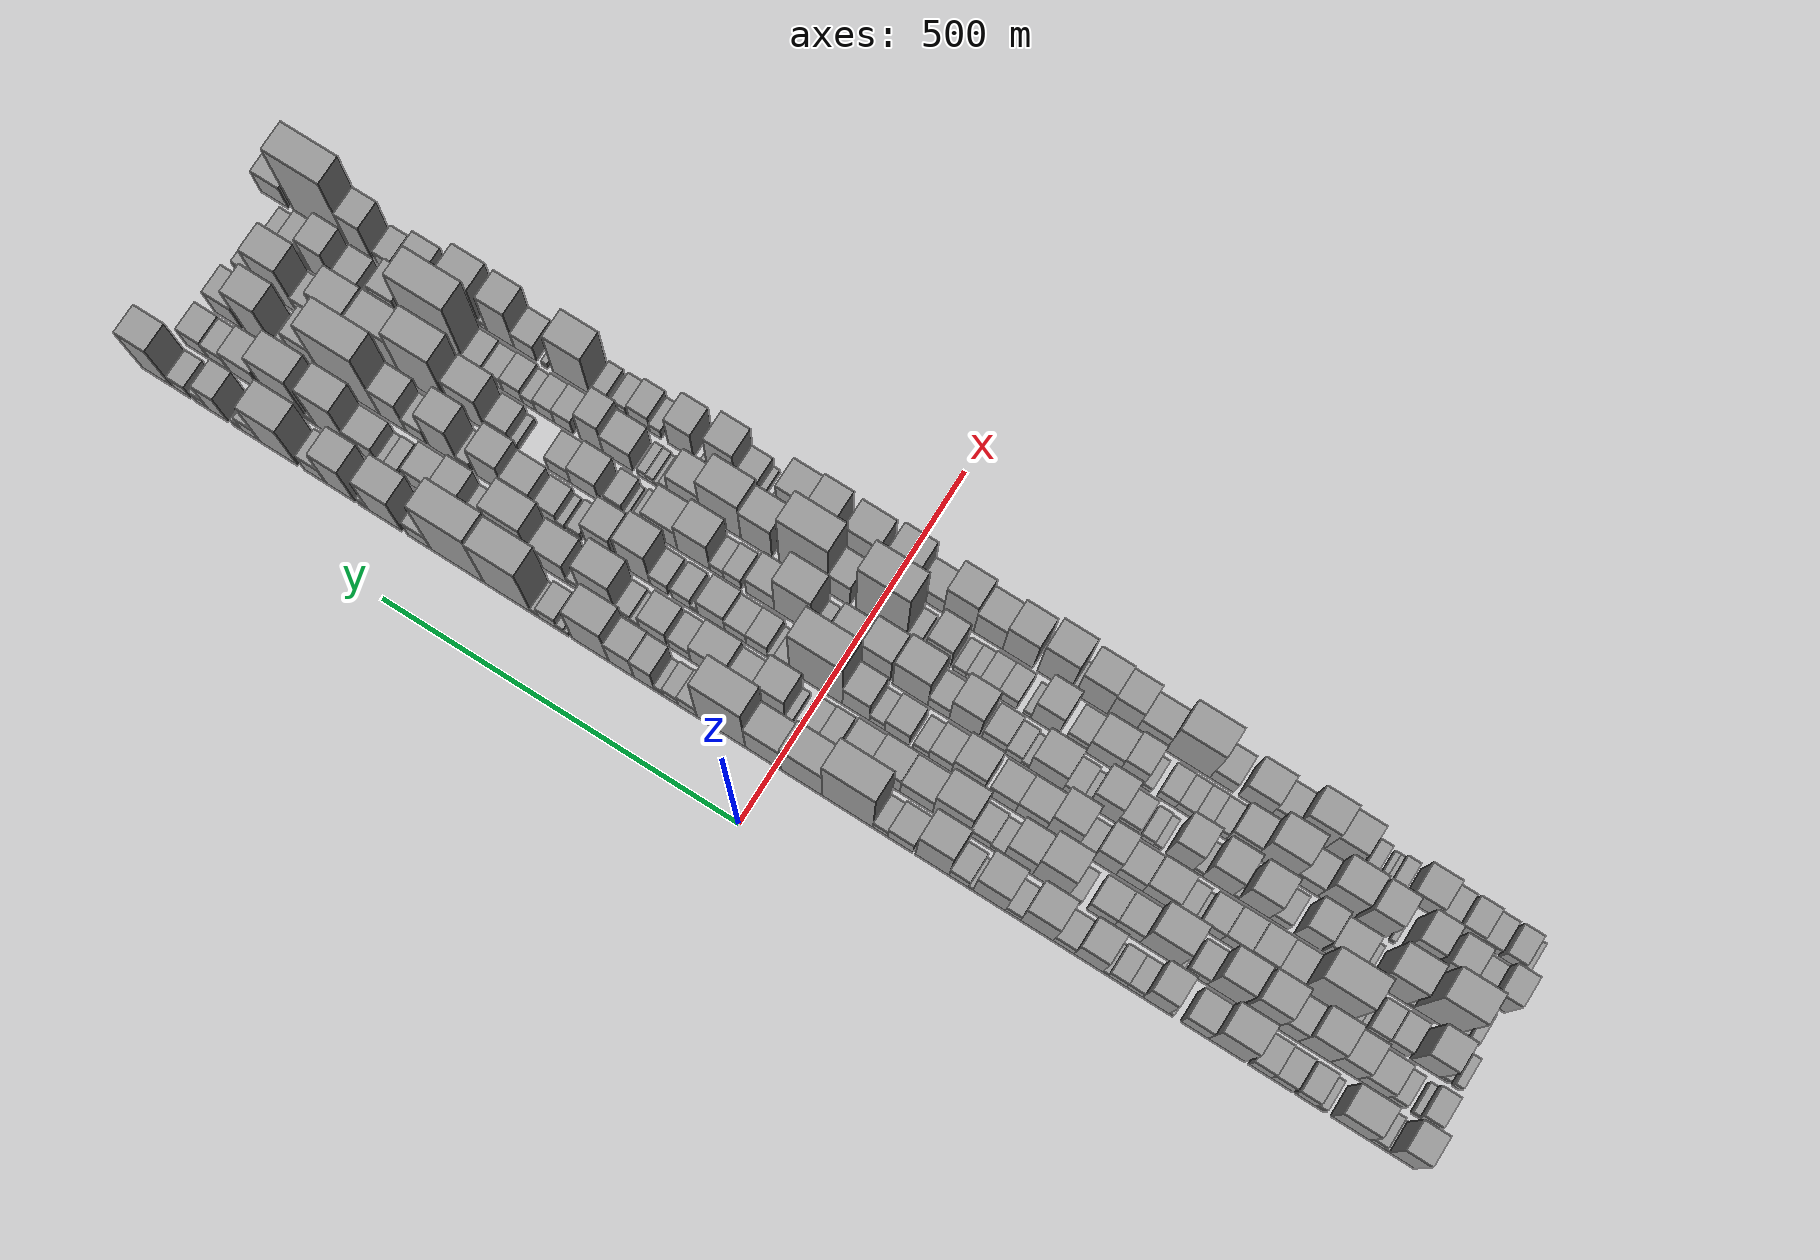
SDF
<sdf version="1.6">
 <world name="default">
  <scene>
   <sky><clouds><speed>12</speed></clouds></sky>
   <ambient>0.4 0.4 0.4 1</ambient>
   <background>0.7 0.7 0.7 1</background>
   <shadows>1</shadows>
  </scene>
  <gravity>0 0 -9.8066</gravity>
  <magnetic_field>6e-06 2.3e-05 -4.2e-05</magnetic_field>
  <physics default="0" name="default_physics" type="ode">
   <ode>
    <solver>
     <type>quick</type>
     <iters>10</iters>
     <sor>1.0</sor>
     <use_dynamic_moi_rescaling>0</use_dynamic_moi_rescaling>
    </solver>
    <constraints>
     <cfm>0</cfm>
     <erp>0.2</erp>
     <contact_max_correcting_vel>100</contact_max_correcting_vel>
     <contact_surface_layer>0.001</contact_surface_layer>
    </constraints>
   </ode>
   <max_step_size>0.004</max_step_size>
   <real_time_factor>1</real_time_factor>
   <real_time_update_rate>250</real_time_update_rate>
  </physics>
  <light name="sun" type="directional">
   <pose>0 0 10 0 0 0</pose>
   <diffuse>0.8 0.8 0.8 1</diffuse>
   <specular>0.2 0.2 0.2 1</specular>
   <attenuation>
    <range>1000</range>
    <constant>0.9</constant>
    <linear>0.01</linear>
    <quadratic>0.001</quadratic>
   </attenuation>
   <direction>-0.5 0.1 -0.9</direction>
  </light>
  <model name="building_1">
   <static>1</static>
   <pose>100.0000 -842.8567 0 0.000000 0.000000 0.000000</pose>
   <link name="link">
    <pose>0 0 54.00 0 0 0</pose>
    <collision name="collision"><geometry><box><size>40.0000 34.2865 108.0000</size></box></geometry></collision>
    <visual name="visual">
     <cast_shadows>0</cast_shadows>
     <geometry><box><size>40.0000 34.2865 108.0000</size></box></geometry>
     <material>
      <script>
       <uri>model://grey_wall/materials/scripts</uri>
       <uri>model://grey_wall/materials/textures</uri>
       <name>vrc/grey_wall</name>
      </script>
     </material>
    </visual>
   </link>
  </model>
  <model name="building_2">
   <static>1</static>
   <pose>100.0000 -822.6795 0 0.000000 0.000000 0.000000</pose>
   <link name="link">
    <pose>0 0 7.50 0 0 0</pose>
    <collision name="collision"><geometry><box><size>40.0000 6.0679 15.0000</size></box></geometry></collision>
    <visual name="visual">
     <cast_shadows>0</cast_shadows>
     <geometry><box><size>40.0000 6.0679 15.0000</size></box></geometry>
     <material>
      <script>
       <uri>model://grey_wall/materials/scripts</uri>
       <uri>model://grey_wall/materials/textures</uri>
       <name>vrc/grey_wall</name>
      </script>
     </material>
    </visual>
   </link>
  </model>
  <model name="building_3">
   <static>1</static>
   <pose>100.0000 -810.2094 0 0.000000 0.000000 0.000000</pose>
   <link name="link">
    <pose>0 0 18.00 0 0 0</pose>
    <collision name="collision"><geometry><box><size>40.0000 18.8723 36.0000</size></box></geometry></collision>
    <visual name="visual">
     <cast_shadows>0</cast_shadows>
     <geometry><box><size>40.0000 18.8723 36.0000</size></box></geometry>
     <material>
      <script>
       <uri>model://grey_wall/materials/scripts</uri>
       <uri>model://grey_wall/materials/textures</uri>
       <name>vrc/grey_wall</name>
      </script>
     </material>
    </visual>
   </link>
  </model>
  <model name="building_4">
   <static>1</static>
   <pose>100.0000 -775.6286 0 0.000000 0.000000 0.000000</pose>
   <link name="link">
    <pose>0 0 45.00 0 0 0</pose>
    <collision name="collision"><geometry><box><size>40.0000 50.2893 90.0000</size></box></geometry></collision>
    <visual name="visual">
     <cast_shadows>0</cast_shadows>
     <geometry><box><size>40.0000 50.2893 90.0000</size></box></geometry>
     <material>
      <script>
       <uri>model://grey_wall/materials/scripts</uri>
       <uri>model://grey_wall/materials/textures</uri>
       <name>vrc/grey_wall</name>
      </script>
     </material>
    </visual>
   </link>
  </model>
  <model name="building_5">
   <static>1</static>
   <pose>100.0000 -736.3963 0 0.000000 0.000000 0.000000</pose>
   <link name="link">
    <pose>0 0 13.50 0 0 0</pose>
    <collision name="collision"><geometry><box><size>40.0000 12.1753 27.0000</size></box></geometry></collision>
    <visual name="visual">
     <cast_shadows>0</cast_shadows>
     <geometry><box><size>40.0000 12.1753 27.0000</size></box></geometry>
     <material>
      <script>
       <uri>model://grey_wall/materials/scripts</uri>
       <uri>model://grey_wall/materials/textures</uri>
       <name>vrc/grey_wall</name>
      </script>
     </material>
    </visual>
   </link>
  </model>
  <model name="building_6">
   <static>1</static>
   <pose>100.0000 -716.5740 0 0.000000 0.000000 0.000000</pose>
   <link name="link">
    <pose>0 0 25.50 0 0 0</pose>
    <collision name="collision"><geometry><box><size>40.0000 27.4694 51.0000</size></box></geometry></collision>
    <visual name="visual">
     <cast_shadows>0</cast_shadows>
     <geometry><box><size>40.0000 27.4694 51.0000</size></box></geometry>
     <material>
      <script>
       <uri>model://grey_wall/materials/scripts</uri>
       <uri>model://grey_wall/materials/textures</uri>
       <name>vrc/grey_wall</name>
      </script>
     </material>
    </visual>
   </link>
  </model>
  <model name="building_7">
   <static>1</static>
   <pose>100.0000 -685.3520 0 0.000000 0.000000 0.000000</pose>
   <link name="link">
    <pose>0 0 25.50 0 0 0</pose>
    <collision name="collision"><geometry><box><size>40.0000 28.9746 51.0000</size></box></geometry></collision>
    <visual name="visual">
     <cast_shadows>0</cast_shadows>
     <geometry><box><size>40.0000 28.9746 51.0000</size></box></geometry>
     <material>
      <script>
       <uri>model://grey_wall/materials/scripts</uri>
       <uri>model://grey_wall/materials/textures</uri>
       <name>vrc/grey_wall</name>
      </script>
     </material>
    </visual>
   </link>
  </model>
  <model name="building_8">
   <static>1</static>
   <pose>100.0000 -656.1818 0 0.000000 0.000000 0.000000</pose>
   <link name="link">
    <pose>0 0 28.50 0 0 0</pose>
    <collision name="collision"><geometry><box><size>40.0000 29.3658 57.0000</size></box></geometry></collision>
    <visual name="visual">
     <cast_shadows>0</cast_shadows>
     <geometry><box><size>40.0000 29.3658 57.0000</size></box></geometry>
     <material>
      <script>
       <uri>model://grey_wall/materials/scripts</uri>
       <uri>model://grey_wall/materials/textures</uri>
       <name>vrc/grey_wall</name>
      </script>
     </material>
    </visual>
   </link>
  </model>
  <model name="building_9">
   <static>1</static>
   <pose>100.0000 -611.9752 0 0.000000 0.000000 0.000000</pose>
   <link name="link">
    <pose>0 0 66.00 0 0 0</pose>
    <collision name="collision"><geometry><box><size>40.0000 49.0474 132.0000</size></box></geometry></collision>
    <visual name="visual">
     <cast_shadows>0</cast_shadows>
     <geometry><box><size>40.0000 49.0474 132.0000</size></box></geometry>
     <material>
      <script>
       <uri>model://grey_wall/materials/scripts</uri>
       <uri>model://grey_wall/materials/textures</uri>
       <name>vrc/grey_wall</name>
      </script>
     </material>
    </visual>
   </link>
  </model>
  <model name="building_10">
   <static>1</static>
   <pose>100.0000 -569.1841 0 0.000000 0.000000 0.000000</pose>
   <link name="link">
    <pose>0 0 36.00 0 0 0</pose>
    <collision name="collision"><geometry><box><size>40.0000 36.5348 72.0000</size></box></geometry></collision>
    <visual name="visual">
     <cast_shadows>0</cast_shadows>
     <geometry><box><size>40.0000 36.5348 72.0000</size></box></geometry>
     <material>
      <script>
       <uri>model://grey_wall/materials/scripts</uri>
       <uri>model://grey_wall/materials/textures</uri>
       <name>vrc/grey_wall</name>
      </script>
     </material>
    </visual>
   </link>
  </model>
  <model name="building_11">
   <static>1</static>
   <pose>100.0000 -537.8415 0 0.000000 0.000000 0.000000</pose>
   <link name="link">
    <pose>0 0 7.50 0 0 0</pose>
    <collision name="collision"><geometry><box><size>40.0000 6.1504 15.0000</size></box></geometry></collision>
    <visual name="visual">
     <cast_shadows>0</cast_shadows>
     <geometry><box><size>40.0000 6.1504 15.0000</size></box></geometry>
     <material>
      <script>
       <uri>model://grey_wall/materials/scripts</uri>
       <uri>model://grey_wall/materials/textures</uri>
       <name>vrc/grey_wall</name>
      </script>
     </material>
    </visual>
   </link>
  </model>
  <model name="building_12">
   <static>1</static>
   <pose>100.0000 -517.1414 0 0.000000 0.000000 0.000000</pose>
   <link name="link">
    <pose>0 0 55.50 0 0 0</pose>
    <collision name="collision"><geometry><box><size>40.0000 35.2499 111.0000</size></box></geometry></collision>
    <visual name="visual">
     <cast_shadows>0</cast_shadows>
     <geometry><box><size>40.0000 35.2499 111.0000</size></box></geometry>
     <material>
      <script>
       <uri>model://grey_wall/materials/scripts</uri>
       <uri>model://grey_wall/materials/textures</uri>
       <name>vrc/grey_wall</name>
      </script>
     </material>
    </visual>
   </link>
  </model>
  <model name="building_13">
   <static>1</static>
   <pose>100.0000 -488.8202 0 0.000000 0.000000 0.000000</pose>
   <link name="link">
    <pose>0 0 21.00 0 0 0</pose>
    <collision name="collision"><geometry><box><size>40.0000 21.3925 42.0000</size></box></geometry></collision>
    <visual name="visual">
     <cast_shadows>0</cast_shadows>
     <geometry><box><size>40.0000 21.3925 42.0000</size></box></geometry>
     <material>
      <script>
       <uri>model://grey_wall/materials/scripts</uri>
       <uri>model://grey_wall/materials/textures</uri>
       <name>vrc/grey_wall</name>
      </script>
     </material>
    </visual>
   </link>
  </model>
  <model name="building_14">
   <static>1</static>
   <pose>100.0000 -465.9381 0 0.000000 0.000000 0.000000</pose>
   <link name="link">
    <pose>0 0 21.00 0 0 0</pose>
    <collision name="collision"><geometry><box><size>40.0000 24.3716 42.0000</size></box></geometry></collision>
    <visual name="visual">
     <cast_shadows>0</cast_shadows>
     <geometry><box><size>40.0000 24.3716 42.0000</size></box></geometry>
     <material>
      <script>
       <uri>model://grey_wall/materials/scripts</uri>
       <uri>model://grey_wall/materials/textures</uri>
       <name>vrc/grey_wall</name>
      </script>
     </material>
    </visual>
   </link>
  </model>
  <model name="building_15">
   <static>1</static>
   <pose>100.0000 -449.8477 0 0.000000 0.000000 0.000000</pose>
   <link name="link">
    <pose>0 0 9.00 0 0 0</pose>
    <collision name="collision"><geometry><box><size>40.0000 7.8091 18.0000</size></box></geometry></collision>
    <visual name="visual">
     <cast_shadows>0</cast_shadows>
     <geometry><box><size>40.0000 7.8091 18.0000</size></box></geometry>
     <material>
      <script>
       <uri>model://grey_wall/materials/scripts</uri>
       <uri>model://grey_wall/materials/textures</uri>
       <name>vrc/grey_wall</name>
      </script>
     </material>
    </visual>
   </link>
  </model>
  <model name="building_16">
   <static>1</static>
   <pose>100.0000 -426.8884 0 0.000000 0.000000 0.000000</pose>
   <link name="link">
    <pose>0 0 51.00 0 0 0</pose>
    <collision name="collision"><geometry><box><size>40.0000 38.1096 102.0000</size></box></geometry></collision>
    <visual name="visual">
     <cast_shadows>0</cast_shadows>
     <geometry><box><size>40.0000 38.1096 102.0000</size></box></geometry>
     <material>
      <script>
       <uri>model://grey_wall/materials/scripts</uri>
       <uri>model://grey_wall/materials/textures</uri>
       <name>vrc/grey_wall</name>
      </script>
     </material>
    </visual>
   </link>
  </model>
  <model name="building_17">
   <static>1</static>
   <pose>100.0000 -393.7586 0 0.000000 0.000000 0.000000</pose>
   <link name="link">
    <pose>0 0 24.00 0 0 0</pose>
    <collision name="collision"><geometry><box><size>40.0000 28.1500 48.0000</size></box></geometry></collision>
    <visual name="visual">
     <cast_shadows>0</cast_shadows>
     <geometry><box><size>40.0000 28.1500 48.0000</size></box></geometry>
     <material>
      <script>
       <uri>model://grey_wall/materials/scripts</uri>
       <uri>model://grey_wall/materials/textures</uri>
       <name>vrc/grey_wall</name>
      </script>
     </material>
    </visual>
   </link>
  </model>
  <model name="building_18">
   <static>1</static>
   <pose>100.0000 -357.6440 0 0.000000 0.000000 0.000000</pose>
   <link name="link">
    <pose>0 0 61.50 0 0 0</pose>
    <collision name="collision"><geometry><box><size>40.0000 44.0793 123.0000</size></box></geometry></collision>
    <visual name="visual">
     <cast_shadows>0</cast_shadows>
     <geometry><box><size>40.0000 44.0793 123.0000</size></box></geometry>
     <material>
      <script>
       <uri>model://grey_wall/materials/scripts</uri>
       <uri>model://grey_wall/materials/textures</uri>
       <name>vrc/grey_wall</name>
      </script>
     </material>
    </visual>
   </link>
  </model>
  <model name="building_19">
   <static>1</static>
   <pose>100.0000 -325.1831 0 0.000000 0.000000 0.000000</pose>
   <link name="link">
    <pose>0 0 18.00 0 0 0</pose>
    <collision name="collision"><geometry><box><size>40.0000 20.8425 36.0000</size></box></geometry></collision>
    <visual name="visual">
     <cast_shadows>0</cast_shadows>
     <geometry><box><size>40.0000 20.8425 36.0000</size></box></geometry>
     <material>
      <script>
       <uri>model://grey_wall/materials/scripts</uri>
       <uri>model://grey_wall/materials/textures</uri>
       <name>vrc/grey_wall</name>
      </script>
     </material>
    </visual>
   </link>
  </model>
  <model name="building_20">
   <static>1</static>
   <pose>100.0000 -292.7769 0 0.000000 0.000000 0.000000</pose>
   <link name="link">
    <pose>0 0 58.50 0 0 0</pose>
    <collision name="collision"><geometry><box><size>40.0000 43.9699 117.0000</size></box></geometry></collision>
    <visual name="visual">
     <cast_shadows>0</cast_shadows>
     <geometry><box><size>40.0000 43.9699 117.0000</size></box></geometry>
     <material>
      <script>
       <uri>model://grey_wall/materials/scripts</uri>
       <uri>model://grey_wall/materials/textures</uri>
       <name>vrc/grey_wall</name>
      </script>
     </material>
    </visual>
   </link>
  </model>
  <model name="building_21">
   <static>1</static>
   <pose>100.0000 -267.7532 0 0.000000 0.000000 0.000000</pose>
   <link name="link">
    <pose>0 0 7.50 0 0 0</pose>
    <collision name="collision"><geometry><box><size>40.0000 6.0774 15.0000</size></box></geometry></collision>
    <visual name="visual">
     <cast_shadows>0</cast_shadows>
     <geometry><box><size>40.0000 6.0774 15.0000</size></box></geometry>
     <material>
      <script>
       <uri>model://grey_wall/materials/scripts</uri>
       <uri>model://grey_wall/materials/textures</uri>
       <name>vrc/grey_wall</name>
      </script>
     </material>
    </visual>
   </link>
  </model>
  <model name="building_22">
   <static>1</static>
   <pose>100.0000 -251.3077 0 0.000000 0.000000 0.000000</pose>
   <link name="link">
    <pose>0 0 25.50 0 0 0</pose>
    <collision name="collision"><geometry><box><size>40.0000 26.8137 51.0000</size></box></geometry></collision>
    <visual name="visual">
     <cast_shadows>0</cast_shadows>
     <geometry><box><size>40.0000 26.8137 51.0000</size></box></geometry>
     <material>
      <script>
       <uri>model://grey_wall/materials/scripts</uri>
       <uri>model://grey_wall/materials/textures</uri>
       <name>vrc/grey_wall</name>
      </script>
     </material>
    </visual>
   </link>
  </model>
  <model name="building_23">
   <static>1</static>
   <pose>100.0000 -214.9314 0 0.000000 0.000000 0.000000</pose>
   <link name="link">
    <pose>0 0 75.00 0 0 0</pose>
    <collision name="collision"><geometry><box><size>40.0000 45.9389 150.0000</size></box></geometry></collision>
    <visual name="visual">
     <cast_shadows>0</cast_shadows>
     <geometry><box><size>40.0000 45.9389 150.0000</size></box></geometry>
     <material>
      <script>
       <uri>model://grey_wall/materials/scripts</uri>
       <uri>model://grey_wall/materials/textures</uri>
       <name>vrc/grey_wall</name>
      </script>
     </material>
    </visual>
   </link>
  </model>
  <model name="building_24">
   <static>1</static>
   <pose>100.0000 -171.4697 0 0.000000 0.000000 0.000000</pose>
   <link name="link">
    <pose>0 0 31.50 0 0 0</pose>
    <collision name="collision"><geometry><box><size>40.0000 34.9845 63.0000</size></box></geometry></collision>
    <visual name="visual">
     <cast_shadows>0</cast_shadows>
     <geometry><box><size>40.0000 34.9845 63.0000</size></box></geometry>
     <material>
      <script>
       <uri>model://grey_wall/materials/scripts</uri>
       <uri>model://grey_wall/materials/textures</uri>
       <name>vrc/grey_wall</name>
      </script>
     </material>
    </visual>
   </link>
  </model>
  <model name="building_25">
   <static>1</static>
   <pose>100.0000 -143.8720 0 0.000000 0.000000 0.000000</pose>
   <link name="link">
    <pose>0 0 19.50 0 0 0</pose>
    <collision name="collision"><geometry><box><size>40.0000 20.2109 39.0000</size></box></geometry></collision>
    <visual name="visual">
     <cast_shadows>0</cast_shadows>
     <geometry><box><size>40.0000 20.2109 39.0000</size></box></geometry>
     <material>
      <script>
       <uri>model://grey_wall/materials/scripts</uri>
       <uri>model://grey_wall/materials/textures</uri>
       <name>vrc/grey_wall</name>
      </script>
     </material>
    </visual>
   </link>
  </model>
  <model name="building_26">
   <static>1</static>
   <pose>100.0000 -98.5625 0 0.000000 0.000000 0.000000</pose>
   <link name="link">
    <pose>0 0 108.00 0 0 0</pose>
    <collision name="collision"><geometry><box><size>40.0000 70.4080 216.0000</size></box></geometry></collision>
    <visual name="visual">
     <cast_shadows>0</cast_shadows>
     <geometry><box><size>40.0000 70.4080 216.0000</size></box></geometry>
     <material>
      <script>
       <uri>model://grey_wall/materials/scripts</uri>
       <uri>model://grey_wall/materials/textures</uri>
       <name>vrc/grey_wall</name>
      </script>
     </material>
    </visual>
   </link>
  </model>
  <model name="building_27">
   <static>1</static>
   <pose>100.0000 -34.9724 0 0.000000 0.000000 0.000000</pose>
   <link name="link">
    <pose>0 0 73.50 0 0 0</pose>
    <collision name="collision"><geometry><box><size>40.0000 56.7723 147.0000</size></box></geometry></collision>
    <visual name="visual">
     <cast_shadows>0</cast_shadows>
     <geometry><box><size>40.0000 56.7723 147.0000</size></box></geometry>
     <material>
      <script>
       <uri>model://grey_wall/materials/scripts</uri>
       <uri>model://grey_wall/materials/textures</uri>
       <name>vrc/grey_wall</name>
      </script>
     </material>
    </visual>
   </link>
  </model>
  <model name="building_28">
   <static>1</static>
   <pose>100.0000 17.8575 0 0.000000 0.000000 0.000000</pose>
   <link name="link">
    <pose>0 0 61.50 0 0 0</pose>
    <collision name="collision"><geometry><box><size>40.0000 48.8873 123.0000</size></box></geometry></collision>
    <visual name="visual">
     <cast_shadows>0</cast_shadows>
     <geometry><box><size>40.0000 48.8873 123.0000</size></box></geometry>
     <material>
      <script>
       <uri>model://grey_wall/materials/scripts</uri>
       <uri>model://grey_wall/materials/textures</uri>
       <name>vrc/grey_wall</name>
      </script>
     </material>
    </visual>
   </link>
  </model>
  <model name="building_29">
   <static>1</static>
   <pose>100.0000 76.1347 0 0.000000 0.000000 0.000000</pose>
   <link name="link">
    <pose>0 0 106.50 0 0 0</pose>
    <collision name="collision"><geometry><box><size>40.0000 67.6671 213.0000</size></box></geometry></collision>
    <visual name="visual">
     <cast_shadows>0</cast_shadows>
     <geometry><box><size>40.0000 67.6671 213.0000</size></box></geometry>
     <material>
      <script>
       <uri>model://grey_wall/materials/scripts</uri>
       <uri>model://grey_wall/materials/textures</uri>
       <name>vrc/grey_wall</name>
      </script>
     </material>
    </visual>
   </link>
  </model>
  <model name="building_30">
   <static>1</static>
   <pose>100.0000 122.9821 0 0.000000 0.000000 0.000000</pose>
   <link name="link">
    <pose>0 0 25.50 0 0 0</pose>
    <collision name="collision"><geometry><box><size>40.0000 26.0276 51.0000</size></box></geometry></collision>
    <visual name="visual">
     <cast_shadows>0</cast_shadows>
     <geometry><box><size>40.0000 26.0276 51.0000</size></box></geometry>
     <material>
      <script>
       <uri>model://grey_wall/materials/scripts</uri>
       <uri>model://grey_wall/materials/textures</uri>
       <name>vrc/grey_wall</name>
      </script>
     </material>
    </visual>
   </link>
  </model>
  <model name="building_31">
   <static>1</static>
   <pose>100.0000 146.6750 0 0.000000 0.000000 0.000000</pose>
   <link name="link">
    <pose>0 0 19.50 0 0 0</pose>
    <collision name="collision"><geometry><box><size>40.0000 21.3582 39.0000</size></box></geometry></collision>
    <visual name="visual">
     <cast_shadows>0</cast_shadows>
     <geometry><box><size>40.0000 21.3582 39.0000</size></box></geometry>
     <material>
      <script>
       <uri>model://grey_wall/materials/scripts</uri>
       <uri>model://grey_wall/materials/textures</uri>
       <name>vrc/grey_wall</name>
      </script>
     </material>
    </visual>
   </link>
  </model>
  <model name="building_32">
   <static>1</static>
   <pose>100.0000 163.1563 0 0.000000 0.000000 0.000000</pose>
   <link name="link">
    <pose>0 0 13.50 0 0 0</pose>
    <collision name="collision"><geometry><box><size>40.0000 11.6044 27.0000</size></box></geometry></collision>
    <visual name="visual">
     <cast_shadows>0</cast_shadows>
     <geometry><box><size>40.0000 11.6044 27.0000</size></box></geometry>
     <material>
      <script>
       <uri>model://grey_wall/materials/scripts</uri>
       <uri>model://grey_wall/materials/textures</uri>
       <name>vrc/grey_wall</name>
      </script>
     </material>
    </visual>
   </link>
  </model>
  <model name="building_33">
   <static>1</static>
   <pose>100.0000 183.3700 0 0.000000 0.000000 0.000000</pose>
   <link name="link">
    <pose>0 0 48.00 0 0 0</pose>
    <collision name="collision"><geometry><box><size>40.0000 28.8230 96.0000</size></box></geometry></collision>
    <visual name="visual">
     <cast_shadows>0</cast_shadows>
     <geometry><box><size>40.0000 28.8230 96.0000</size></box></geometry>
     <material>
      <script>
       <uri>model://grey_wall/materials/scripts</uri>
       <uri>model://grey_wall/materials/textures</uri>
       <name>vrc/grey_wall</name>
      </script>
     </material>
    </visual>
   </link>
  </model>
  <model name="building_34">
   <static>1</static>
   <pose>100.0000 215.3747 0 0.000000 0.000000 0.000000</pose>
   <link name="link">
    <pose>0 0 51.00 0 0 0</pose>
    <collision name="collision"><geometry><box><size>40.0000 35.1864 102.0000</size></box></geometry></collision>
    <visual name="visual">
     <cast_shadows>0</cast_shadows>
     <geometry><box><size>40.0000 35.1864 102.0000</size></box></geometry>
     <material>
      <script>
       <uri>model://grey_wall/materials/scripts</uri>
       <uri>model://grey_wall/materials/textures</uri>
       <name>vrc/grey_wall</name>
      </script>
     </material>
    </visual>
   </link>
  </model>
  <model name="building_35">
   <static>1</static>
   <pose>100.0000 258.9601 0 0.000000 0.000000 0.000000</pose>
   <link name="link">
    <pose>0 0 75.00 0 0 0</pose>
    <collision name="collision"><geometry><box><size>40.0000 51.9845 150.0000</size></box></geometry></collision>
    <visual name="visual">
     <cast_shadows>0</cast_shadows>
     <geometry><box><size>40.0000 51.9845 150.0000</size></box></geometry>
     <material>
      <script>
       <uri>model://grey_wall/materials/scripts</uri>
       <uri>model://grey_wall/materials/textures</uri>
       <name>vrc/grey_wall</name>
      </script>
     </material>
    </visual>
   </link>
  </model>
  <model name="building_36">
   <static>1</static>
   <pose>100.0000 292.0350 0 0.000000 0.000000 0.000000</pose>
   <link name="link">
    <pose>0 0 7.50 0 0 0</pose>
    <collision name="collision"><geometry><box><size>40.0000 6.1653 15.0000</size></box></geometry></collision>
    <visual name="visual">
     <cast_shadows>0</cast_shadows>
     <geometry><box><size>40.0000 6.1653 15.0000</size></box></geometry>
     <material>
      <script>
       <uri>model://grey_wall/materials/scripts</uri>
       <uri>model://grey_wall/materials/textures</uri>
       <name>vrc/grey_wall</name>
      </script>
     </material>
    </visual>
   </link>
  </model>
  <model name="building_37">
   <static>1</static>
   <pose>100.0000 300.3955 0 0.000000 0.000000 0.000000</pose>
   <link name="link">
    <pose>0 0 12.00 0 0 0</pose>
    <collision name="collision"><geometry><box><size>40.0000 10.5556 24.0000</size></box></geometry></collision>
    <visual name="visual">
     <cast_shadows>0</cast_shadows>
     <geometry><box><size>40.0000 10.5556 24.0000</size></box></geometry>
     <material>
      <script>
       <uri>model://grey_wall/materials/scripts</uri>
       <uri>model://grey_wall/materials/textures</uri>
       <name>vrc/grey_wall</name>
      </script>
     </material>
    </visual>
   </link>
  </model>
  <model name="building_38">
   <static>1</static>
   <pose>100.0000 318.9849 0 0.000000 0.000000 0.000000</pose>
   <link name="link">
    <pose>0 0 24.00 0 0 0</pose>
    <collision name="collision"><geometry><box><size>40.0000 26.6233 48.0000</size></box></geometry></collision>
    <visual name="visual">
     <cast_shadows>0</cast_shadows>
     <geometry><box><size>40.0000 26.6233 48.0000</size></box></geometry>
     <material>
      <script>
       <uri>model://grey_wall/materials/scripts</uri>
       <uri>model://grey_wall/materials/textures</uri>
       <name>vrc/grey_wall</name>
      </script>
     </material>
    </visual>
   </link>
  </model>
  <model name="building_39">
   <static>1</static>
   <pose>100.0000 337.2926 0 0.000000 0.000000 0.000000</pose>
   <link name="link">
    <pose>0 0 10.50 0 0 0</pose>
    <collision name="collision"><geometry><box><size>40.0000 9.9919 21.0000</size></box></geometry></collision>
    <visual name="visual">
     <cast_shadows>0</cast_shadows>
     <geometry><box><size>40.0000 9.9919 21.0000</size></box></geometry>
     <material>
      <script>
       <uri>model://grey_wall/materials/scripts</uri>
       <uri>model://grey_wall/materials/textures</uri>
       <name>vrc/grey_wall</name>
      </script>
     </material>
    </visual>
   </link>
  </model>
  <model name="building_40">
   <static>1</static>
   <pose>100.0000 375.6678 0 0.000000 0.000000 0.000000</pose>
   <link name="link">
    <pose>0 0 99.00 0 0 0</pose>
    <collision name="collision"><geometry><box><size>40.0000 66.7586 198.0000</size></box></geometry></collision>
    <visual name="visual">
     <cast_shadows>0</cast_shadows>
     <geometry><box><size>40.0000 66.7586 198.0000</size></box></geometry>
     <material>
      <script>
       <uri>model://grey_wall/materials/scripts</uri>
       <uri>model://grey_wall/materials/textures</uri>
       <name>vrc/grey_wall</name>
      </script>
     </material>
    </visual>
   </link>
  </model>
  <model name="building_41">
   <static>1</static>
   <pose>100.0000 446.9654 0 0.000000 0.000000 0.000000</pose>
   <link name="link">
    <pose>0 0 106.50 0 0 0</pose>
    <collision name="collision"><geometry><box><size>40.0000 75.8365 213.0000</size></box></geometry></collision>
    <visual name="visual">
     <cast_shadows>0</cast_shadows>
     <geometry><box><size>40.0000 75.8365 213.0000</size></box></geometry>
     <material>
      <script>
       <uri>model://grey_wall/materials/scripts</uri>
       <uri>model://grey_wall/materials/textures</uri>
       <name>vrc/grey_wall</name>
      </script>
     </material>
    </visual>
   </link>
  </model>
  <model name="building_42">
   <static>1</static>
   <pose>100.0000 501.5508 0 0.000000 0.000000 0.000000</pose>
   <link name="link">
    <pose>0 0 30.00 0 0 0</pose>
    <collision name="collision"><geometry><box><size>40.0000 33.3344 60.0000</size></box></geometry></collision>
    <visual name="visual">
     <cast_shadows>0</cast_shadows>
     <geometry><box><size>40.0000 33.3344 60.0000</size></box></geometry>
     <material>
      <script>
       <uri>model://grey_wall/materials/scripts</uri>
       <uri>model://grey_wall/materials/textures</uri>
       <name>vrc/grey_wall</name>
      </script>
     </material>
    </visual>
   </link>
  </model>
  <model name="building_43">
   <static>1</static>
   <pose>100.0000 550.8239 0 0.000000 0.000000 0.000000</pose>
   <link name="link">
    <pose>0 0 66.00 0 0 0</pose>
    <collision name="collision"><geometry><box><size>40.0000 49.2117 132.0000</size></box></geometry></collision>
    <visual name="visual">
     <cast_shadows>0</cast_shadows>
     <geometry><box><size>40.0000 49.2117 132.0000</size></box></geometry>
     <material>
      <script>
       <uri>model://grey_wall/materials/scripts</uri>
       <uri>model://grey_wall/materials/textures</uri>
       <name>vrc/grey_wall</name>
      </script>
     </material>
    </visual>
   </link>
  </model>
  <model name="building_44">
   <static>1</static>
   <pose>100.0000 582.0222 0 0.000000 0.000000 0.000000</pose>
   <link name="link">
    <pose>0 0 13.50 0 0 0</pose>
    <collision name="collision"><geometry><box><size>40.0000 13.1849 27.0000</size></box></geometry></collision>
    <visual name="visual">
     <cast_shadows>0</cast_shadows>
     <geometry><box><size>40.0000 13.1849 27.0000</size></box></geometry>
     <material>
      <script>
       <uri>model://grey_wall/materials/scripts</uri>
       <uri>model://grey_wall/materials/textures</uri>
       <name>vrc/grey_wall</name>
      </script>
     </material>
    </visual>
   </link>
  </model>
  <model name="building_45">
   <static>1</static>
   <pose>100.0000 614.3200 0 0.000000 0.000000 0.000000</pose>
   <link name="link">
    <pose>0 0 67.50 0 0 0</pose>
    <collision name="collision"><geometry><box><size>40.0000 41.4108 135.0000</size></box></geometry></collision>
    <visual name="visual">
     <cast_shadows>0</cast_shadows>
     <geometry><box><size>40.0000 41.4108 135.0000</size></box></geometry>
     <material>
      <script>
       <uri>model://grey_wall/materials/scripts</uri>
       <uri>model://grey_wall/materials/textures</uri>
       <name>vrc/grey_wall</name>
      </script>
     </material>
    </visual>
   </link>
  </model>
  <model name="building_46">
   <static>1</static>
   <pose>100.0000 651.0902 0 0.000000 0.000000 0.000000</pose>
   <link name="link">
    <pose>0 0 31.50 0 0 0</pose>
    <collision name="collision"><geometry><box><size>40.0000 32.1295 63.0000</size></box></geometry></collision>
    <visual name="visual">
     <cast_shadows>0</cast_shadows>
     <geometry><box><size>40.0000 32.1295 63.0000</size></box></geometry>
     <material>
      <script>
       <uri>model://grey_wall/materials/scripts</uri>
       <uri>model://grey_wall/materials/textures</uri>
       <name>vrc/grey_wall</name>
      </script>
     </material>
    </visual>
   </link>
  </model>
  <model name="building_47">
   <static>1</static>
   <pose>100.0000 703.5954 0 0.000000 0.000000 0.000000</pose>
   <link name="link">
    <pose>0 0 75.00 0 0 0</pose>
    <collision name="collision"><geometry><box><size>40.0000 54.8809 150.0000</size></box></geometry></collision>
    <visual name="visual">
     <cast_shadows>0</cast_shadows>
     <geometry><box><size>40.0000 54.8809 150.0000</size></box></geometry>
     <material>
      <script>
       <uri>model://grey_wall/materials/scripts</uri>
       <uri>model://grey_wall/materials/textures</uri>
       <name>vrc/grey_wall</name>
      </script>
     </material>
    </visual>
   </link>
  </model>
  <model name="building_48">
   <static>1</static>
   <pose>100.0000 744.6136 0 0.000000 0.000000 0.000000</pose>
   <link name="link">
    <pose>0 0 27.00 0 0 0</pose>
    <collision name="collision"><geometry><box><size>40.0000 27.1555 54.0000</size></box></geometry></collision>
    <visual name="visual">
     <cast_shadows>0</cast_shadows>
     <geometry><box><size>40.0000 27.1555 54.0000</size></box></geometry>
     <material>
      <script>
       <uri>model://grey_wall/materials/scripts</uri>
       <uri>model://grey_wall/materials/textures</uri>
       <name>vrc/grey_wall</name>
      </script>
     </material>
    </visual>
   </link>
  </model>
  <model name="building_49">
   <static>1</static>
   <pose>100.0000 764.0607 0 0.000000 0.000000 0.000000</pose>
   <link name="link">
    <pose>0 0 12.00 0 0 0</pose>
    <collision name="collision"><geometry><box><size>40.0000 11.7385 24.0000</size></box></geometry></collision>
    <visual name="visual">
     <cast_shadows>0</cast_shadows>
     <geometry><box><size>40.0000 11.7385 24.0000</size></box></geometry>
     <material>
      <script>
       <uri>model://grey_wall/materials/scripts</uri>
       <uri>model://grey_wall/materials/textures</uri>
       <name>vrc/grey_wall</name>
      </script>
     </material>
    </visual>
   </link>
  </model>
  <model name="building_50">
   <static>1</static>
   <pose>100.0000 792.1015 0 0.000000 0.000000 0.000000</pose>
   <link name="link">
    <pose>0 0 48.00 0 0 0</pose>
    <collision name="collision"><geometry><box><size>40.0000 30.3432 96.0000</size></box></geometry></collision>
    <visual name="visual">
     <cast_shadows>0</cast_shadows>
     <geometry><box><size>40.0000 30.3432 96.0000</size></box></geometry>
     <material>
      <script>
       <uri>model://grey_wall/materials/scripts</uri>
       <uri>model://grey_wall/materials/textures</uri>
       <name>vrc/grey_wall</name>
      </script>
     </material>
    </visual>
   </link>
  </model>
  <model name="building_51">
   <static>1</static>
   <pose>100.0000 816.9492 0 0.000000 0.000000 0.000000</pose>
   <link name="link">
    <pose>0 0 18.00 0 0 0</pose>
    <collision name="collision"><geometry><box><size>40.0000 19.3522 36.0000</size></box></geometry></collision>
    <visual name="visual">
     <cast_shadows>0</cast_shadows>
     <geometry><box><size>40.0000 19.3522 36.0000</size></box></geometry>
     <material>
      <script>
       <uri>model://grey_wall/materials/scripts</uri>
       <uri>model://grey_wall/materials/textures</uri>
       <name>vrc/grey_wall</name>
      </script>
     </material>
    </visual>
   </link>
  </model>
  <model name="building_52">
   <static>1</static>
   <pose>100.0000 844.1916 0 0.000000 0.000000 0.000000</pose>
   <link name="link">
    <pose>0 0 22.50 0 0 0</pose>
    <collision name="collision"><geometry><box><size>40.0000 25.1327 45.0000</size></box></geometry></collision>
    <visual name="visual">
     <cast_shadows>0</cast_shadows>
     <geometry><box><size>40.0000 25.1327 45.0000</size></box></geometry>
     <material>
      <script>
       <uri>model://grey_wall/materials/scripts</uri>
       <uri>model://grey_wall/materials/textures</uri>
       <name>vrc/grey_wall</name>
      </script>
     </material>
    </visual>
   </link>
  </model>
  <model name="building_53">
   <static>1</static>
   <pose>100.0000 881.5079 0 0.000000 0.000000 0.000000</pose>
   <link name="link">
    <pose>0 0 70.50 0 0 0</pose>
    <collision name="collision"><geometry><box><size>40.0000 43.4998 141.0000</size></box></geometry></collision>
    <visual name="visual">
     <cast_shadows>0</cast_shadows>
     <geometry><box><size>40.0000 43.4998 141.0000</size></box></geometry>
     <material>
      <script>
       <uri>model://grey_wall/materials/scripts</uri>
       <uri>model://grey_wall/materials/textures</uri>
       <name>vrc/grey_wall</name>
      </script>
     </material>
    </visual>
   </link>
  </model>
  <model name="building_54">
   <static>1</static>
   <pose>152.0000 -847.2493 0 0.000000 0.000000 0.000000</pose>
   <link name="link">
    <pose>0 0 22.50 0 0 0</pose>
    <collision name="collision"><geometry><box><size>40.0000 25.5014 45.0000</size></box></geometry></collision>
    <visual name="visual">
     <cast_shadows>0</cast_shadows>
     <geometry><box><size>40.0000 25.5014 45.0000</size></box></geometry>
     <material>
      <script>
       <uri>model://grey_wall/materials/scripts</uri>
       <uri>model://grey_wall/materials/textures</uri>
       <name>vrc/grey_wall</name>
      </script>
     </material>
    </visual>
   </link>
  </model>
  <model name="building_55">
   <static>1</static>
   <pose>152.0000 -829.9720 0 0.000000 0.000000 0.000000</pose>
   <link name="link">
    <pose>0 0 10.50 0 0 0</pose>
    <collision name="collision"><geometry><box><size>40.0000 9.0531 21.0000</size></box></geometry></collision>
    <visual name="visual">
     <cast_shadows>0</cast_shadows>
     <geometry><box><size>40.0000 9.0531 21.0000</size></box></geometry>
     <material>
      <script>
       <uri>model://grey_wall/materials/scripts</uri>
       <uri>model://grey_wall/materials/textures</uri>
       <name>vrc/grey_wall</name>
      </script>
     </material>
    </visual>
   </link>
  </model>
  <model name="building_56">
   <static>1</static>
   <pose>152.0000 -804.8071 0 0.000000 0.000000 0.000000</pose>
   <link name="link">
    <pose>0 0 18.00 0 0 0</pose>
    <collision name="collision"><geometry><box><size>40.0000 21.2767 36.0000</size></box></geometry></collision>
    <visual name="visual">
     <cast_shadows>0</cast_shadows>
     <geometry><box><size>40.0000 21.2767 36.0000</size></box></geometry>
     <material>
      <script>
       <uri>model://grey_wall/materials/scripts</uri>
       <uri>model://grey_wall/materials/textures</uri>
       <name>vrc/grey_wall</name>
      </script>
     </material>
    </visual>
   </link>
  </model>
  <model name="building_57">
   <static>1</static>
   <pose>152.0000 -774.6374 0 0.000000 0.000000 0.000000</pose>
   <link name="link">
    <pose>0 0 33.00 0 0 0</pose>
    <collision name="collision"><geometry><box><size>40.0000 39.0627 66.0000</size></box></geometry></collision>
    <visual name="visual">
     <cast_shadows>0</cast_shadows>
     <geometry><box><size>40.0000 39.0627 66.0000</size></box></geometry>
     <material>
      <script>
       <uri>model://grey_wall/materials/scripts</uri>
       <uri>model://grey_wall/materials/textures</uri>
       <name>vrc/grey_wall</name>
      </script>
     </material>
    </visual>
   </link>
  </model>
  <model name="building_58">
   <static>1</static>
   <pose>152.0000 -736.8742 0 0.000000 0.000000 0.000000</pose>
   <link name="link">
    <pose>0 0 49.50 0 0 0</pose>
    <collision name="collision"><geometry><box><size>40.0000 36.4637 99.0000</size></box></geometry></collision>
    <visual name="visual">
     <cast_shadows>0</cast_shadows>
     <geometry><box><size>40.0000 36.4637 99.0000</size></box></geometry>
     <material>
      <script>
       <uri>model://grey_wall/materials/scripts</uri>
       <uri>model://grey_wall/materials/textures</uri>
       <name>vrc/grey_wall</name>
      </script>
     </material>
    </visual>
   </link>
  </model>
  <model name="building_59">
   <static>1</static>
   <pose>152.0000 -697.1276 0 0.000000 0.000000 0.000000</pose>
   <link name="link">
    <pose>0 0 61.50 0 0 0</pose>
    <collision name="collision"><geometry><box><size>40.0000 43.0296 123.0000</size></box></geometry></collision>
    <visual name="visual">
     <cast_shadows>0</cast_shadows>
     <geometry><box><size>40.0000 43.0296 123.0000</size></box></geometry>
     <material>
      <script>
       <uri>model://grey_wall/materials/scripts</uri>
       <uri>model://grey_wall/materials/textures</uri>
       <name>vrc/grey_wall</name>
      </script>
     </material>
    </visual>
   </link>
  </model>
  <model name="building_60">
   <static>1</static>
   <pose>152.0000 -660.8821 0 0.000000 0.000000 0.000000</pose>
   <link name="link">
    <pose>0 0 46.50 0 0 0</pose>
    <collision name="collision"><geometry><box><size>40.0000 29.4615 93.0000</size></box></geometry></collision>
    <visual name="visual">
     <cast_shadows>0</cast_shadows>
     <geometry><box><size>40.0000 29.4615 93.0000</size></box></geometry>
     <material>
      <script>
       <uri>model://grey_wall/materials/scripts</uri>
       <uri>model://grey_wall/materials/textures</uri>
       <name>vrc/grey_wall</name>
      </script>
     </material>
    </visual>
   </link>
  </model>
  <model name="building_61">
   <static>1</static>
   <pose>152.0000 -624.5359 0 0.000000 0.000000 0.000000</pose>
   <link name="link">
    <pose>0 0 70.50 0 0 0</pose>
    <collision name="collision"><geometry><box><size>40.0000 43.2308 141.0000</size></box></geometry></collision>
    <visual name="visual">
     <cast_shadows>0</cast_shadows>
     <geometry><box><size>40.0000 43.2308 141.0000</size></box></geometry>
     <material>
      <script>
       <uri>model://grey_wall/materials/scripts</uri>
       <uri>model://grey_wall/materials/textures</uri>
       <name>vrc/grey_wall</name>
      </script>
     </material>
    </visual>
   </link>
  </model>
  <model name="building_62">
   <static>1</static>
   <pose>152.0000 -576.8171 0 0.000000 0.000000 0.000000</pose>
   <link name="link">
    <pose>0 0 69.00 0 0 0</pose>
    <collision name="collision"><geometry><box><size>40.0000 44.2067 138.0000</size></box></geometry></collision>
    <visual name="visual">
     <cast_shadows>0</cast_shadows>
     <geometry><box><size>40.0000 44.2067 138.0000</size></box></geometry>
     <material>
      <script>
       <uri>model://grey_wall/materials/scripts</uri>
       <uri>model://grey_wall/materials/textures</uri>
       <name>vrc/grey_wall</name>
      </script>
     </material>
    </visual>
   </link>
  </model>
  <model name="building_63">
   <static>1</static>
   <pose>152.0000 -540.6397 0 0.000000 0.000000 0.000000</pose>
   <link name="link">
    <pose>0 0 24.00 0 0 0</pose>
    <collision name="collision"><geometry><box><size>40.0000 28.1481 48.0000</size></box></geometry></collision>
    <visual name="visual">
     <cast_shadows>0</cast_shadows>
     <geometry><box><size>40.0000 28.1481 48.0000</size></box></geometry>
     <material>
      <script>
       <uri>model://grey_wall/materials/scripts</uri>
       <uri>model://grey_wall/materials/textures</uri>
       <name>vrc/grey_wall</name>
      </script>
     </material>
    </visual>
   </link>
  </model>
  <model name="building_64">
   <static>1</static>
   <pose>152.0000 -520.0817 0 0.000000 0.000000 0.000000</pose>
   <link name="link">
    <pose>0 0 7.50 0 0 0</pose>
    <collision name="collision"><geometry><box><size>40.0000 6.9678 15.0000</size></box></geometry></collision>
    <visual name="visual">
     <cast_shadows>0</cast_shadows>
     <geometry><box><size>40.0000 6.9678 15.0000</size></box></geometry>
     <material>
      <script>
       <uri>model://grey_wall/materials/scripts</uri>
       <uri>model://grey_wall/materials/textures</uri>
       <name>vrc/grey_wall</name>
      </script>
     </material>
    </visual>
   </link>
  </model>
  <model name="building_65">
   <static>1</static>
   <pose>152.0000 -490.6315 0 0.000000 0.000000 0.000000</pose>
   <link name="link">
    <pose>0 0 72.00 0 0 0</pose>
    <collision name="collision"><geometry><box><size>40.0000 51.9326 144.0000</size></box></geometry></collision>
    <visual name="visual">
     <cast_shadows>0</cast_shadows>
     <geometry><box><size>40.0000 51.9326 144.0000</size></box></geometry>
     <material>
      <script>
       <uri>model://grey_wall/materials/scripts</uri>
       <uri>model://grey_wall/materials/textures</uri>
       <name>vrc/grey_wall</name>
      </script>
     </material>
    </visual>
   </link>
  </model>
  <model name="building_66">
   <static>1</static>
   <pose>152.0000 -447.1830 0 0.000000 0.000000 0.000000</pose>
   <link name="link">
    <pose>0 0 33.00 0 0 0</pose>
    <collision name="collision"><geometry><box><size>40.0000 34.9644 66.0000</size></box></geometry></collision>
    <visual name="visual">
     <cast_shadows>0</cast_shadows>
     <geometry><box><size>40.0000 34.9644 66.0000</size></box></geometry>
     <material>
      <script>
       <uri>model://grey_wall/materials/scripts</uri>
       <uri>model://grey_wall/materials/textures</uri>
       <name>vrc/grey_wall</name>
      </script>
     </material>
    </visual>
   </link>
  </model>
  <model name="building_67">
   <static>1</static>
   <pose>152.0000 -411.3741 0 0.000000 0.000000 0.000000</pose>
   <link name="link">
    <pose>0 0 31.50 0 0 0</pose>
    <collision name="collision"><geometry><box><size>40.0000 36.6535 63.0000</size></box></geometry></collision>
    <visual name="visual">
     <cast_shadows>0</cast_shadows>
     <geometry><box><size>40.0000 36.6535 63.0000</size></box></geometry>
     <material>
      <script>
       <uri>model://grey_wall/materials/scripts</uri>
       <uri>model://grey_wall/materials/textures</uri>
       <name>vrc/grey_wall</name>
      </script>
     </material>
    </visual>
   </link>
  </model>
  <model name="building_68">
   <static>1</static>
   <pose>152.0000 -375.5326 0 0.000000 0.000000 0.000000</pose>
   <link name="link">
    <pose>0 0 16.50 0 0 0</pose>
    <collision name="collision"><geometry><box><size>40.0000 17.0295 33.0000</size></box></geometry></collision>
    <visual name="visual">
     <cast_shadows>0</cast_shadows>
     <geometry><box><size>40.0000 17.0295 33.0000</size></box></geometry>
     <material>
      <script>
       <uri>model://grey_wall/materials/scripts</uri>
       <uri>model://grey_wall/materials/textures</uri>
       <name>vrc/grey_wall</name>
      </script>
     </material>
    </visual>
   </link>
  </model>
  <model name="building_69">
   <static>1</static>
   <pose>152.0000 -343.1738 0 0.000000 0.000000 0.000000</pose>
   <link name="link">
    <pose>0 0 73.50 0 0 0</pose>
    <collision name="collision"><geometry><box><size>40.0000 47.6880 147.0000</size></box></geometry></collision>
    <visual name="visual">
     <cast_shadows>0</cast_shadows>
     <geometry><box><size>40.0000 47.6880 147.0000</size></box></geometry>
     <material>
      <script>
       <uri>model://grey_wall/materials/scripts</uri>
       <uri>model://grey_wall/materials/textures</uri>
       <name>vrc/grey_wall</name>
      </script>
     </material>
    </visual>
   </link>
  </model>
  <model name="building_70">
   <static>1</static>
   <pose>152.0000 -299.5063 0 0.000000 0.000000 0.000000</pose>
   <link name="link">
    <pose>0 0 51.00 0 0 0</pose>
    <collision name="collision"><geometry><box><size>40.0000 39.6471 102.0000</size></box></geometry></collision>
    <visual name="visual">
     <cast_shadows>0</cast_shadows>
     <geometry><box><size>40.0000 39.6471 102.0000</size></box></geometry>
     <material>
      <script>
       <uri>model://grey_wall/materials/scripts</uri>
       <uri>model://grey_wall/materials/textures</uri>
       <name>vrc/grey_wall</name>
      </script>
     </material>
    </visual>
   </link>
  </model>
  <model name="building_71">
   <static>1</static>
   <pose>152.0000 -270.5392 0 0.000000 0.000000 0.000000</pose>
   <link name="link">
    <pose>0 0 16.50 0 0 0</pose>
    <collision name="collision"><geometry><box><size>40.0000 18.2869 33.0000</size></box></geometry></collision>
    <visual name="visual">
     <cast_shadows>0</cast_shadows>
     <geometry><box><size>40.0000 18.2869 33.0000</size></box></geometry>
     <material>
      <script>
       <uri>model://grey_wall/materials/scripts</uri>
       <uri>model://grey_wall/materials/textures</uri>
       <name>vrc/grey_wall</name>
      </script>
     </material>
    </visual>
   </link>
  </model>
  <model name="building_72">
   <static>1</static>
   <pose>152.0000 -247.4045 0 0.000000 0.000000 0.000000</pose>
   <link name="link">
    <pose>0 0 24.00 0 0 0</pose>
    <collision name="collision"><geometry><box><size>40.0000 27.9825 48.0000</size></box></geometry></collision>
    <visual name="visual">
     <cast_shadows>0</cast_shadows>
     <geometry><box><size>40.0000 27.9825 48.0000</size></box></geometry>
     <material>
      <script>
       <uri>model://grey_wall/materials/scripts</uri>
       <uri>model://grey_wall/materials/textures</uri>
       <name>vrc/grey_wall</name>
      </script>
     </material>
    </visual>
   </link>
  </model>
  <model name="building_73">
   <static>1</static>
   <pose>152.0000 -208.2137 0 0.000000 0.000000 0.000000</pose>
   <link name="link">
    <pose>0 0 63.00 0 0 0</pose>
    <collision name="collision"><geometry><box><size>40.0000 50.3991 126.0000</size></box></geometry></collision>
    <visual name="visual">
     <cast_shadows>0</cast_shadows>
     <geometry><box><size>40.0000 50.3991 126.0000</size></box></geometry>
     <material>
      <script>
       <uri>model://grey_wall/materials/scripts</uri>
       <uri>model://grey_wall/materials/textures</uri>
       <name>vrc/grey_wall</name>
      </script>
     </material>
    </visual>
   </link>
  </model>
  <model name="building_74">
   <static>1</static>
   <pose>152.0000 -160.5492 0 0.000000 0.000000 0.000000</pose>
   <link name="link">
    <pose>0 0 37.50 0 0 0</pose>
    <collision name="collision"><geometry><box><size>40.0000 44.9298 75.0000</size></box></geometry></collision>
    <visual name="visual">
     <cast_shadows>0</cast_shadows>
     <geometry><box><size>40.0000 44.9298 75.0000</size></box></geometry>
     <material>
      <script>
       <uri>model://grey_wall/materials/scripts</uri>
       <uri>model://grey_wall/materials/textures</uri>
       <name>vrc/grey_wall</name>
      </script>
     </material>
    </visual>
   </link>
  </model>
  <model name="building_75">
   <static>1</static>
   <pose>152.0000 -116.7100 0 0.000000 0.000000 0.000000</pose>
   <link name="link">
    <pose>0 0 40.50 0 0 0</pose>
    <collision name="collision"><geometry><box><size>40.0000 42.7485 81.0000</size></box></geometry></collision>
    <visual name="visual">
     <cast_shadows>0</cast_shadows>
     <geometry><box><size>40.0000 42.7485 81.0000</size></box></geometry>
     <material>
      <script>
       <uri>model://grey_wall/materials/scripts</uri>
       <uri>model://grey_wall/materials/textures</uri>
       <name>vrc/grey_wall</name>
      </script>
     </material>
    </visual>
   </link>
  </model>
  <model name="building_76">
   <static>1</static>
   <pose>152.0000 -75.9170 0 0.000000 0.000000 0.000000</pose>
   <link name="link">
    <pose>0 0 33.00 0 0 0</pose>
    <collision name="collision"><geometry><box><size>40.0000 38.8376 66.0000</size></box></geometry></collision>
    <visual name="visual">
     <cast_shadows>0</cast_shadows>
     <geometry><box><size>40.0000 38.8376 66.0000</size></box></geometry>
     <material>
      <script>
       <uri>model://grey_wall/materials/scripts</uri>
       <uri>model://grey_wall/materials/textures</uri>
       <name>vrc/grey_wall</name>
      </script>
     </material>
    </visual>
   </link>
  </model>
  <model name="building_77">
   <static>1</static>
   <pose>152.0000 -39.4412 0 0.000000 0.000000 0.000000</pose>
   <link name="link">
    <pose>0 0 25.50 0 0 0</pose>
    <collision name="collision"><geometry><box><size>40.0000 26.1140 51.0000</size></box></geometry></collision>
    <visual name="visual">
     <cast_shadows>0</cast_shadows>
     <geometry><box><size>40.0000 26.1140 51.0000</size></box></geometry>
     <material>
      <script>
       <uri>model://grey_wall/materials/scripts</uri>
       <uri>model://grey_wall/materials/textures</uri>
       <name>vrc/grey_wall</name>
      </script>
     </material>
    </visual>
   </link>
  </model>
  <model name="building_78">
   <static>1</static>
   <pose>152.0000 -13.2603 0 0.000000 0.000000 0.000000</pose>
   <link name="link">
    <pose>0 0 22.50 0 0 0</pose>
    <collision name="collision"><geometry><box><size>40.0000 26.2477 45.0000</size></box></geometry></collision>
    <visual name="visual">
     <cast_shadows>0</cast_shadows>
     <geometry><box><size>40.0000 26.2477 45.0000</size></box></geometry>
     <material>
      <script>
       <uri>model://grey_wall/materials/scripts</uri>
       <uri>model://grey_wall/materials/textures</uri>
       <name>vrc/grey_wall</name>
      </script>
     </material>
    </visual>
   </link>
  </model>
  <model name="building_79">
   <static>1</static>
   <pose>152.0000 15.2685 0 0.000000 0.000000 0.000000</pose>
   <link name="link">
    <pose>0 0 13.50 0 0 0</pose>
    <collision name="collision"><geometry><box><size>40.0000 10.8099 27.0000</size></box></geometry></collision>
    <visual name="visual">
     <cast_shadows>0</cast_shadows>
     <geometry><box><size>40.0000 10.8099 27.0000</size></box></geometry>
     <material>
      <script>
       <uri>model://grey_wall/materials/scripts</uri>
       <uri>model://grey_wall/materials/textures</uri>
       <name>vrc/grey_wall</name>
      </script>
     </material>
    </visual>
   </link>
  </model>
  <model name="building_80">
   <static>1</static>
   <pose>152.0000 42.1543 0 0.000000 0.000000 0.000000</pose>
   <link name="link">
    <pose>0 0 57.00 0 0 0</pose>
    <collision name="collision"><geometry><box><size>40.0000 42.9615 114.0000</size></box></geometry></collision>
    <visual name="visual">
     <cast_shadows>0</cast_shadows>
     <geometry><box><size>40.0000 42.9615 114.0000</size></box></geometry>
     <material>
      <script>
       <uri>model://grey_wall/materials/scripts</uri>
       <uri>model://grey_wall/materials/textures</uri>
       <name>vrc/grey_wall</name>
      </script>
     </material>
    </visual>
   </link>
  </model>
  <model name="building_81">
   <static>1</static>
   <pose>152.0000 86.3625 0 0.000000 0.000000 0.000000</pose>
   <link name="link">
    <pose>0 0 27.00 0 0 0</pose>
    <collision name="collision"><geometry><box><size>40.0000 31.4549 54.0000</size></box></geometry></collision>
    <visual name="visual">
     <cast_shadows>0</cast_shadows>
     <geometry><box><size>40.0000 31.4549 54.0000</size></box></geometry>
     <material>
      <script>
       <uri>model://grey_wall/materials/scripts</uri>
       <uri>model://grey_wall/materials/textures</uri>
       <name>vrc/grey_wall</name>
      </script>
     </material>
    </visual>
   </link>
  </model>
  <model name="building_82">
   <static>1</static>
   <pose>152.0000 127.1451 0 0.000000 0.000000 0.000000</pose>
   <link name="link">
    <pose>0 0 42.00 0 0 0</pose>
    <collision name="collision"><geometry><box><size>40.0000 50.1102 84.0000</size></box></geometry></collision>
    <visual name="visual">
     <cast_shadows>0</cast_shadows>
     <geometry><box><size>40.0000 50.1102 84.0000</size></box></geometry>
     <material>
      <script>
       <uri>model://grey_wall/materials/scripts</uri>
       <uri>model://grey_wall/materials/textures</uri>
       <name>vrc/grey_wall</name>
      </script>
     </material>
    </visual>
   </link>
  </model>
  <model name="building_83">
   <static>1</static>
   <pose>152.0000 167.3471 0 0.000000 0.000000 0.000000</pose>
   <link name="link">
    <pose>0 0 25.50 0 0 0</pose>
    <collision name="collision"><geometry><box><size>40.0000 30.2939 51.0000</size></box></geometry></collision>
    <visual name="visual">
     <cast_shadows>0</cast_shadows>
     <geometry><box><size>40.0000 30.2939 51.0000</size></box></geometry>
     <material>
      <script>
       <uri>model://grey_wall/materials/scripts</uri>
       <uri>model://grey_wall/materials/textures</uri>
       <name>vrc/grey_wall</name>
      </script>
     </material>
    </visual>
   </link>
  </model>
  <model name="building_84">
   <static>1</static>
   <pose>152.0000 204.5459 0 0.000000 0.000000 0.000000</pose>
   <link name="link">
    <pose>0 0 33.00 0 0 0</pose>
    <collision name="collision"><geometry><box><size>40.0000 38.1037 66.0000</size></box></geometry></collision>
    <visual name="visual">
     <cast_shadows>0</cast_shadows>
     <geometry><box><size>40.0000 38.1037 66.0000</size></box></geometry>
     <material>
      <script>
       <uri>model://grey_wall/materials/scripts</uri>
       <uri>model://grey_wall/materials/textures</uri>
       <name>vrc/grey_wall</name>
      </script>
     </material>
    </visual>
   </link>
  </model>
  <model name="building_85">
   <static>1</static>
   <pose>152.0000 229.5717 0 0.000000 0.000000 0.000000</pose>
   <link name="link">
    <pose>0 0 13.50 0 0 0</pose>
    <collision name="collision"><geometry><box><size>40.0000 11.9478 27.0000</size></box></geometry></collision>
    <visual name="visual">
     <cast_shadows>0</cast_shadows>
     <geometry><box><size>40.0000 11.9478 27.0000</size></box></geometry>
     <material>
      <script>
       <uri>model://grey_wall/materials/scripts</uri>
       <uri>model://grey_wall/materials/textures</uri>
       <name>vrc/grey_wall</name>
      </script>
     </material>
    </visual>
   </link>
  </model>
  <model name="building_86">
   <static>1</static>
   <pose>152.0000 246.4050 0 0.000000 0.000000 0.000000</pose>
   <link name="link">
    <pose>0 0 19.50 0 0 0</pose>
    <collision name="collision"><geometry><box><size>40.0000 21.7189 39.0000</size></box></geometry></collision>
    <visual name="visual">
     <cast_shadows>0</cast_shadows>
     <geometry><box><size>40.0000 21.7189 39.0000</size></box></geometry>
     <material>
      <script>
       <uri>model://grey_wall/materials/scripts</uri>
       <uri>model://grey_wall/materials/textures</uri>
       <name>vrc/grey_wall</name>
      </script>
     </material>
    </visual>
   </link>
  </model>
  <model name="building_87">
   <static>1</static>
   <pose>152.0000 282.4956 0 0.000000 0.000000 0.000000</pose>
   <link name="link">
    <pose>0 0 69.00 0 0 0</pose>
    <collision name="collision"><geometry><box><size>40.0000 50.4623 138.0000</size></box></geometry></collision>
    <visual name="visual">
     <cast_shadows>0</cast_shadows>
     <geometry><box><size>40.0000 50.4623 138.0000</size></box></geometry>
     <material>
      <script>
       <uri>model://grey_wall/materials/scripts</uri>
       <uri>model://grey_wall/materials/textures</uri>
       <name>vrc/grey_wall</name>
      </script>
     </material>
    </visual>
   </link>
  </model>
  <model name="building_88">
   <static>1</static>
   <pose>152.0000 316.6638 0 0.000000 0.000000 0.000000</pose>
   <link name="link">
    <pose>0 0 15.00 0 0 0</pose>
    <collision name="collision"><geometry><box><size>40.0000 17.8741 30.0000</size></box></geometry></collision>
    <visual name="visual">
     <cast_shadows>0</cast_shadows>
     <geometry><box><size>40.0000 17.8741 30.0000</size></box></geometry>
     <material>
      <script>
       <uri>model://grey_wall/materials/scripts</uri>
       <uri>model://grey_wall/materials/textures</uri>
       <name>vrc/grey_wall</name>
      </script>
     </material>
    </visual>
   </link>
  </model>
  <model name="building_89">
   <static>1</static>
   <pose>152.0000 349.0598 0 0.000000 0.000000 0.000000</pose>
   <link name="link">
    <pose>0 0 45.00 0 0 0</pose>
    <collision name="collision"><geometry><box><size>40.0000 46.9179 90.0000</size></box></geometry></collision>
    <visual name="visual">
     <cast_shadows>0</cast_shadows>
     <geometry><box><size>40.0000 46.9179 90.0000</size></box></geometry>
     <material>
      <script>
       <uri>model://grey_wall/materials/scripts</uri>
       <uri>model://grey_wall/materials/textures</uri>
       <name>vrc/grey_wall</name>
      </script>
     </material>
    </visual>
   </link>
  </model>
  <model name="building_90">
   <static>1</static>
   <pose>152.0000 405.3010 0 0.000000 0.000000 0.000000</pose>
   <link name="link">
    <pose>0 0 75.00 0 0 0</pose>
    <collision name="collision"><geometry><box><size>40.0000 55.5645 150.0000</size></box></geometry></collision>
    <visual name="visual">
     <cast_shadows>0</cast_shadows>
     <geometry><box><size>40.0000 55.5645 150.0000</size></box></geometry>
     <material>
      <script>
       <uri>model://grey_wall/materials/scripts</uri>
       <uri>model://grey_wall/materials/textures</uri>
       <name>vrc/grey_wall</name>
      </script>
     </material>
    </visual>
   </link>
  </model>
  <model name="building_91">
   <static>1</static>
   <pose>152.0000 441.0005 0 0.000000 0.000000 0.000000</pose>
   <link name="link">
    <pose>0 0 15.00 0 0 0</pose>
    <collision name="collision"><geometry><box><size>40.0000 15.8345 30.0000</size></box></geometry></collision>
    <visual name="visual">
     <cast_shadows>0</cast_shadows>
     <geometry><box><size>40.0000 15.8345 30.0000</size></box></geometry>
     <material>
      <script>
       <uri>model://grey_wall/materials/scripts</uri>
       <uri>model://grey_wall/materials/textures</uri>
       <name>vrc/grey_wall</name>
      </script>
     </material>
    </visual>
   </link>
  </model>
  <model name="building_92">
   <static>1</static>
   <pose>152.0000 462.5650 0 0.000000 0.000000 0.000000</pose>
   <link name="link">
    <pose>0 0 18.00 0 0 0</pose>
    <collision name="collision"><geometry><box><size>40.0000 19.2944 36.0000</size></box></geometry></collision>
    <visual name="visual">
     <cast_shadows>0</cast_shadows>
     <geometry><box><size>40.0000 19.2944 36.0000</size></box></geometry>
     <material>
      <script>
       <uri>model://grey_wall/materials/scripts</uri>
       <uri>model://grey_wall/materials/textures</uri>
       <name>vrc/grey_wall</name>
      </script>
     </material>
    </visual>
   </link>
  </model>
  <model name="building_93">
   <static>1</static>
   <pose>152.0000 490.9199 0 0.000000 0.000000 0.000000</pose>
   <link name="link">
    <pose>0 0 48.00 0 0 0</pose>
    <collision name="collision"><geometry><box><size>40.0000 37.4153 96.0000</size></box></geometry></collision>
    <visual name="visual">
     <cast_shadows>0</cast_shadows>
     <geometry><box><size>40.0000 37.4153 96.0000</size></box></geometry>
     <material>
      <script>
       <uri>model://grey_wall/materials/scripts</uri>
       <uri>model://grey_wall/materials/textures</uri>
       <name>vrc/grey_wall</name>
      </script>
     </material>
    </visual>
   </link>
  </model>
  <model name="building_94">
   <static>1</static>
   <pose>152.0000 530.9502 0 0.000000 0.000000 0.000000</pose>
   <link name="link">
    <pose>0 0 36.00 0 0 0</pose>
    <collision name="collision"><geometry><box><size>40.0000 42.6453 72.0000</size></box></geometry></collision>
    <visual name="visual">
     <cast_shadows>0</cast_shadows>
     <geometry><box><size>40.0000 42.6453 72.0000</size></box></geometry>
     <material>
      <script>
       <uri>model://grey_wall/materials/scripts</uri>
       <uri>model://grey_wall/materials/textures</uri>
       <name>vrc/grey_wall</name>
      </script>
     </material>
    </visual>
   </link>
  </model>
  <model name="building_95">
   <static>1</static>
   <pose>152.0000 557.1563 0 0.000000 0.000000 0.000000</pose>
   <link name="link">
    <pose>0 0 10.50 0 0 0</pose>
    <collision name="collision"><geometry><box><size>40.0000 9.7668 21.0000</size></box></geometry></collision>
    <visual name="visual">
     <cast_shadows>0</cast_shadows>
     <geometry><box><size>40.0000 9.7668 21.0000</size></box></geometry>
     <material>
      <script>
       <uri>model://grey_wall/materials/scripts</uri>
       <uri>model://grey_wall/materials/textures</uri>
       <name>vrc/grey_wall</name>
      </script>
     </material>
    </visual>
   </link>
  </model>
  <model name="building_96">
   <static>1</static>
   <pose>152.0000 574.5912 0 0.000000 0.000000 0.000000</pose>
   <link name="link">
    <pose>0 0 16.50 0 0 0</pose>
    <collision name="collision"><geometry><box><size>40.0000 19.1031 33.0000</size></box></geometry></collision>
    <visual name="visual">
     <cast_shadows>0</cast_shadows>
     <geometry><box><size>40.0000 19.1031 33.0000</size></box></geometry>
     <material>
      <script>
       <uri>model://grey_wall/materials/scripts</uri>
       <uri>model://grey_wall/materials/textures</uri>
       <name>vrc/grey_wall</name>
      </script>
     </material>
    </visual>
   </link>
  </model>
  <model name="building_97">
   <static>1</static>
   <pose>152.0000 589.9394 0 0.000000 0.000000 0.000000</pose>
   <link name="link">
    <pose>0 0 13.50 0 0 0</pose>
    <collision name="collision"><geometry><box><size>40.0000 11.5933 27.0000</size></box></geometry></collision>
    <visual name="visual">
     <cast_shadows>0</cast_shadows>
     <geometry><box><size>40.0000 11.5933 27.0000</size></box></geometry>
     <material>
      <script>
       <uri>model://grey_wall/materials/scripts</uri>
       <uri>model://grey_wall/materials/textures</uri>
       <name>vrc/grey_wall</name>
      </script>
     </material>
    </visual>
   </link>
  </model>
  <model name="building_98">
   <static>1</static>
   <pose>152.0000 616.2266 0 0.000000 0.000000 0.000000</pose>
   <link name="link">
    <pose>0 0 34.50 0 0 0</pose>
    <collision name="collision"><geometry><box><size>40.0000 40.9809 69.0000</size></box></geometry></collision>
    <visual name="visual">
     <cast_shadows>0</cast_shadows>
     <geometry><box><size>40.0000 40.9809 69.0000</size></box></geometry>
     <material>
      <script>
       <uri>model://grey_wall/materials/scripts</uri>
       <uri>model://grey_wall/materials/textures</uri>
       <name>vrc/grey_wall</name>
      </script>
     </material>
    </visual>
   </link>
  </model>
  <model name="building_99">
   <static>1</static>
   <pose>152.0000 661.1758 0 0.000000 0.000000 0.000000</pose>
   <link name="link">
    <pose>0 0 76.50 0 0 0</pose>
    <collision name="collision"><geometry><box><size>40.0000 48.9176 153.0000</size></box></geometry></collision>
    <visual name="visual">
     <cast_shadows>0</cast_shadows>
     <geometry><box><size>40.0000 48.9176 153.0000</size></box></geometry>
     <material>
      <script>
       <uri>model://grey_wall/materials/scripts</uri>
       <uri>model://grey_wall/materials/textures</uri>
       <name>vrc/grey_wall</name>
      </script>
     </material>
    </visual>
   </link>
  </model>
  <model name="building_100">
   <static>1</static>
   <pose>152.0000 691.3845 0 0.000000 0.000000 0.000000</pose>
   <link name="link">
    <pose>0 0 13.50 0 0 0</pose>
    <collision name="collision"><geometry><box><size>40.0000 11.4999 27.0000</size></box></geometry></collision>
    <visual name="visual">
     <cast_shadows>0</cast_shadows>
     <geometry><box><size>40.0000 11.4999 27.0000</size></box></geometry>
     <material>
      <script>
       <uri>model://grey_wall/materials/scripts</uri>
       <uri>model://grey_wall/materials/textures</uri>
       <name>vrc/grey_wall</name>
      </script>
     </material>
    </visual>
   </link>
  </model>
  <model name="building_101">
   <static>1</static>
   <pose>152.0000 725.6495 0 0.000000 0.000000 0.000000</pose>
   <link name="link">
    <pose>0 0 79.50 0 0 0</pose>
    <collision name="collision"><geometry><box><size>40.0000 57.0301 159.0000</size></box></geometry></collision>
    <visual name="visual">
     <cast_shadows>0</cast_shadows>
     <geometry><box><size>40.0000 57.0301 159.0000</size></box></geometry>
     <material>
      <script>
       <uri>model://grey_wall/materials/scripts</uri>
       <uri>model://grey_wall/materials/textures</uri>
       <name>vrc/grey_wall</name>
      </script>
     </material>
    </visual>
   </link>
  </model>
  <model name="building_102">
   <static>1</static>
   <pose>152.0000 786.7947 0 0.000000 0.000000 0.000000</pose>
   <link name="link">
    <pose>0 0 40.50 0 0 0</pose>
    <collision name="collision"><geometry><box><size>40.0000 47.2603 81.0000</size></box></geometry></collision>
    <visual name="visual">
     <cast_shadows>0</cast_shadows>
     <geometry><box><size>40.0000 47.2603 81.0000</size></box></geometry>
     <material>
      <script>
       <uri>model://grey_wall/materials/scripts</uri>
       <uri>model://grey_wall/materials/textures</uri>
       <name>vrc/grey_wall</name>
      </script>
     </material>
    </visual>
   </link>
  </model>
  <model name="building_103">
   <static>1</static>
   <pose>152.0000 825.8160 0 0.000000 0.000000 0.000000</pose>
   <link name="link">
    <pose>0 0 28.50 0 0 0</pose>
    <collision name="collision"><geometry><box><size>40.0000 30.7824 57.0000</size></box></geometry></collision>
    <visual name="visual">
     <cast_shadows>0</cast_shadows>
     <geometry><box><size>40.0000 30.7824 57.0000</size></box></geometry>
     <material>
      <script>
       <uri>model://grey_wall/materials/scripts</uri>
       <uri>model://grey_wall/materials/textures</uri>
       <name>vrc/grey_wall</name>
      </script>
     </material>
    </visual>
   </link>
  </model>
  <model name="building_104">
   <static>1</static>
   <pose>152.0000 857.9769 0 0.000000 0.000000 0.000000</pose>
   <link name="link">
    <pose>0 0 31.50 0 0 0</pose>
    <collision name="collision"><geometry><box><size>40.0000 33.5394 63.0000</size></box></geometry></collision>
    <visual name="visual">
     <cast_shadows>0</cast_shadows>
     <geometry><box><size>40.0000 33.5394 63.0000</size></box></geometry>
     <material>
      <script>
       <uri>model://grey_wall/materials/scripts</uri>
       <uri>model://grey_wall/materials/textures</uri>
       <name>vrc/grey_wall</name>
      </script>
     </material>
    </visual>
   </link>
  </model>
  <model name="building_105">
   <static>1</static>
   <pose>204.0000 -854.5983 0 0.000000 0.000000 0.000000</pose>
   <link name="link">
    <pose>0 0 13.50 0 0 0</pose>
    <collision name="collision"><geometry><box><size>40.0000 10.8033 27.0000</size></box></geometry></collision>
    <visual name="visual">
     <cast_shadows>0</cast_shadows>
     <geometry><box><size>40.0000 10.8033 27.0000</size></box></geometry>
     <material>
      <script>
       <uri>model://grey_wall/materials/scripts</uri>
       <uri>model://grey_wall/materials/textures</uri>
       <name>vrc/grey_wall</name>
      </script>
     </material>
    </visual>
   </link>
  </model>
  <model name="building_106">
   <static>1</static>
   <pose>204.0000 -839.3676 0 0.000000 0.000000 0.000000</pose>
   <link name="link">
    <pose>0 0 12.00 0 0 0</pose>
    <collision name="collision"><geometry><box><size>40.0000 11.6581 24.0000</size></box></geometry></collision>
    <visual name="visual">
     <cast_shadows>0</cast_shadows>
     <geometry><box><size>40.0000 11.6581 24.0000</size></box></geometry>
     <material>
      <script>
       <uri>model://grey_wall/materials/scripts</uri>
       <uri>model://grey_wall/materials/textures</uri>
       <name>vrc/grey_wall</name>
      </script>
     </material>
    </visual>
   </link>
  </model>
  <model name="building_107">
   <static>1</static>
   <pose>204.0000 -814.0601 0 0.000000 0.000000 0.000000</pose>
   <link name="link">
    <pose>0 0 57.00 0 0 0</pose>
    <collision name="collision"><geometry><box><size>40.0000 38.9570 114.0000</size></box></geometry></collision>
    <visual name="visual">
     <cast_shadows>0</cast_shadows>
     <geometry><box><size>40.0000 38.9570 114.0000</size></box></geometry>
     <material>
      <script>
       <uri>model://grey_wall/materials/scripts</uri>
       <uri>model://grey_wall/materials/textures</uri>
       <name>vrc/grey_wall</name>
      </script>
     </material>
    </visual>
   </link>
  </model>
  <model name="building_108">
   <static>1</static>
   <pose>204.0000 -774.3793 0 0.000000 0.000000 0.000000</pose>
   <link name="link">
    <pose>0 0 27.00 0 0 0</pose>
    <collision name="collision"><geometry><box><size>40.0000 28.4046 54.0000</size></box></geometry></collision>
    <visual name="visual">
     <cast_shadows>0</cast_shadows>
     <geometry><box><size>40.0000 28.4046 54.0000</size></box></geometry>
     <material>
      <script>
       <uri>model://grey_wall/materials/scripts</uri>
       <uri>model://grey_wall/materials/textures</uri>
       <name>vrc/grey_wall</name>
      </script>
     </material>
    </visual>
   </link>
  </model>
  <model name="building_109">
   <static>1</static>
   <pose>204.0000 -746.3377 0 0.000000 0.000000 0.000000</pose>
   <link name="link">
    <pose>0 0 24.00 0 0 0</pose>
    <collision name="collision"><geometry><box><size>40.0000 27.6785 48.0000</size></box></geometry></collision>
    <visual name="visual">
     <cast_shadows>0</cast_shadows>
     <geometry><box><size>40.0000 27.6785 48.0000</size></box></geometry>
     <material>
      <script>
       <uri>model://grey_wall/materials/scripts</uri>
       <uri>model://grey_wall/materials/textures</uri>
       <name>vrc/grey_wall</name>
      </script>
     </material>
    </visual>
   </link>
  </model>
  <model name="building_110">
   <static>1</static>
   <pose>204.0000 -728.8970 0 0.000000 0.000000 0.000000</pose>
   <link name="link">
    <pose>0 0 9.00 0 0 0</pose>
    <collision name="collision"><geometry><box><size>40.0000 7.2028 18.0000</size></box></geometry></collision>
    <visual name="visual">
     <cast_shadows>0</cast_shadows>
     <geometry><box><size>40.0000 7.2028 18.0000</size></box></geometry>
     <material>
      <script>
       <uri>model://grey_wall/materials/scripts</uri>
       <uri>model://grey_wall/materials/textures</uri>
       <name>vrc/grey_wall</name>
      </script>
     </material>
    </visual>
   </link>
  </model>
  <model name="building_111">
   <static>1</static>
   <pose>204.0000 -720.8449 0 0.000000 0.000000 0.000000</pose>
   <link name="link">
    <pose>0 0 10.50 0 0 0</pose>
    <collision name="collision"><geometry><box><size>40.0000 8.9016 21.0000</size></box></geometry></collision>
    <visual name="visual">
     <cast_shadows>0</cast_shadows>
     <geometry><box><size>40.0000 8.9016 21.0000</size></box></geometry>
     <material>
      <script>
       <uri>model://grey_wall/materials/scripts</uri>
       <uri>model://grey_wall/materials/textures</uri>
       <name>vrc/grey_wall</name>
      </script>
     </material>
    </visual>
   </link>
  </model>
  <model name="building_112">
   <static>1</static>
   <pose>204.0000 -678.8029 0 0.000000 0.000000 0.000000</pose>
   <link name="link">
    <pose>0 0 88.50 0 0 0</pose>
    <collision name="collision"><geometry><box><size>40.0000 67.1824 177.0000</size></box></geometry></collision>
    <visual name="visual">
     <cast_shadows>0</cast_shadows>
     <geometry><box><size>40.0000 67.1824 177.0000</size></box></geometry>
     <material>
      <script>
       <uri>model://grey_wall/materials/scripts</uri>
       <uri>model://grey_wall/materials/textures</uri>
       <name>vrc/grey_wall</name>
      </script>
     </material>
    </visual>
   </link>
  </model>
  <model name="building_113">
   <static>1</static>
   <pose>204.0000 -628.0158 0 0.000000 0.000000 0.000000</pose>
   <link name="link">
    <pose>0 0 31.50 0 0 0</pose>
    <collision name="collision"><geometry><box><size>40.0000 34.3918 63.0000</size></box></geometry></collision>
    <visual name="visual">
     <cast_shadows>0</cast_shadows>
     <geometry><box><size>40.0000 34.3918 63.0000</size></box></geometry>
     <material>
      <script>
       <uri>model://grey_wall/materials/scripts</uri>
       <uri>model://grey_wall/materials/textures</uri>
       <name>vrc/grey_wall</name>
      </script>
     </material>
    </visual>
   </link>
  </model>
  <model name="building_114">
   <static>1</static>
   <pose>204.0000 -593.0859 0 0.000000 0.000000 0.000000</pose>
   <link name="link">
    <pose>0 0 33.00 0 0 0</pose>
    <collision name="collision"><geometry><box><size>40.0000 35.4679 66.0000</size></box></geometry></collision>
    <visual name="visual">
     <cast_shadows>0</cast_shadows>
     <geometry><box><size>40.0000 35.4679 66.0000</size></box></geometry>
     <material>
      <script>
       <uri>model://grey_wall/materials/scripts</uri>
       <uri>model://grey_wall/materials/textures</uri>
       <name>vrc/grey_wall</name>
      </script>
     </material>
    </visual>
   </link>
  </model>
  <model name="building_115">
   <static>1</static>
   <pose>204.0000 -558.4298 0 0.000000 0.000000 0.000000</pose>
   <link name="link">
    <pose>0 0 31.50 0 0 0</pose>
    <collision name="collision"><geometry><box><size>40.0000 33.8442 63.0000</size></box></geometry></collision>
    <visual name="visual">
     <cast_shadows>0</cast_shadows>
     <geometry><box><size>40.0000 33.8442 63.0000</size></box></geometry>
     <material>
      <script>
       <uri>model://grey_wall/materials/scripts</uri>
       <uri>model://grey_wall/materials/textures</uri>
       <name>vrc/grey_wall</name>
      </script>
     </material>
    </visual>
   </link>
  </model>
  <model name="building_116">
   <static>1</static>
   <pose>204.0000 -525.6749 0 0.000000 0.000000 0.000000</pose>
   <link name="link">
    <pose>0 0 30.00 0 0 0</pose>
    <collision name="collision"><geometry><box><size>40.0000 31.6657 60.0000</size></box></geometry></collision>
    <visual name="visual">
     <cast_shadows>0</cast_shadows>
     <geometry><box><size>40.0000 31.6657 60.0000</size></box></geometry>
     <material>
      <script>
       <uri>model://grey_wall/materials/scripts</uri>
       <uri>model://grey_wall/materials/textures</uri>
       <name>vrc/grey_wall</name>
      </script>
     </material>
    </visual>
   </link>
  </model>
  <model name="building_117">
   <static>1</static>
   <pose>204.0000 -506.1091 0 0.000000 0.000000 0.000000</pose>
   <link name="link">
    <pose>0 0 9.00 0 0 0</pose>
    <collision name="collision"><geometry><box><size>40.0000 7.4657 18.0000</size></box></geometry></collision>
    <visual name="visual">
     <cast_shadows>0</cast_shadows>
     <geometry><box><size>40.0000 7.4657 18.0000</size></box></geometry>
     <material>
      <script>
       <uri>model://grey_wall/materials/scripts</uri>
       <uri>model://grey_wall/materials/textures</uri>
       <name>vrc/grey_wall</name>
      </script>
     </material>
    </visual>
   </link>
  </model>
  <model name="building_118">
   <static>1</static>
   <pose>204.0000 -491.2236 0 0.000000 0.000000 0.000000</pose>
   <link name="link">
    <pose>0 0 21.00 0 0 0</pose>
    <collision name="collision"><geometry><box><size>40.0000 22.3054 42.0000</size></box></geometry></collision>
    <visual name="visual">
     <cast_shadows>0</cast_shadows>
     <geometry><box><size>40.0000 22.3054 42.0000</size></box></geometry>
     <material>
      <script>
       <uri>model://grey_wall/materials/scripts</uri>
       <uri>model://grey_wall/materials/textures</uri>
       <name>vrc/grey_wall</name>
      </script>
     </material>
    </visual>
   </link>
  </model>
  <model name="building_119">
   <static>1</static>
   <pose>204.0000 -458.3311 0 0.000000 0.000000 0.000000</pose>
   <link name="link">
    <pose>0 0 37.50 0 0 0</pose>
    <collision name="collision"><geometry><box><size>40.0000 43.4796 75.0000</size></box></geometry></collision>
    <visual name="visual">
     <cast_shadows>0</cast_shadows>
     <geometry><box><size>40.0000 43.4796 75.0000</size></box></geometry>
     <material>
      <script>
       <uri>model://grey_wall/materials/scripts</uri>
       <uri>model://grey_wall/materials/textures</uri>
       <name>vrc/grey_wall</name>
      </script>
     </material>
    </visual>
   </link>
  </model>
  <model name="building_120">
   <static>1</static>
   <pose>204.0000 -418.6936 0 0.000000 0.000000 0.000000</pose>
   <link name="link">
    <pose>0 0 31.50 0 0 0</pose>
    <collision name="collision"><geometry><box><size>40.0000 35.7954 63.0000</size></box></geometry></collision>
    <visual name="visual">
     <cast_shadows>0</cast_shadows>
     <geometry><box><size>40.0000 35.7954 63.0000</size></box></geometry>
     <material>
      <script>
       <uri>model://grey_wall/materials/scripts</uri>
       <uri>model://grey_wall/materials/textures</uri>
       <name>vrc/grey_wall</name>
      </script>
     </material>
    </visual>
   </link>
  </model>
  <model name="building_121">
   <static>1</static>
   <pose>204.0000 -384.6006 0 0.000000 0.000000 0.000000</pose>
   <link name="link">
    <pose>0 0 49.50 0 0 0</pose>
    <collision name="collision"><geometry><box><size>40.0000 32.3905 99.0000</size></box></geometry></collision>
    <visual name="visual">
     <cast_shadows>0</cast_shadows>
     <geometry><box><size>40.0000 32.3905 99.0000</size></box></geometry>
     <material>
      <script>
       <uri>model://grey_wall/materials/scripts</uri>
       <uri>model://grey_wall/materials/textures</uri>
       <name>vrc/grey_wall</name>
      </script>
     </material>
    </visual>
   </link>
  </model>
  <model name="building_122">
   <static>1</static>
   <pose>204.0000 -357.3064 0 0.000000 0.000000 0.000000</pose>
   <link name="link">
    <pose>0 0 19.50 0 0 0</pose>
    <collision name="collision"><geometry><box><size>40.0000 22.1980 39.0000</size></box></geometry></collision>
    <visual name="visual">
     <cast_shadows>0</cast_shadows>
     <geometry><box><size>40.0000 22.1980 39.0000</size></box></geometry>
     <material>
      <script>
       <uri>model://grey_wall/materials/scripts</uri>
       <uri>model://grey_wall/materials/textures</uri>
       <name>vrc/grey_wall</name>
      </script>
     </material>
    </visual>
   </link>
  </model>
  <model name="building_123">
   <static>1</static>
   <pose>204.0000 -325.7115 0 0.000000 0.000000 0.000000</pose>
   <link name="link">
    <pose>0 0 64.50 0 0 0</pose>
    <collision name="collision"><geometry><box><size>40.0000 40.9918 129.0000</size></box></geometry></collision>
    <visual name="visual">
     <cast_shadows>0</cast_shadows>
     <geometry><box><size>40.0000 40.9918 129.0000</size></box></geometry>
     <material>
      <script>
       <uri>model://grey_wall/materials/scripts</uri>
       <uri>model://grey_wall/materials/textures</uri>
       <name>vrc/grey_wall</name>
      </script>
     </material>
    </visual>
   </link>
  </model>
  <model name="building_124">
   <static>1</static>
   <pose>204.0000 -284.5698 0 0.000000 0.000000 0.000000</pose>
   <link name="link">
    <pose>0 0 36.00 0 0 0</pose>
    <collision name="collision"><geometry><box><size>40.0000 41.2916 72.0000</size></box></geometry></collision>
    <visual name="visual">
     <cast_shadows>0</cast_shadows>
     <geometry><box><size>40.0000 41.2916 72.0000</size></box></geometry>
     <material>
      <script>
       <uri>model://grey_wall/materials/scripts</uri>
       <uri>model://grey_wall/materials/textures</uri>
       <name>vrc/grey_wall</name>
      </script>
     </material>
    </visual>
   </link>
  </model>
  <model name="building_125">
   <static>1</static>
   <pose>204.0000 -245.1957 0 0.000000 0.000000 0.000000</pose>
   <link name="link">
    <pose>0 0 33.00 0 0 0</pose>
    <collision name="collision"><geometry><box><size>40.0000 37.4565 66.0000</size></box></geometry></collision>
    <visual name="visual">
     <cast_shadows>0</cast_shadows>
     <geometry><box><size>40.0000 37.4565 66.0000</size></box></geometry>
     <material>
      <script>
       <uri>model://grey_wall/materials/scripts</uri>
       <uri>model://grey_wall/materials/textures</uri>
       <name>vrc/grey_wall</name>
      </script>
     </material>
    </visual>
   </link>
  </model>
  <model name="building_126">
   <static>1</static>
   <pose>204.0000 -198.5189 0 0.000000 0.000000 0.000000</pose>
   <link name="link">
    <pose>0 0 43.50 0 0 0</pose>
    <collision name="collision"><geometry><box><size>40.0000 43.8971 87.0000</size></box></geometry></collision>
    <visual name="visual">
     <cast_shadows>0</cast_shadows>
     <geometry><box><size>40.0000 43.8971 87.0000</size></box></geometry>
     <material>
      <script>
       <uri>model://grey_wall/materials/scripts</uri>
       <uri>model://grey_wall/materials/textures</uri>
       <name>vrc/grey_wall</name>
      </script>
     </material>
    </visual>
   </link>
  </model>
  <model name="building_127">
   <static>1</static>
   <pose>204.0000 -160.6050 0 0.000000 0.000000 0.000000</pose>
   <link name="link">
    <pose>0 0 28.50 0 0 0</pose>
    <collision name="collision"><geometry><box><size>40.0000 31.9307 57.0000</size></box></geometry></collision>
    <visual name="visual">
     <cast_shadows>0</cast_shadows>
     <geometry><box><size>40.0000 31.9307 57.0000</size></box></geometry>
     <material>
      <script>
       <uri>model://grey_wall/materials/scripts</uri>
       <uri>model://grey_wall/materials/textures</uri>
       <name>vrc/grey_wall</name>
      </script>
     </material>
    </visual>
   </link>
  </model>
  <model name="building_128">
   <static>1</static>
   <pose>204.0000 -133.9610 0 0.000000 0.000000 0.000000</pose>
   <link name="link">
    <pose>0 0 18.00 0 0 0</pose>
    <collision name="collision"><geometry><box><size>40.0000 21.3572 36.0000</size></box></geometry></collision>
    <visual name="visual">
     <cast_shadows>0</cast_shadows>
     <geometry><box><size>40.0000 21.3572 36.0000</size></box></geometry>
     <material>
      <script>
       <uri>model://grey_wall/materials/scripts</uri>
       <uri>model://grey_wall/materials/textures</uri>
       <name>vrc/grey_wall</name>
      </script>
     </material>
    </visual>
   </link>
  </model>
  <model name="building_129">
   <static>1</static>
   <pose>204.0000 -101.1856 0 0.000000 0.000000 0.000000</pose>
   <link name="link">
    <pose>0 0 33.00 0 0 0</pose>
    <collision name="collision"><geometry><box><size>40.0000 34.1937 66.0000</size></box></geometry></collision>
    <visual name="visual">
     <cast_shadows>0</cast_shadows>
     <geometry><box><size>40.0000 34.1937 66.0000</size></box></geometry>
     <material>
      <script>
       <uri>model://grey_wall/materials/scripts</uri>
       <uri>model://grey_wall/materials/textures</uri>
       <name>vrc/grey_wall</name>
      </script>
     </material>
    </visual>
   </link>
  </model>
  <model name="building_130">
   <static>1</static>
   <pose>204.0000 -73.7079 0 0.000000 0.000000 0.000000</pose>
   <link name="link">
    <pose>0 0 19.50 0 0 0</pose>
    <collision name="collision"><geometry><box><size>40.0000 20.7618 39.0000</size></box></geometry></collision>
    <visual name="visual">
     <cast_shadows>0</cast_shadows>
     <geometry><box><size>40.0000 20.7618 39.0000</size></box></geometry>
     <material>
      <script>
       <uri>model://grey_wall/materials/scripts</uri>
       <uri>model://grey_wall/materials/textures</uri>
       <name>vrc/grey_wall</name>
      </script>
     </material>
    </visual>
   </link>
  </model>
  <model name="building_131">
   <static>1</static>
   <pose>204.0000 -44.5607 0 0.000000 0.000000 0.000000</pose>
   <link name="link">
    <pose>0 0 48.00 0 0 0</pose>
    <collision name="collision"><geometry><box><size>40.0000 37.5326 96.0000</size></box></geometry></collision>
    <visual name="visual">
     <cast_shadows>0</cast_shadows>
     <geometry><box><size>40.0000 37.5326 96.0000</size></box></geometry>
     <material>
      <script>
       <uri>model://grey_wall/materials/scripts</uri>
       <uri>model://grey_wall/materials/textures</uri>
       <name>vrc/grey_wall</name>
      </script>
     </material>
    </visual>
   </link>
  </model>
  <model name="building_132">
   <static>1</static>
   <pose>204.0000 11.0185 0 0.000000 0.000000 0.000000</pose>
   <link name="link">
    <pose>0 0 106.50 0 0 0</pose>
    <collision name="collision"><geometry><box><size>40.0000 73.6258 213.0000</size></box></geometry></collision>
    <visual name="visual">
     <cast_shadows>0</cast_shadows>
     <geometry><box><size>40.0000 73.6258 213.0000</size></box></geometry>
     <material>
      <script>
       <uri>model://grey_wall/materials/scripts</uri>
       <uri>model://grey_wall/materials/textures</uri>
       <name>vrc/grey_wall</name>
      </script>
     </material>
    </visual>
   </link>
  </model>
  <model name="building_133">
   <static>1</static>
   <pose>204.0000 58.3123 0 0.000000 0.000000 0.000000</pose>
   <link name="link">
    <pose>0 0 19.50 0 0 0</pose>
    <collision name="collision"><geometry><box><size>40.0000 20.9617 39.0000</size></box></geometry></collision>
    <visual name="visual">
     <cast_shadows>0</cast_shadows>
     <geometry><box><size>40.0000 20.9617 39.0000</size></box></geometry>
     <material>
      <script>
       <uri>model://grey_wall/materials/scripts</uri>
       <uri>model://grey_wall/materials/textures</uri>
       <name>vrc/grey_wall</name>
      </script>
     </material>
    </visual>
   </link>
  </model>
  <model name="building_134">
   <static>1</static>
   <pose>204.0000 73.5732 0 0.000000 0.000000 0.000000</pose>
   <link name="link">
    <pose>0 0 10.50 0 0 0</pose>
    <collision name="collision"><geometry><box><size>40.0000 9.5603 21.0000</size></box></geometry></collision>
    <visual name="visual">
     <cast_shadows>0</cast_shadows>
     <geometry><box><size>40.0000 9.5603 21.0000</size></box></geometry>
     <material>
      <script>
       <uri>model://grey_wall/materials/scripts</uri>
       <uri>model://grey_wall/materials/textures</uri>
       <name>vrc/grey_wall</name>
      </script>
     </material>
    </visual>
   </link>
  </model>
  <model name="building_135">
   <static>1</static>
   <pose>204.0000 93.2756 0 0.000000 0.000000 0.000000</pose>
   <link name="link">
    <pose>0 0 27.00 0 0 0</pose>
    <collision name="collision"><geometry><box><size>40.0000 29.8445 54.0000</size></box></geometry></collision>
    <visual name="visual">
     <cast_shadows>0</cast_shadows>
     <geometry><box><size>40.0000 29.8445 54.0000</size></box></geometry>
     <material>
      <script>
       <uri>model://grey_wall/materials/scripts</uri>
       <uri>model://grey_wall/materials/textures</uri>
       <name>vrc/grey_wall</name>
      </script>
     </material>
    </visual>
   </link>
  </model>
  <model name="building_136">
   <static>1</static>
   <pose>204.0000 123.1410 0 0.000000 0.000000 0.000000</pose>
   <link name="link">
    <pose>0 0 25.50 0 0 0</pose>
    <collision name="collision"><geometry><box><size>40.0000 29.8863 51.0000</size></box></geometry></collision>
    <visual name="visual">
     <cast_shadows>0</cast_shadows>
     <geometry><box><size>40.0000 29.8863 51.0000</size></box></geometry>
     <material>
      <script>
       <uri>model://grey_wall/materials/scripts</uri>
       <uri>model://grey_wall/materials/textures</uri>
       <name>vrc/grey_wall</name>
      </script>
     </material>
    </visual>
   </link>
  </model>
  <model name="building_137">
   <static>1</static>
   <pose>204.0000 157.0515 0 0.000000 0.000000 0.000000</pose>
   <link name="link">
    <pose>0 0 34.50 0 0 0</pose>
    <collision name="collision"><geometry><box><size>40.0000 37.9347 69.0000</size></box></geometry></collision>
    <visual name="visual">
     <cast_shadows>0</cast_shadows>
     <geometry><box><size>40.0000 37.9347 69.0000</size></box></geometry>
     <material>
      <script>
       <uri>model://grey_wall/materials/scripts</uri>
       <uri>model://grey_wall/materials/textures</uri>
       <name>vrc/grey_wall</name>
      </script>
     </material>
    </visual>
   </link>
  </model>
  <model name="building_138">
   <static>1</static>
   <pose>204.0000 180.7078 0 0.000000 0.000000 0.000000</pose>
   <link name="link">
    <pose>0 0 10.50 0 0 0</pose>
    <collision name="collision"><geometry><box><size>40.0000 9.3781 21.0000</size></box></geometry></collision>
    <visual name="visual">
     <cast_shadows>0</cast_shadows>
     <geometry><box><size>40.0000 9.3781 21.0000</size></box></geometry>
     <material>
      <script>
       <uri>model://grey_wall/materials/scripts</uri>
       <uri>model://grey_wall/materials/textures</uri>
       <name>vrc/grey_wall</name>
      </script>
     </material>
    </visual>
   </link>
  </model>
  <model name="building_139">
   <static>1</static>
   <pose>204.0000 198.6569 0 0.000000 0.000000 0.000000</pose>
   <link name="link">
    <pose>0 0 24.00 0 0 0</pose>
    <collision name="collision"><geometry><box><size>40.0000 26.5200 48.0000</size></box></geometry></collision>
    <visual name="visual">
     <cast_shadows>0</cast_shadows>
     <geometry><box><size>40.0000 26.5200 48.0000</size></box></geometry>
     <material>
      <script>
       <uri>model://grey_wall/materials/scripts</uri>
       <uri>model://grey_wall/materials/textures</uri>
       <name>vrc/grey_wall</name>
      </script>
     </material>
    </visual>
   </link>
  </model>
  <model name="building_140">
   <static>1</static>
   <pose>204.0000 229.8392 0 0.000000 0.000000 0.000000</pose>
   <link name="link">
    <pose>0 0 24.00 0 0 0</pose>
    <collision name="collision"><geometry><box><size>40.0000 25.8447 48.0000</size></box></geometry></collision>
    <visual name="visual">
     <cast_shadows>0</cast_shadows>
     <geometry><box><size>40.0000 25.8447 48.0000</size></box></geometry>
     <material>
      <script>
       <uri>model://grey_wall/materials/scripts</uri>
       <uri>model://grey_wall/materials/textures</uri>
       <name>vrc/grey_wall</name>
      </script>
     </material>
    </visual>
   </link>
  </model>
  <model name="building_141">
   <static>1</static>
   <pose>204.0000 264.4825 0 0.000000 0.000000 0.000000</pose>
   <link name="link">
    <pose>0 0 67.50 0 0 0</pose>
    <collision name="collision"><geometry><box><size>40.0000 43.4417 135.0000</size></box></geometry></collision>
    <visual name="visual">
     <cast_shadows>0</cast_shadows>
     <geometry><box><size>40.0000 43.4417 135.0000</size></box></geometry>
     <material>
      <script>
       <uri>model://grey_wall/materials/scripts</uri>
       <uri>model://grey_wall/materials/textures</uri>
       <name>vrc/grey_wall</name>
      </script>
     </material>
    </visual>
   </link>
  </model>
  <model name="building_142">
   <static>1</static>
   <pose>204.0000 313.6760 0 0.000000 0.000000 0.000000</pose>
   <link name="link">
    <pose>0 0 51.00 0 0 0</pose>
    <collision name="collision"><geometry><box><size>40.0000 38.9453 102.0000</size></box></geometry></collision>
    <visual name="visual">
     <cast_shadows>0</cast_shadows>
     <geometry><box><size>40.0000 38.9453 102.0000</size></box></geometry>
     <material>
      <script>
       <uri>model://grey_wall/materials/scripts</uri>
       <uri>model://grey_wall/materials/textures</uri>
       <name>vrc/grey_wall</name>
      </script>
     </material>
    </visual>
   </link>
  </model>
  <model name="building_143">
   <static>1</static>
   <pose>204.0000 349.3951 0 0.000000 0.000000 0.000000</pose>
   <link name="link">
    <pose>0 0 16.50 0 0 0</pose>
    <collision name="collision"><geometry><box><size>40.0000 18.4929 33.0000</size></box></geometry></collision>
    <visual name="visual">
     <cast_shadows>0</cast_shadows>
     <geometry><box><size>40.0000 18.4929 33.0000</size></box></geometry>
     <material>
      <script>
       <uri>model://grey_wall/materials/scripts</uri>
       <uri>model://grey_wall/materials/textures</uri>
       <name>vrc/grey_wall</name>
      </script>
     </material>
    </visual>
   </link>
  </model>
  <model name="building_144">
   <static>1</static>
   <pose>204.0000 368.8841 0 0.000000 0.000000 0.000000</pose>
   <link name="link">
    <pose>0 0 12.00 0 0 0</pose>
    <collision name="collision"><geometry><box><size>40.0000 10.4852 24.0000</size></box></geometry></collision>
    <visual name="visual">
     <cast_shadows>0</cast_shadows>
     <geometry><box><size>40.0000 10.4852 24.0000</size></box></geometry>
     <material>
      <script>
       <uri>model://grey_wall/materials/scripts</uri>
       <uri>model://grey_wall/materials/textures</uri>
       <name>vrc/grey_wall</name>
      </script>
     </material>
    </visual>
   </link>
  </model>
  <model name="building_145">
   <static>1</static>
   <pose>204.0000 389.3568 0 0.000000 0.000000 0.000000</pose>
   <link name="link">
    <pose>0 0 25.50 0 0 0</pose>
    <collision name="collision"><geometry><box><size>40.0000 30.4602 51.0000</size></box></geometry></collision>
    <visual name="visual">
     <cast_shadows>0</cast_shadows>
     <geometry><box><size>40.0000 30.4602 51.0000</size></box></geometry>
     <material>
      <script>
       <uri>model://grey_wall/materials/scripts</uri>
       <uri>model://grey_wall/materials/textures</uri>
       <name>vrc/grey_wall</name>
      </script>
     </material>
    </visual>
   </link>
  </model>
  <model name="building_146">
   <static>1</static>
   <pose>204.0000 427.8797 0 0.000000 0.000000 0.000000</pose>
   <link name="link">
    <pose>0 0 39.00 0 0 0</pose>
    <collision name="collision"><geometry><box><size>40.0000 40.5856 78.0000</size></box></geometry></collision>
    <visual name="visual">
     <cast_shadows>0</cast_shadows>
     <geometry><box><size>40.0000 40.5856 78.0000</size></box></geometry>
     <material>
      <script>
       <uri>model://grey_wall/materials/scripts</uri>
       <uri>model://grey_wall/materials/textures</uri>
       <name>vrc/grey_wall</name>
      </script>
     </material>
    </visual>
   </link>
  </model>
  <model name="building_147">
   <static>1</static>
   <pose>204.0000 468.9726 0 0.000000 0.000000 0.000000</pose>
   <link name="link">
    <pose>0 0 58.50 0 0 0</pose>
    <collision name="collision"><geometry><box><size>40.0000 41.6001 117.0000</size></box></geometry></collision>
    <visual name="visual">
     <cast_shadows>0</cast_shadows>
     <geometry><box><size>40.0000 41.6001 117.0000</size></box></geometry>
     <material>
      <script>
       <uri>model://grey_wall/materials/scripts</uri>
       <uri>model://grey_wall/materials/textures</uri>
       <name>vrc/grey_wall</name>
      </script>
     </material>
    </visual>
   </link>
  </model>
  <model name="building_148">
   <static>1</static>
   <pose>204.0000 506.1798 0 0.000000 0.000000 0.000000</pose>
   <link name="link">
    <pose>0 0 18.00 0 0 0</pose>
    <collision name="collision"><geometry><box><size>40.0000 18.8143 36.0000</size></box></geometry></collision>
    <visual name="visual">
     <cast_shadows>0</cast_shadows>
     <geometry><box><size>40.0000 18.8143 36.0000</size></box></geometry>
     <material>
      <script>
       <uri>model://grey_wall/materials/scripts</uri>
       <uri>model://grey_wall/materials/textures</uri>
       <name>vrc/grey_wall</name>
      </script>
     </material>
    </visual>
   </link>
  </model>
  <model name="building_149">
   <static>1</static>
   <pose>204.0000 536.8570 0 0.000000 0.000000 0.000000</pose>
   <link name="link">
    <pose>0 0 69.00 0 0 0</pose>
    <collision name="collision"><geometry><box><size>40.0000 42.5401 138.0000</size></box></geometry></collision>
    <visual name="visual">
     <cast_shadows>0</cast_shadows>
     <geometry><box><size>40.0000 42.5401 138.0000</size></box></geometry>
     <material>
      <script>
       <uri>model://grey_wall/materials/scripts</uri>
       <uri>model://grey_wall/materials/textures</uri>
       <name>vrc/grey_wall</name>
      </script>
     </material>
    </visual>
   </link>
  </model>
  <model name="building_150">
   <static>1</static>
   <pose>204.0000 575.7856 0 0.000000 0.000000 0.000000</pose>
   <link name="link">
    <pose>0 0 27.00 0 0 0</pose>
    <collision name="collision"><geometry><box><size>40.0000 29.3170 54.0000</size></box></geometry></collision>
    <visual name="visual">
     <cast_shadows>0</cast_shadows>
     <geometry><box><size>40.0000 29.3170 54.0000</size></box></geometry>
     <material>
      <script>
       <uri>model://grey_wall/materials/scripts</uri>
       <uri>model://grey_wall/materials/textures</uri>
       <name>vrc/grey_wall</name>
      </script>
     </material>
    </visual>
   </link>
  </model>
  <model name="building_151">
   <static>1</static>
   <pose>204.0000 609.4605 0 0.000000 0.000000 0.000000</pose>
   <link name="link">
    <pose>0 0 54.00 0 0 0</pose>
    <collision name="collision"><geometry><box><size>40.0000 38.0329 108.0000</size></box></geometry></collision>
    <visual name="visual">
     <cast_shadows>0</cast_shadows>
     <geometry><box><size>40.0000 38.0329 108.0000</size></box></geometry>
     <material>
      <script>
       <uri>model://grey_wall/materials/scripts</uri>
       <uri>model://grey_wall/materials/textures</uri>
       <name>vrc/grey_wall</name>
      </script>
     </material>
    </visual>
   </link>
  </model>
  <model name="building_152">
   <static>1</static>
   <pose>204.0000 667.9828 0 0.000000 0.000000 0.000000</pose>
   <link name="link">
    <pose>0 0 111.00 0 0 0</pose>
    <collision name="collision"><geometry><box><size>40.0000 79.0117 222.0000</size></box></geometry></collision>
    <visual name="visual">
     <cast_shadows>0</cast_shadows>
     <geometry><box><size>40.0000 79.0117 222.0000</size></box></geometry>
     <material>
      <script>
       <uri>model://grey_wall/materials/scripts</uri>
       <uri>model://grey_wall/materials/textures</uri>
       <name>vrc/grey_wall</name>
      </script>
     </material>
    </visual>
   </link>
  </model>
  <model name="building_153">
   <static>1</static>
   <pose>204.0000 727.2190 0 0.000000 0.000000 0.000000</pose>
   <link name="link">
    <pose>0 0 63.00 0 0 0</pose>
    <collision name="collision"><geometry><box><size>40.0000 39.4608 126.0000</size></box></geometry></collision>
    <visual name="visual">
     <cast_shadows>0</cast_shadows>
     <geometry><box><size>40.0000 39.4608 126.0000</size></box></geometry>
     <material>
      <script>
       <uri>model://grey_wall/materials/scripts</uri>
       <uri>model://grey_wall/materials/textures</uri>
       <name>vrc/grey_wall</name>
      </script>
     </material>
    </visual>
   </link>
  </model>
  <model name="building_154">
   <static>1</static>
   <pose>204.0000 766.3031 0 0.000000 0.000000 0.000000</pose>
   <link name="link">
    <pose>0 0 19.50 0 0 0</pose>
    <collision name="collision"><geometry><box><size>40.0000 22.7074 39.0000</size></box></geometry></collision>
    <visual name="visual">
     <cast_shadows>0</cast_shadows>
     <geometry><box><size>40.0000 22.7074 39.0000</size></box></geometry>
     <material>
      <script>
       <uri>model://grey_wall/materials/scripts</uri>
       <uri>model://grey_wall/materials/textures</uri>
       <name>vrc/grey_wall</name>
      </script>
     </material>
    </visual>
   </link>
  </model>
  <model name="building_155">
   <static>1</static>
   <pose>204.0000 800.8126 0 0.000000 0.000000 0.000000</pose>
   <link name="link">
    <pose>0 0 76.50 0 0 0</pose>
    <collision name="collision"><geometry><box><size>40.0000 46.3116 153.0000</size></box></geometry></collision>
    <visual name="visual">
     <cast_shadows>0</cast_shadows>
     <geometry><box><size>40.0000 46.3116 153.0000</size></box></geometry>
     <material>
      <script>
       <uri>model://grey_wall/materials/scripts</uri>
       <uri>model://grey_wall/materials/textures</uri>
       <name>vrc/grey_wall</name>
      </script>
     </material>
    </visual>
   </link>
  </model>
  <model name="building_156">
   <static>1</static>
   <pose>204.0000 849.0978 0 0.000000 0.000000 0.000000</pose>
   <link name="link">
    <pose>0 0 39.00 0 0 0</pose>
    <collision name="collision"><geometry><box><size>40.0000 40.2588 78.0000</size></box></geometry></collision>
    <visual name="visual">
     <cast_shadows>0</cast_shadows>
     <geometry><box><size>40.0000 40.2588 78.0000</size></box></geometry>
     <material>
      <script>
       <uri>model://grey_wall/materials/scripts</uri>
       <uri>model://grey_wall/materials/textures</uri>
       <name>vrc/grey_wall</name>
      </script>
     </material>
    </visual>
   </link>
  </model>
  <model name="building_157">
   <static>1</static>
   <pose>256.0000 -843.8660 0 0.000000 0.000000 0.000000</pose>
   <link name="link">
    <pose>0 0 13.50 0 0 0</pose>
    <collision name="collision"><geometry><box><size>40.0000 12.2681 27.0000</size></box></geometry></collision>
    <visual name="visual">
     <cast_shadows>0</cast_shadows>
     <geometry><box><size>40.0000 12.2681 27.0000</size></box></geometry>
     <material>
      <script>
       <uri>model://grey_wall/materials/scripts</uri>
       <uri>model://grey_wall/materials/textures</uri>
       <name>vrc/grey_wall</name>
      </script>
     </material>
    </visual>
   </link>
  </model>
  <model name="building_158">
   <static>1</static>
   <pose>256.0000 -829.0347 0 0.000000 0.000000 0.000000</pose>
   <link name="link">
    <pose>0 0 13.50 0 0 0</pose>
    <collision name="collision"><geometry><box><size>40.0000 11.3944 27.0000</size></box></geometry></collision>
    <visual name="visual">
     <cast_shadows>0</cast_shadows>
     <geometry><box><size>40.0000 11.3944 27.0000</size></box></geometry>
     <material>
      <script>
       <uri>model://grey_wall/materials/scripts</uri>
       <uri>model://grey_wall/materials/textures</uri>
       <name>vrc/grey_wall</name>
      </script>
     </material>
    </visual>
   </link>
  </model>
  <model name="building_159">
   <static>1</static>
   <pose>256.0000 -795.3706 0 0.000000 0.000000 0.000000</pose>
   <link name="link">
    <pose>0 0 88.50 0 0 0</pose>
    <collision name="collision"><geometry><box><size>40.0000 55.9339 177.0000</size></box></geometry></collision>
    <visual name="visual">
     <cast_shadows>0</cast_shadows>
     <geometry><box><size>40.0000 55.9339 177.0000</size></box></geometry>
     <material>
      <script>
       <uri>model://grey_wall/materials/scripts</uri>
       <uri>model://grey_wall/materials/textures</uri>
       <name>vrc/grey_wall</name>
      </script>
     </material>
    </visual>
   </link>
  </model>
  <model name="building_160">
   <static>1</static>
   <pose>256.0000 -763.7081 0 0.000000 0.000000 0.000000</pose>
   <link name="link">
    <pose>0 0 9.00 0 0 0</pose>
    <collision name="collision"><geometry><box><size>40.0000 7.3911 18.0000</size></box></geometry></collision>
    <visual name="visual">
     <cast_shadows>0</cast_shadows>
     <geometry><box><size>40.0000 7.3911 18.0000</size></box></geometry>
     <material>
      <script>
       <uri>model://grey_wall/materials/scripts</uri>
       <uri>model://grey_wall/materials/textures</uri>
       <name>vrc/grey_wall</name>
      </script>
     </material>
    </visual>
   </link>
  </model>
  <model name="building_161">
   <static>1</static>
   <pose>256.0000 -735.3913 0 0.000000 0.000000 0.000000</pose>
   <link name="link">
    <pose>0 0 67.50 0 0 0</pose>
    <collision name="collision"><geometry><box><size>40.0000 49.2424 135.0000</size></box></geometry></collision>
    <visual name="visual">
     <cast_shadows>0</cast_shadows>
     <geometry><box><size>40.0000 49.2424 135.0000</size></box></geometry>
     <material>
      <script>
       <uri>model://grey_wall/materials/scripts</uri>
       <uri>model://grey_wall/materials/textures</uri>
       <name>vrc/grey_wall</name>
      </script>
     </material>
    </visual>
   </link>
  </model>
  <model name="building_162">
   <static>1</static>
   <pose>256.0000 -697.3464 0 0.000000 0.000000 0.000000</pose>
   <link name="link">
    <pose>0 0 13.50 0 0 0</pose>
    <collision name="collision"><geometry><box><size>40.0000 12.8475 27.0000</size></box></geometry></collision>
    <visual name="visual">
     <cast_shadows>0</cast_shadows>
     <geometry><box><size>40.0000 12.8475 27.0000</size></box></geometry>
     <material>
      <script>
       <uri>model://grey_wall/materials/scripts</uri>
       <uri>model://grey_wall/materials/textures</uri>
       <name>vrc/grey_wall</name>
      </script>
     </material>
    </visual>
   </link>
  </model>
  <model name="building_163">
   <static>1</static>
   <pose>256.0000 -669.1683 0 0.000000 0.000000 0.000000</pose>
   <link name="link">
    <pose>0 0 37.50 0 0 0</pose>
    <collision name="collision"><geometry><box><size>40.0000 43.5087 75.0000</size></box></geometry></collision>
    <visual name="visual">
     <cast_shadows>0</cast_shadows>
     <geometry><box><size>40.0000 43.5087 75.0000</size></box></geometry>
     <material>
      <script>
       <uri>model://grey_wall/materials/scripts</uri>
       <uri>model://grey_wall/materials/textures</uri>
       <name>vrc/grey_wall</name>
      </script>
     </material>
    </visual>
   </link>
  </model>
  <model name="building_164">
   <static>1</static>
   <pose>256.0000 -627.1436 0 0.000000 0.000000 0.000000</pose>
   <link name="link">
    <pose>0 0 49.50 0 0 0</pose>
    <collision name="collision"><geometry><box><size>40.0000 34.5407 99.0000</size></box></geometry></collision>
    <visual name="visual">
     <cast_shadows>0</cast_shadows>
     <geometry><box><size>40.0000 34.5407 99.0000</size></box></geometry>
     <material>
      <script>
       <uri>model://grey_wall/materials/scripts</uri>
       <uri>model://grey_wall/materials/textures</uri>
       <name>vrc/grey_wall</name>
      </script>
     </material>
    </visual>
   </link>
  </model>
  <model name="building_165">
   <static>1</static>
   <pose>256.0000 -588.8058 0 0.000000 0.000000 0.000000</pose>
   <link name="link">
    <pose>0 0 22.50 0 0 0</pose>
    <collision name="collision"><geometry><box><size>40.0000 24.1349 45.0000</size></box></geometry></collision>
    <visual name="visual">
     <cast_shadows>0</cast_shadows>
     <geometry><box><size>40.0000 24.1349 45.0000</size></box></geometry>
     <material>
      <script>
       <uri>model://grey_wall/materials/scripts</uri>
       <uri>model://grey_wall/materials/textures</uri>
       <name>vrc/grey_wall</name>
      </script>
     </material>
    </visual>
   </link>
  </model>
  <model name="building_166">
   <static>1</static>
   <pose>256.0000 -555.8546 0 0.000000 0.000000 0.000000</pose>
   <link name="link">
    <pose>0 0 57.00 0 0 0</pose>
    <collision name="collision"><geometry><box><size>40.0000 41.7674 114.0000</size></box></geometry></collision>
    <visual name="visual">
     <cast_shadows>0</cast_shadows>
     <geometry><box><size>40.0000 41.7674 114.0000</size></box></geometry>
     <material>
      <script>
       <uri>model://grey_wall/materials/scripts</uri>
       <uri>model://grey_wall/materials/textures</uri>
       <name>vrc/grey_wall</name>
      </script>
     </material>
    </visual>
   </link>
  </model>
  <model name="building_167">
   <static>1</static>
   <pose>256.0000 -531.2475 0 0.000000 0.000000 0.000000</pose>
   <link name="link">
    <pose>0 0 7.50 0 0 0</pose>
    <collision name="collision"><geometry><box><size>40.0000 7.4469 15.0000</size></box></geometry></collision>
    <visual name="visual">
     <cast_shadows>0</cast_shadows>
     <geometry><box><size>40.0000 7.4469 15.0000</size></box></geometry>
     <material>
      <script>
       <uri>model://grey_wall/materials/scripts</uri>
       <uri>model://grey_wall/materials/textures</uri>
       <name>vrc/grey_wall</name>
      </script>
     </material>
    </visual>
   </link>
  </model>
  <model name="building_168">
   <static>1</static>
   <pose>256.0000 -506.8439 0 0.000000 0.000000 0.000000</pose>
   <link name="link">
    <pose>0 0 57.00 0 0 0</pose>
    <collision name="collision"><geometry><box><size>40.0000 41.3603 114.0000</size></box></geometry></collision>
    <visual name="visual">
     <cast_shadows>0</cast_shadows>
     <geometry><box><size>40.0000 41.3603 114.0000</size></box></geometry>
     <material>
      <script>
       <uri>model://grey_wall/materials/scripts</uri>
       <uri>model://grey_wall/materials/textures</uri>
       <name>vrc/grey_wall</name>
      </script>
     </material>
    </visual>
   </link>
  </model>
  <model name="building_169">
   <static>1</static>
   <pose>256.0000 -479.8299 0 0.000000 0.000000 0.000000</pose>
   <link name="link">
    <pose>0 0 13.50 0 0 0</pose>
    <collision name="collision"><geometry><box><size>40.0000 12.6677 27.0000</size></box></geometry></collision>
    <visual name="visual">
     <cast_shadows>0</cast_shadows>
     <geometry><box><size>40.0000 12.6677 27.0000</size></box></geometry>
     <material>
      <script>
       <uri>model://grey_wall/materials/scripts</uri>
       <uri>model://grey_wall/materials/textures</uri>
       <name>vrc/grey_wall</name>
      </script>
     </material>
    </visual>
   </link>
  </model>
  <model name="building_170">
   <static>1</static>
   <pose>256.0000 -455.0095 0 0.000000 0.000000 0.000000</pose>
   <link name="link">
    <pose>0 0 60.00 0 0 0</pose>
    <collision name="collision"><geometry><box><size>40.0000 36.9730 120.0000</size></box></geometry></collision>
    <visual name="visual">
     <cast_shadows>0</cast_shadows>
     <geometry><box><size>40.0000 36.9730 120.0000</size></box></geometry>
     <material>
      <script>
       <uri>model://grey_wall/materials/scripts</uri>
       <uri>model://grey_wall/materials/textures</uri>
       <name>vrc/grey_wall</name>
      </script>
     </material>
    </visual>
   </link>
  </model>
  <model name="building_171">
   <static>1</static>
   <pose>256.0000 -425.2099 0 0.000000 0.000000 0.000000</pose>
   <link name="link">
    <pose>0 0 12.00 0 0 0</pose>
    <collision name="collision"><geometry><box><size>40.0000 10.6262 24.0000</size></box></geometry></collision>
    <visual name="visual">
     <cast_shadows>0</cast_shadows>
     <geometry><box><size>40.0000 10.6262 24.0000</size></box></geometry>
     <material>
      <script>
       <uri>model://grey_wall/materials/scripts</uri>
       <uri>model://grey_wall/materials/textures</uri>
       <name>vrc/grey_wall</name>
      </script>
     </material>
    </visual>
   </link>
  </model>
  <model name="building_172">
   <static>1</static>
   <pose>256.0000 -410.7079 0 0.000000 0.000000 0.000000</pose>
   <link name="link">
    <pose>0 0 16.50 0 0 0</pose>
    <collision name="collision"><geometry><box><size>40.0000 18.3778 33.0000</size></box></geometry></collision>
    <visual name="visual">
     <cast_shadows>0</cast_shadows>
     <geometry><box><size>40.0000 18.3778 33.0000</size></box></geometry>
     <material>
      <script>
       <uri>model://grey_wall/materials/scripts</uri>
       <uri>model://grey_wall/materials/textures</uri>
       <name>vrc/grey_wall</name>
      </script>
     </material>
    </visual>
   </link>
  </model>
  <model name="building_173">
   <static>1</static>
   <pose>256.0000 -384.2431 0 0.000000 0.000000 0.000000</pose>
   <link name="link">
    <pose>0 0 27.00 0 0 0</pose>
    <collision name="collision"><geometry><box><size>40.0000 28.5518 54.0000</size></box></geometry></collision>
    <visual name="visual">
     <cast_shadows>0</cast_shadows>
     <geometry><box><size>40.0000 28.5518 54.0000</size></box></geometry>
     <material>
      <script>
       <uri>model://grey_wall/materials/scripts</uri>
       <uri>model://grey_wall/materials/textures</uri>
       <name>vrc/grey_wall</name>
      </script>
     </material>
    </visual>
   </link>
  </model>
  <model name="building_174">
   <static>1</static>
   <pose>256.0000 -350.6365 0 0.000000 0.000000 0.000000</pose>
   <link name="link">
    <pose>0 0 52.50 0 0 0</pose>
    <collision name="collision"><geometry><box><size>40.0000 38.6613 105.0000</size></box></geometry></collision>
    <visual name="visual">
     <cast_shadows>0</cast_shadows>
     <geometry><box><size>40.0000 38.6613 105.0000</size></box></geometry>
     <material>
      <script>
       <uri>model://grey_wall/materials/scripts</uri>
       <uri>model://grey_wall/materials/textures</uri>
       <name>vrc/grey_wall</name>
      </script>
     </material>
    </visual>
   </link>
  </model>
  <model name="building_175">
   <static>1</static>
   <pose>256.0000 -326.7210 0 0.000000 0.000000 0.000000</pose>
   <link name="link">
    <pose>0 0 10.50 0 0 0</pose>
    <collision name="collision"><geometry><box><size>40.0000 9.1697 21.0000</size></box></geometry></collision>
    <visual name="visual">
     <cast_shadows>0</cast_shadows>
     <geometry><box><size>40.0000 9.1697 21.0000</size></box></geometry>
     <material>
      <script>
       <uri>model://grey_wall/materials/scripts</uri>
       <uri>model://grey_wall/materials/textures</uri>
       <name>vrc/grey_wall</name>
      </script>
     </material>
    </visual>
   </link>
  </model>
  <model name="building_176">
   <static>1</static>
   <pose>256.0000 -309.6803 0 0.000000 0.000000 0.000000</pose>
   <link name="link">
    <pose>0 0 21.00 0 0 0</pose>
    <collision name="collision"><geometry><box><size>40.0000 24.9116 42.0000</size></box></geometry></collision>
    <visual name="visual">
     <cast_shadows>0</cast_shadows>
     <geometry><box><size>40.0000 24.9116 42.0000</size></box></geometry>
     <material>
      <script>
       <uri>model://grey_wall/materials/scripts</uri>
       <uri>model://grey_wall/materials/textures</uri>
       <name>vrc/grey_wall</name>
      </script>
     </material>
    </visual>
   </link>
  </model>
  <model name="building_177">
   <static>1</static>
   <pose>256.0000 -273.6171 0 0.000000 0.000000 0.000000</pose>
   <link name="link">
    <pose>0 0 45.00 0 0 0</pose>
    <collision name="collision"><geometry><box><size>40.0000 47.2148 90.0000</size></box></geometry></collision>
    <visual name="visual">
     <cast_shadows>0</cast_shadows>
     <geometry><box><size>40.0000 47.2148 90.0000</size></box></geometry>
     <material>
      <script>
       <uri>model://grey_wall/materials/scripts</uri>
       <uri>model://grey_wall/materials/textures</uri>
       <name>vrc/grey_wall</name>
      </script>
     </material>
    </visual>
   </link>
  </model>
  <model name="building_178">
   <static>1</static>
   <pose>256.0000 -244.9540 0 0.000000 0.000000 0.000000</pose>
   <link name="link">
    <pose>0 0 10.50 0 0 0</pose>
    <collision name="collision"><geometry><box><size>40.0000 10.1114 21.0000</size></box></geometry></collision>
    <visual name="visual">
     <cast_shadows>0</cast_shadows>
     <geometry><box><size>40.0000 10.1114 21.0000</size></box></geometry>
     <material>
      <script>
       <uri>model://grey_wall/materials/scripts</uri>
       <uri>model://grey_wall/materials/textures</uri>
       <name>vrc/grey_wall</name>
      </script>
     </material>
    </visual>
   </link>
  </model>
  <model name="building_179">
   <static>1</static>
   <pose>256.0000 -228.7755 0 0.000000 0.000000 0.000000</pose>
   <link name="link">
    <pose>0 0 19.50 0 0 0</pose>
    <collision name="collision"><geometry><box><size>40.0000 22.2456 39.0000</size></box></geometry></collision>
    <visual name="visual">
     <cast_shadows>0</cast_shadows>
     <geometry><box><size>40.0000 22.2456 39.0000</size></box></geometry>
     <material>
      <script>
       <uri>model://grey_wall/materials/scripts</uri>
       <uri>model://grey_wall/materials/textures</uri>
       <name>vrc/grey_wall</name>
      </script>
     </material>
    </visual>
   </link>
  </model>
  <model name="building_180">
   <static>1</static>
   <pose>256.0000 -201.4871 0 0.000000 0.000000 0.000000</pose>
   <link name="link">
    <pose>0 0 30.00 0 0 0</pose>
    <collision name="collision"><geometry><box><size>40.0000 32.3312 60.0000</size></box></geometry></collision>
    <visual name="visual">
     <cast_shadows>0</cast_shadows>
     <geometry><box><size>40.0000 32.3312 60.0000</size></box></geometry>
     <material>
      <script>
       <uri>model://grey_wall/materials/scripts</uri>
       <uri>model://grey_wall/materials/textures</uri>
       <name>vrc/grey_wall</name>
      </script>
     </material>
    </visual>
   </link>
  </model>
  <model name="building_181">
   <static>1</static>
   <pose>256.0000 -161.5909 0 0.000000 0.000000 0.000000</pose>
   <link name="link">
    <pose>0 0 58.50 0 0 0</pose>
    <collision name="collision"><geometry><box><size>40.0000 41.4613 117.0000</size></box></geometry></collision>
    <visual name="visual">
     <cast_shadows>0</cast_shadows>
     <geometry><box><size>40.0000 41.4613 117.0000</size></box></geometry>
     <material>
      <script>
       <uri>model://grey_wall/materials/scripts</uri>
       <uri>model://grey_wall/materials/textures</uri>
       <name>vrc/grey_wall</name>
      </script>
     </material>
    </visual>
   </link>
  </model>
  <model name="building_182">
   <static>1</static>
   <pose>256.0000 -125.9947 0 0.000000 0.000000 0.000000</pose>
   <link name="link">
    <pose>0 0 27.00 0 0 0</pose>
    <collision name="collision"><geometry><box><size>40.0000 29.7311 54.0000</size></box></geometry></collision>
    <visual name="visual">
     <cast_shadows>0</cast_shadows>
     <geometry><box><size>40.0000 29.7311 54.0000</size></box></geometry>
     <material>
      <script>
       <uri>model://grey_wall/materials/scripts</uri>
       <uri>model://grey_wall/materials/textures</uri>
       <name>vrc/grey_wall</name>
      </script>
     </material>
    </visual>
   </link>
  </model>
  <model name="building_183">
   <static>1</static>
   <pose>256.0000 -86.6972 0 0.000000 0.000000 0.000000</pose>
   <link name="link">
    <pose>0 0 66.00 0 0 0</pose>
    <collision name="collision"><geometry><box><size>40.0000 48.8639 132.0000</size></box></geometry></collision>
    <visual name="visual">
     <cast_shadows>0</cast_shadows>
     <geometry><box><size>40.0000 48.8639 132.0000</size></box></geometry>
     <material>
      <script>
       <uri>model://grey_wall/materials/scripts</uri>
       <uri>model://grey_wall/materials/textures</uri>
       <name>vrc/grey_wall</name>
      </script>
     </material>
    </visual>
   </link>
  </model>
  <model name="building_184">
   <static>1</static>
   <pose>256.0000 -38.0315 0 0.000000 0.000000 0.000000</pose>
   <link name="link">
    <pose>0 0 58.50 0 0 0</pose>
    <collision name="collision"><geometry><box><size>40.0000 42.4674 117.0000</size></box></geometry></collision>
    <visual name="visual">
     <cast_shadows>0</cast_shadows>
     <geometry><box><size>40.0000 42.4674 117.0000</size></box></geometry>
     <material>
      <script>
       <uri>model://grey_wall/materials/scripts</uri>
       <uri>model://grey_wall/materials/textures</uri>
       <name>vrc/grey_wall</name>
      </script>
     </material>
    </visual>
   </link>
  </model>
  <model name="building_185">
   <static>1</static>
   <pose>256.0000 5.6777 0 0.000000 0.000000 0.000000</pose>
   <link name="link">
    <pose>0 0 37.50 0 0 0</pose>
    <collision name="collision"><geometry><box><size>40.0000 44.9511 75.0000</size></box></geometry></collision>
    <visual name="visual">
     <cast_shadows>0</cast_shadows>
     <geometry><box><size>40.0000 44.9511 75.0000</size></box></geometry>
     <material>
      <script>
       <uri>model://grey_wall/materials/scripts</uri>
       <uri>model://grey_wall/materials/textures</uri>
       <name>vrc/grey_wall</name>
      </script>
     </material>
    </visual>
   </link>
  </model>
  <model name="building_186">
   <static>1</static>
   <pose>256.0000 42.1831 0 0.000000 0.000000 0.000000</pose>
   <link name="link">
    <pose>0 0 15.00 0 0 0</pose>
    <collision name="collision"><geometry><box><size>40.0000 16.0595 30.0000</size></box></geometry></collision>
    <visual name="visual">
     <cast_shadows>0</cast_shadows>
     <geometry><box><size>40.0000 16.0595 30.0000</size></box></geometry>
     <material>
      <script>
       <uri>model://grey_wall/materials/scripts</uri>
       <uri>model://grey_wall/materials/textures</uri>
       <name>vrc/grey_wall</name>
      </script>
     </material>
    </visual>
   </link>
  </model>
  <model name="building_187">
   <static>1</static>
   <pose>256.0000 76.1776 0 0.000000 0.000000 0.000000</pose>
   <link name="link">
    <pose>0 0 82.50 0 0 0</pose>
    <collision name="collision"><geometry><box><size>40.0000 51.9295 165.0000</size></box></geometry></collision>
    <visual name="visual">
     <cast_shadows>0</cast_shadows>
     <geometry><box><size>40.0000 51.9295 165.0000</size></box></geometry>
     <material>
      <script>
       <uri>model://grey_wall/materials/scripts</uri>
       <uri>model://grey_wall/materials/textures</uri>
       <name>vrc/grey_wall</name>
      </script>
     </material>
    </visual>
   </link>
  </model>
  <model name="building_188">
   <static>1</static>
   <pose>256.0000 121.8491 0 0.000000 0.000000 0.000000</pose>
   <link name="link">
    <pose>0 0 36.00 0 0 0</pose>
    <collision name="collision"><geometry><box><size>40.0000 39.4136 72.0000</size></box></geometry></collision>
    <visual name="visual">
     <cast_shadows>0</cast_shadows>
     <geometry><box><size>40.0000 39.4136 72.0000</size></box></geometry>
     <material>
      <script>
       <uri>model://grey_wall/materials/scripts</uri>
       <uri>model://grey_wall/materials/textures</uri>
       <name>vrc/grey_wall</name>
      </script>
     </material>
    </visual>
   </link>
  </model>
  <model name="building_189">
   <static>1</static>
   <pose>256.0000 160.9139 0 0.000000 0.000000 0.000000</pose>
   <link name="link">
    <pose>0 0 22.50 0 0 0</pose>
    <collision name="collision"><geometry><box><size>40.0000 24.7160 45.0000</size></box></geometry></collision>
    <visual name="visual">
     <cast_shadows>0</cast_shadows>
     <geometry><box><size>40.0000 24.7160 45.0000</size></box></geometry>
     <material>
      <script>
       <uri>model://grey_wall/materials/scripts</uri>
       <uri>model://grey_wall/materials/textures</uri>
       <name>vrc/grey_wall</name>
      </script>
     </material>
    </visual>
   </link>
  </model>
  <model name="building_190">
   <static>1</static>
   <pose>256.0000 182.9187 0 0.000000 0.000000 0.000000</pose>
   <link name="link">
    <pose>0 0 18.00 0 0 0</pose>
    <collision name="collision"><geometry><box><size>40.0000 19.2936 36.0000</size></box></geometry></collision>
    <visual name="visual">
     <cast_shadows>0</cast_shadows>
     <geometry><box><size>40.0000 19.2936 36.0000</size></box></geometry>
     <material>
      <script>
       <uri>model://grey_wall/materials/scripts</uri>
       <uri>model://grey_wall/materials/textures</uri>
       <name>vrc/grey_wall</name>
      </script>
     </material>
    </visual>
   </link>
  </model>
  <model name="building_191">
   <static>1</static>
   <pose>256.0000 215.4384 0 0.000000 0.000000 0.000000</pose>
   <link name="link">
    <pose>0 0 58.50 0 0 0</pose>
    <collision name="collision"><geometry><box><size>40.0000 45.7456 117.0000</size></box></geometry></collision>
    <visual name="visual">
     <cast_shadows>0</cast_shadows>
     <geometry><box><size>40.0000 45.7456 117.0000</size></box></geometry>
     <material>
      <script>
       <uri>model://grey_wall/materials/scripts</uri>
       <uri>model://grey_wall/materials/textures</uri>
       <name>vrc/grey_wall</name>
      </script>
     </material>
    </visual>
   </link>
  </model>
  <model name="building_192">
   <static>1</static>
   <pose>256.0000 261.5136 0 0.000000 0.000000 0.000000</pose>
   <link name="link">
    <pose>0 0 43.50 0 0 0</pose>
    <collision name="collision"><geometry><box><size>40.0000 46.4049 87.0000</size></box></geometry></collision>
    <visual name="visual">
     <cast_shadows>0</cast_shadows>
     <geometry><box><size>40.0000 46.4049 87.0000</size></box></geometry>
     <material>
      <script>
       <uri>model://grey_wall/materials/scripts</uri>
       <uri>model://grey_wall/materials/textures</uri>
       <name>vrc/grey_wall</name>
      </script>
     </material>
    </visual>
   </link>
  </model>
  <model name="building_193">
   <static>1</static>
   <pose>256.0000 293.3742 0 0.000000 0.000000 0.000000</pose>
   <link name="link">
    <pose>0 0 15.00 0 0 0</pose>
    <collision name="collision"><geometry><box><size>40.0000 17.3163 30.0000</size></box></geometry></collision>
    <visual name="visual">
     <cast_shadows>0</cast_shadows>
     <geometry><box><size>40.0000 17.3163 30.0000</size></box></geometry>
     <material>
      <script>
       <uri>model://grey_wall/materials/scripts</uri>
       <uri>model://grey_wall/materials/textures</uri>
       <name>vrc/grey_wall</name>
      </script>
     </material>
    </visual>
   </link>
  </model>
  <model name="building_194">
   <static>1</static>
   <pose>256.0000 312.1446 0 0.000000 0.000000 0.000000</pose>
   <link name="link">
    <pose>0 0 7.50 0 0 0</pose>
    <collision name="collision"><geometry><box><size>40.0000 6.2244 15.0000</size></box></geometry></collision>
    <visual name="visual">
     <cast_shadows>0</cast_shadows>
     <geometry><box><size>40.0000 6.2244 15.0000</size></box></geometry>
     <material>
      <script>
       <uri>model://grey_wall/materials/scripts</uri>
       <uri>model://grey_wall/materials/textures</uri>
       <name>vrc/grey_wall</name>
      </script>
     </material>
    </visual>
   </link>
  </model>
  <model name="building_195">
   <static>1</static>
   <pose>256.0000 327.7024 0 0.000000 0.000000 0.000000</pose>
   <link name="link">
    <pose>0 0 24.00 0 0 0</pose>
    <collision name="collision"><geometry><box><size>40.0000 24.8911 48.0000</size></box></geometry></collision>
    <visual name="visual">
     <cast_shadows>0</cast_shadows>
     <geometry><box><size>40.0000 24.8911 48.0000</size></box></geometry>
     <material>
      <script>
       <uri>model://grey_wall/materials/scripts</uri>
       <uri>model://grey_wall/materials/textures</uri>
       <name>vrc/grey_wall</name>
      </script>
     </material>
    </visual>
   </link>
  </model>
  <model name="building_196">
   <static>1</static>
   <pose>256.0000 369.9938 0 0.000000 0.000000 0.000000</pose>
   <link name="link">
    <pose>0 0 36.00 0 0 0</pose>
    <collision name="collision"><geometry><box><size>40.0000 39.6917 72.0000</size></box></geometry></collision>
    <visual name="visual">
     <cast_shadows>0</cast_shadows>
     <geometry><box><size>40.0000 39.6917 72.0000</size></box></geometry>
     <material>
      <script>
       <uri>model://grey_wall/materials/scripts</uri>
       <uri>model://grey_wall/materials/textures</uri>
       <name>vrc/grey_wall</name>
      </script>
     </material>
    </visual>
   </link>
  </model>
  <model name="building_197">
   <static>1</static>
   <pose>256.0000 405.9431 0 0.000000 0.000000 0.000000</pose>
   <link name="link">
    <pose>0 0 28.50 0 0 0</pose>
    <collision name="collision"><geometry><box><size>40.0000 32.2069 57.0000</size></box></geometry></collision>
    <visual name="visual">
     <cast_shadows>0</cast_shadows>
     <geometry><box><size>40.0000 32.2069 57.0000</size></box></geometry>
     <material>
      <script>
       <uri>model://grey_wall/materials/scripts</uri>
       <uri>model://grey_wall/materials/textures</uri>
       <name>vrc/grey_wall</name>
      </script>
     </material>
    </visual>
   </link>
  </model>
  <model name="building_198">
   <static>1</static>
   <pose>256.0000 470.3262 0 0.000000 0.000000 0.000000</pose>
   <link name="link">
    <pose>0 0 12.00 0 0 0</pose>
    <collision name="collision"><geometry><box><size>40.0000 10.8531 24.0000</size></box></geometry></collision>
    <visual name="visual">
     <cast_shadows>0</cast_shadows>
     <geometry><box><size>40.0000 10.8531 24.0000</size></box></geometry>
     <material>
      <script>
       <uri>model://grey_wall/materials/scripts</uri>
       <uri>model://grey_wall/materials/textures</uri>
       <name>vrc/grey_wall</name>
      </script>
     </material>
    </visual>
   </link>
  </model>
  <model name="building_199">
   <static>1</static>
   <pose>256.0000 491.2741 0 0.000000 0.000000 0.000000</pose>
   <link name="link">
    <pose>0 0 28.50 0 0 0</pose>
    <collision name="collision"><geometry><box><size>40.0000 31.0426 57.0000</size></box></geometry></collision>
    <visual name="visual">
     <cast_shadows>0</cast_shadows>
     <geometry><box><size>40.0000 31.0426 57.0000</size></box></geometry>
     <material>
      <script>
       <uri>model://grey_wall/materials/scripts</uri>
       <uri>model://grey_wall/materials/textures</uri>
       <name>vrc/grey_wall</name>
      </script>
     </material>
    </visual>
   </link>
  </model>
  <model name="building_200">
   <static>1</static>
   <pose>256.0000 535.4774 0 0.000000 0.000000 0.000000</pose>
   <link name="link">
    <pose>0 0 60.00 0 0 0</pose>
    <collision name="collision"><geometry><box><size>40.0000 47.3640 120.0000</size></box></geometry></collision>
    <visual name="visual">
     <cast_shadows>0</cast_shadows>
     <geometry><box><size>40.0000 47.3640 120.0000</size></box></geometry>
     <material>
      <script>
       <uri>model://grey_wall/materials/scripts</uri>
       <uri>model://grey_wall/materials/textures</uri>
       <name>vrc/grey_wall</name>
      </script>
     </material>
    </visual>
   </link>
  </model>
  <model name="building_201">
   <static>1</static>
   <pose>256.0000 562.5292 0 0.000000 0.000000 0.000000</pose>
   <link name="link">
    <pose>0 0 7.50 0 0 0</pose>
    <collision name="collision"><geometry><box><size>40.0000 6.7397 15.0000</size></box></geometry></collision>
    <visual name="visual">
     <cast_shadows>0</cast_shadows>
     <geometry><box><size>40.0000 6.7397 15.0000</size></box></geometry>
     <material>
      <script>
       <uri>model://grey_wall/materials/scripts</uri>
       <uri>model://grey_wall/materials/textures</uri>
       <name>vrc/grey_wall</name>
      </script>
     </material>
    </visual>
   </link>
  </model>
  <model name="building_202">
   <static>1</static>
   <pose>256.0000 598.5136 0 0.000000 0.000000 0.000000</pose>
   <link name="link">
    <pose>0 0 91.50 0 0 0</pose>
    <collision name="collision"><geometry><box><size>40.0000 65.2290 183.0000</size></box></geometry></collision>
    <visual name="visual">
     <cast_shadows>0</cast_shadows>
     <geometry><box><size>40.0000 65.2290 183.0000</size></box></geometry>
     <material>
      <script>
       <uri>model://grey_wall/materials/scripts</uri>
       <uri>model://grey_wall/materials/textures</uri>
       <name>vrc/grey_wall</name>
      </script>
     </material>
    </visual>
   </link>
  </model>
  <model name="building_203">
   <static>1</static>
   <pose>256.0000 659.4033 0 0.000000 0.000000 0.000000</pose>
   <link name="link">
    <pose>0 0 75.00 0 0 0</pose>
    <collision name="collision"><geometry><box><size>40.0000 56.5505 150.0000</size></box></geometry></collision>
    <visual name="visual">
     <cast_shadows>0</cast_shadows>
     <geometry><box><size>40.0000 56.5505 150.0000</size></box></geometry>
     <material>
      <script>
       <uri>model://grey_wall/materials/scripts</uri>
       <uri>model://grey_wall/materials/textures</uri>
       <name>vrc/grey_wall</name>
      </script>
     </material>
    </visual>
   </link>
  </model>
  <model name="building_204">
   <static>1</static>
   <pose>256.0000 717.4096 0 0.000000 0.000000 0.000000</pose>
   <link name="link">
    <pose>0 0 73.50 0 0 0</pose>
    <collision name="collision"><geometry><box><size>40.0000 51.4620 147.0000</size></box></geometry></collision>
    <visual name="visual">
     <cast_shadows>0</cast_shadows>
     <geometry><box><size>40.0000 51.4620 147.0000</size></box></geometry>
     <material>
      <script>
       <uri>model://grey_wall/materials/scripts</uri>
       <uri>model://grey_wall/materials/textures</uri>
       <name>vrc/grey_wall</name>
      </script>
     </material>
    </visual>
   </link>
  </model>
  <model name="building_205">
   <static>1</static>
   <pose>256.0000 767.7776 0 0.000000 0.000000 0.000000</pose>
   <link name="link">
    <pose>0 0 30.00 0 0 0</pose>
    <collision name="collision"><geometry><box><size>40.0000 31.2741 60.0000</size></box></geometry></collision>
    <visual name="visual">
     <cast_shadows>0</cast_shadows>
     <geometry><box><size>40.0000 31.2741 60.0000</size></box></geometry>
     <material>
      <script>
       <uri>model://grey_wall/materials/scripts</uri>
       <uri>model://grey_wall/materials/textures</uri>
       <name>vrc/grey_wall</name>
      </script>
     </material>
    </visual>
   </link>
  </model>
  <model name="building_206">
   <static>1</static>
   <pose>256.0000 808.2724 0 0.000000 0.000000 0.000000</pose>
   <link name="link">
    <pose>0 0 78.00 0 0 0</pose>
    <collision name="collision"><geometry><box><size>40.0000 49.7154 156.0000</size></box></geometry></collision>
    <visual name="visual">
     <cast_shadows>0</cast_shadows>
     <geometry><box><size>40.0000 49.7154 156.0000</size></box></geometry>
     <material>
      <script>
       <uri>model://grey_wall/materials/scripts</uri>
       <uri>model://grey_wall/materials/textures</uri>
       <name>vrc/grey_wall</name>
      </script>
     </material>
    </visual>
   </link>
  </model>
  <model name="building_207">
   <static>1</static>
   <pose>256.0000 850.2251 0 0.000000 0.000000 0.000000</pose>
   <link name="link">
    <pose>0 0 31.50 0 0 0</pose>
    <collision name="collision"><geometry><box><size>40.0000 34.1899 63.0000</size></box></geometry></collision>
    <visual name="visual">
     <cast_shadows>0</cast_shadows>
     <geometry><box><size>40.0000 34.1899 63.0000</size></box></geometry>
     <material>
      <script>
       <uri>model://grey_wall/materials/scripts</uri>
       <uri>model://grey_wall/materials/textures</uri>
       <name>vrc/grey_wall</name>
      </script>
     </material>
    </visual>
   </link>
  </model>
  <model name="building_208">
   <static>1</static>
   <pose>308.0000 -845.3246 0 0.000000 0.000000 0.000000</pose>
   <link name="link">
    <pose>0 0 46.50 0 0 0</pose>
    <collision name="collision"><geometry><box><size>40.0000 29.3507 93.0000</size></box></geometry></collision>
    <visual name="visual">
     <cast_shadows>0</cast_shadows>
     <geometry><box><size>40.0000 29.3507 93.0000</size></box></geometry>
     <material>
      <script>
       <uri>model://grey_wall/materials/scripts</uri>
       <uri>model://grey_wall/materials/textures</uri>
       <name>vrc/grey_wall</name>
      </script>
     </material>
    </visual>
   </link>
  </model>
  <model name="building_209">
   <static>1</static>
   <pose>308.0000 -815.9365 0 0.000000 0.000000 0.000000</pose>
   <link name="link">
    <pose>0 0 27.00 0 0 0</pose>
    <collision name="collision"><geometry><box><size>40.0000 29.4255 54.0000</size></box></geometry></collision>
    <visual name="visual">
     <cast_shadows>0</cast_shadows>
     <geometry><box><size>40.0000 29.4255 54.0000</size></box></geometry>
     <material>
      <script>
       <uri>model://grey_wall/materials/scripts</uri>
       <uri>model://grey_wall/materials/textures</uri>
       <name>vrc/grey_wall</name>
      </script>
     </material>
    </visual>
   </link>
  </model>
  <model name="building_210">
   <static>1</static>
   <pose>308.0000 -784.0667 0 0.000000 0.000000 0.000000</pose>
   <link name="link">
    <pose>0 0 46.50 0 0 0</pose>
    <collision name="collision"><geometry><box><size>40.0000 34.3142 93.0000</size></box></geometry></collision>
    <visual name="visual">
     <cast_shadows>0</cast_shadows>
     <geometry><box><size>40.0000 34.3142 93.0000</size></box></geometry>
     <material>
      <script>
       <uri>model://grey_wall/materials/scripts</uri>
       <uri>model://grey_wall/materials/textures</uri>
       <name>vrc/grey_wall</name>
      </script>
     </material>
    </visual>
   </link>
  </model>
  <model name="building_211">
   <static>1</static>
   <pose>308.0000 -739.3593 0 0.000000 0.000000 0.000000</pose>
   <link name="link">
    <pose>0 0 57.00 0 0 0</pose>
    <collision name="collision"><geometry><box><size>40.0000 35.1007 114.0000</size></box></geometry></collision>
    <visual name="visual">
     <cast_shadows>0</cast_shadows>
     <geometry><box><size>40.0000 35.1007 114.0000</size></box></geometry>
     <material>
      <script>
       <uri>model://grey_wall/materials/scripts</uri>
       <uri>model://grey_wall/materials/textures</uri>
       <name>vrc/grey_wall</name>
      </script>
     </material>
    </visual>
   </link>
  </model>
  <model name="building_212">
   <static>1</static>
   <pose>308.0000 -709.2899 0 0.000000 0.000000 0.000000</pose>
   <link name="link">
    <pose>0 0 7.50 0 0 0</pose>
    <collision name="collision"><geometry><box><size>40.0000 7.0380 15.0000</size></box></geometry></collision>
    <visual name="visual">
     <cast_shadows>0</cast_shadows>
     <geometry><box><size>40.0000 7.0380 15.0000</size></box></geometry>
     <material>
      <script>
       <uri>model://grey_wall/materials/scripts</uri>
       <uri>model://grey_wall/materials/textures</uri>
       <name>vrc/grey_wall</name>
      </script>
     </material>
    </visual>
   </link>
  </model>
  <model name="building_213">
   <static>1</static>
   <pose>308.0000 -680.1982 0 0.000000 0.000000 0.000000</pose>
   <link name="link">
    <pose>0 0 63.00 0 0 0</pose>
    <collision name="collision"><geometry><box><size>40.0000 39.1455 126.0000</size></box></geometry></collision>
    <visual name="visual">
     <cast_shadows>0</cast_shadows>
     <geometry><box><size>40.0000 39.1455 126.0000</size></box></geometry>
     <material>
      <script>
       <uri>model://grey_wall/materials/scripts</uri>
       <uri>model://grey_wall/materials/textures</uri>
       <name>vrc/grey_wall</name>
      </script>
     </material>
    </visual>
   </link>
  </model>
  <model name="building_214">
   <static>1</static>
   <pose>308.0000 -633.4892 0 0.000000 0.000000 0.000000</pose>
   <link name="link">
    <pose>0 0 64.50 0 0 0</pose>
    <collision name="collision"><geometry><box><size>40.0000 46.2725 129.0000</size></box></geometry></collision>
    <visual name="visual">
     <cast_shadows>0</cast_shadows>
     <geometry><box><size>40.0000 46.2725 129.0000</size></box></geometry>
     <material>
      <script>
       <uri>model://grey_wall/materials/scripts</uri>
       <uri>model://grey_wall/materials/textures</uri>
       <name>vrc/grey_wall</name>
      </script>
     </material>
    </visual>
   </link>
  </model>
  <model name="building_215">
   <static>1</static>
   <pose>308.0000 -592.8003 0 0.000000 0.000000 0.000000</pose>
   <link name="link">
    <pose>0 0 31.50 0 0 0</pose>
    <collision name="collision"><geometry><box><size>40.0000 35.1054 63.0000</size></box></geometry></collision>
    <visual name="visual">
     <cast_shadows>0</cast_shadows>
     <geometry><box><size>40.0000 35.1054 63.0000</size></box></geometry>
     <material>
      <script>
       <uri>model://grey_wall/materials/scripts</uri>
       <uri>model://grey_wall/materials/textures</uri>
       <name>vrc/grey_wall</name>
      </script>
     </material>
    </visual>
   </link>
  </model>
  <model name="building_216">
   <static>1</static>
   <pose>308.0000 -550.3208 0 0.000000 0.000000 0.000000</pose>
   <link name="link">
    <pose>0 0 72.00 0 0 0</pose>
    <collision name="collision"><geometry><box><size>40.0000 49.8535 144.0000</size></box></geometry></collision>
    <visual name="visual">
     <cast_shadows>0</cast_shadows>
     <geometry><box><size>40.0000 49.8535 144.0000</size></box></geometry>
     <material>
      <script>
       <uri>model://grey_wall/materials/scripts</uri>
       <uri>model://grey_wall/materials/textures</uri>
       <name>vrc/grey_wall</name>
      </script>
     </material>
    </visual>
   </link>
  </model>
  <model name="building_217">
   <static>1</static>
   <pose>308.0000 -506.3118 0 0.000000 0.000000 0.000000</pose>
   <link name="link">
    <pose>0 0 37.50 0 0 0</pose>
    <collision name="collision"><geometry><box><size>40.0000 38.1646 75.0000</size></box></geometry></collision>
    <visual name="visual">
     <cast_shadows>0</cast_shadows>
     <geometry><box><size>40.0000 38.1646 75.0000</size></box></geometry>
     <material>
      <script>
       <uri>model://grey_wall/materials/scripts</uri>
       <uri>model://grey_wall/materials/textures</uri>
       <name>vrc/grey_wall</name>
      </script>
     </material>
    </visual>
   </link>
  </model>
  <model name="building_218">
   <static>1</static>
   <pose>308.0000 -475.5544 0 0.000000 0.000000 0.000000</pose>
   <link name="link">
    <pose>0 0 19.50 0 0 0</pose>
    <collision name="collision"><geometry><box><size>40.0000 23.3501 39.0000</size></box></geometry></collision>
    <visual name="visual">
     <cast_shadows>0</cast_shadows>
     <geometry><box><size>40.0000 23.3501 39.0000</size></box></geometry>
     <material>
      <script>
       <uri>model://grey_wall/materials/scripts</uri>
       <uri>model://grey_wall/materials/textures</uri>
       <name>vrc/grey_wall</name>
      </script>
     </material>
    </visual>
   </link>
  </model>
  <model name="building_219">
   <static>1</static>
   <pose>308.0000 -452.5262 0 0.000000 0.000000 0.000000</pose>
   <link name="link">
    <pose>0 0 21.00 0 0 0</pose>
    <collision name="collision"><geometry><box><size>40.0000 22.7061 42.0000</size></box></geometry></collision>
    <visual name="visual">
     <cast_shadows>0</cast_shadows>
     <geometry><box><size>40.0000 22.7061 42.0000</size></box></geometry>
     <material>
      <script>
       <uri>model://grey_wall/materials/scripts</uri>
       <uri>model://grey_wall/materials/textures</uri>
       <name>vrc/grey_wall</name>
      </script>
     </material>
    </visual>
   </link>
  </model>
  <model name="building_220">
   <static>1</static>
   <pose>308.0000 -429.8266 0 0.000000 0.000000 0.000000</pose>
   <link name="link">
    <pose>0 0 21.00 0 0 0</pose>
    <collision name="collision"><geometry><box><size>40.0000 22.6931 42.0000</size></box></geometry></collision>
    <visual name="visual">
     <cast_shadows>0</cast_shadows>
     <geometry><box><size>40.0000 22.6931 42.0000</size></box></geometry>
     <material>
      <script>
       <uri>model://grey_wall/materials/scripts</uri>
       <uri>model://grey_wall/materials/textures</uri>
       <name>vrc/grey_wall</name>
      </script>
     </material>
    </visual>
   </link>
  </model>
  <model name="building_221">
   <static>1</static>
   <pose>308.0000 -405.9413 0 0.000000 0.000000 0.000000</pose>
   <link name="link">
    <pose>0 0 22.50 0 0 0</pose>
    <collision name="collision"><geometry><box><size>40.0000 25.0775 45.0000</size></box></geometry></collision>
    <visual name="visual">
     <cast_shadows>0</cast_shadows>
     <geometry><box><size>40.0000 25.0775 45.0000</size></box></geometry>
     <material>
      <script>
       <uri>model://grey_wall/materials/scripts</uri>
       <uri>model://grey_wall/materials/textures</uri>
       <name>vrc/grey_wall</name>
      </script>
     </material>
    </visual>
   </link>
  </model>
  <model name="building_222">
   <static>1</static>
   <pose>308.0000 -379.3942 0 0.000000 0.000000 0.000000</pose>
   <link name="link">
    <pose>0 0 13.50 0 0 0</pose>
    <collision name="collision"><geometry><box><size>40.0000 12.0168 27.0000</size></box></geometry></collision>
    <visual name="visual">
     <cast_shadows>0</cast_shadows>
     <geometry><box><size>40.0000 12.0168 27.0000</size></box></geometry>
     <material>
      <script>
       <uri>model://grey_wall/materials/scripts</uri>
       <uri>model://grey_wall/materials/textures</uri>
       <name>vrc/grey_wall</name>
      </script>
     </material>
    </visual>
   </link>
  </model>
  <model name="building_223">
   <static>1</static>
   <pose>308.0000 -357.3059 0 0.000000 0.000000 0.000000</pose>
   <link name="link">
    <pose>0 0 48.00 0 0 0</pose>
    <collision name="collision"><geometry><box><size>40.0000 32.1597 96.0000</size></box></geometry></collision>
    <visual name="visual">
     <cast_shadows>0</cast_shadows>
     <geometry><box><size>40.0000 32.1597 96.0000</size></box></geometry>
     <material>
      <script>
       <uri>model://grey_wall/materials/scripts</uri>
       <uri>model://grey_wall/materials/textures</uri>
       <name>vrc/grey_wall</name>
      </script>
     </material>
    </visual>
   </link>
  </model>
  <model name="building_224">
   <static>1</static>
   <pose>308.0000 -318.9824 0 0.000000 0.000000 0.000000</pose>
   <link name="link">
    <pose>0 0 42.00 0 0 0</pose>
    <collision name="collision"><geometry><box><size>40.0000 44.4874 84.0000</size></box></geometry></collision>
    <visual name="visual">
     <cast_shadows>0</cast_shadows>
     <geometry><box><size>40.0000 44.4874 84.0000</size></box></geometry>
     <material>
      <script>
       <uri>model://grey_wall/materials/scripts</uri>
       <uri>model://grey_wall/materials/textures</uri>
       <name>vrc/grey_wall</name>
      </script>
     </material>
    </visual>
   </link>
  </model>
  <model name="building_225">
   <static>1</static>
   <pose>308.0000 -282.5896 0 0.000000 0.000000 0.000000</pose>
   <link name="link">
    <pose>0 0 27.00 0 0 0</pose>
    <collision name="collision"><geometry><box><size>40.0000 28.2982 54.0000</size></box></geometry></collision>
    <visual name="visual">
     <cast_shadows>0</cast_shadows>
     <geometry><box><size>40.0000 28.2982 54.0000</size></box></geometry>
     <material>
      <script>
       <uri>model://grey_wall/materials/scripts</uri>
       <uri>model://grey_wall/materials/textures</uri>
       <name>vrc/grey_wall</name>
      </script>
     </material>
    </visual>
   </link>
  </model>
  <model name="building_226">
   <static>1</static>
   <pose>308.0000 -240.3958 0 0.000000 0.000000 0.000000</pose>
   <link name="link">
    <pose>0 0 52.50 0 0 0</pose>
    <collision name="collision"><geometry><box><size>40.0000 38.0893 105.0000</size></box></geometry></collision>
    <visual name="visual">
     <cast_shadows>0</cast_shadows>
     <geometry><box><size>40.0000 38.0893 105.0000</size></box></geometry>
     <material>
      <script>
       <uri>model://grey_wall/materials/scripts</uri>
       <uri>model://grey_wall/materials/textures</uri>
       <name>vrc/grey_wall</name>
      </script>
     </material>
    </visual>
   </link>
  </model>
  <model name="building_227">
   <static>1</static>
   <pose>308.0000 -215.9024 0 0.000000 0.000000 0.000000</pose>
   <link name="link">
    <pose>0 0 12.00 0 0 0</pose>
    <collision name="collision"><geometry><box><size>40.0000 10.8975 24.0000</size></box></geometry></collision>
    <visual name="visual">
     <cast_shadows>0</cast_shadows>
     <geometry><box><size>40.0000 10.8975 24.0000</size></box></geometry>
     <material>
      <script>
       <uri>model://grey_wall/materials/scripts</uri>
       <uri>model://grey_wall/materials/textures</uri>
       <name>vrc/grey_wall</name>
      </script>
     </material>
    </visual>
   </link>
  </model>
  <model name="building_228">
   <static>1</static>
   <pose>308.0000 -188.1092 0 0.000000 0.000000 0.000000</pose>
   <link name="link">
    <pose>0 0 24.00 0 0 0</pose>
    <collision name="collision"><geometry><box><size>40.0000 26.6889 48.0000</size></box></geometry></collision>
    <visual name="visual">
     <cast_shadows>0</cast_shadows>
     <geometry><box><size>40.0000 26.6889 48.0000</size></box></geometry>
     <material>
      <script>
       <uri>model://grey_wall/materials/scripts</uri>
       <uri>model://grey_wall/materials/textures</uri>
       <name>vrc/grey_wall</name>
      </script>
     </material>
    </visual>
   </link>
  </model>
  <model name="building_229">
   <static>1</static>
   <pose>308.0000 -161.7503 0 0.000000 0.000000 0.000000</pose>
   <link name="link">
    <pose>0 0 22.50 0 0 0</pose>
    <collision name="collision"><geometry><box><size>40.0000 26.0290 45.0000</size></box></geometry></collision>
    <visual name="visual">
     <cast_shadows>0</cast_shadows>
     <geometry><box><size>40.0000 26.0290 45.0000</size></box></geometry>
     <material>
      <script>
       <uri>model://grey_wall/materials/scripts</uri>
       <uri>model://grey_wall/materials/textures</uri>
       <name>vrc/grey_wall</name>
      </script>
     </material>
    </visual>
   </link>
  </model>
  <model name="building_230">
   <static>1</static>
   <pose>308.0000 -139.7703 0 0.000000 0.000000 0.000000</pose>
   <link name="link">
    <pose>0 0 16.50 0 0 0</pose>
    <collision name="collision"><geometry><box><size>40.0000 17.9310 33.0000</size></box></geometry></collision>
    <visual name="visual">
     <cast_shadows>0</cast_shadows>
     <geometry><box><size>40.0000 17.9310 33.0000</size></box></geometry>
     <material>
      <script>
       <uri>model://grey_wall/materials/scripts</uri>
       <uri>model://grey_wall/materials/textures</uri>
       <name>vrc/grey_wall</name>
      </script>
     </material>
    </visual>
   </link>
  </model>
  <model name="building_231">
   <static>1</static>
   <pose>308.0000 -121.9915 0 0.000000 0.000000 0.000000</pose>
   <link name="link">
    <pose>0 0 15.00 0 0 0</pose>
    <collision name="collision"><geometry><box><size>40.0000 17.6266 30.0000</size></box></geometry></collision>
    <visual name="visual">
     <cast_shadows>0</cast_shadows>
     <geometry><box><size>40.0000 17.6266 30.0000</size></box></geometry>
     <material>
      <script>
       <uri>model://grey_wall/materials/scripts</uri>
       <uri>model://grey_wall/materials/textures</uri>
       <name>vrc/grey_wall</name>
      </script>
     </material>
    </visual>
   </link>
  </model>
  <model name="building_232">
   <static>1</static>
   <pose>308.0000 -92.7193 0 0.000000 0.000000 0.000000</pose>
   <link name="link">
    <pose>0 0 46.50 0 0 0</pose>
    <collision name="collision"><geometry><box><size>40.0000 34.9178 93.0000</size></box></geometry></collision>
    <visual name="visual">
     <cast_shadows>0</cast_shadows>
     <geometry><box><size>40.0000 34.9178 93.0000</size></box></geometry>
     <material>
      <script>
       <uri>model://grey_wall/materials/scripts</uri>
       <uri>model://grey_wall/materials/textures</uri>
       <name>vrc/grey_wall</name>
      </script>
     </material>
    </visual>
   </link>
  </model>
  <model name="building_233">
   <static>1</static>
   <pose>308.0000 -57.9428 0 0.000000 0.000000 0.000000</pose>
   <link name="link">
    <pose>0 0 16.50 0 0 0</pose>
    <collision name="collision"><geometry><box><size>40.0000 18.6352 33.0000</size></box></geometry></collision>
    <visual name="visual">
     <cast_shadows>0</cast_shadows>
     <geometry><box><size>40.0000 18.6352 33.0000</size></box></geometry>
     <material>
      <script>
       <uri>model://grey_wall/materials/scripts</uri>
       <uri>model://grey_wall/materials/textures</uri>
       <name>vrc/grey_wall</name>
      </script>
     </material>
    </visual>
   </link>
  </model>
  <model name="building_234">
   <static>1</static>
   <pose>308.0000 -13.6064 0 0.000000 0.000000 0.000000</pose>
   <link name="link">
    <pose>0 0 109.50 0 0 0</pose>
    <collision name="collision"><geometry><box><size>40.0000 70.0376 219.0000</size></box></geometry></collision>
    <visual name="visual">
     <cast_shadows>0</cast_shadows>
     <geometry><box><size>40.0000 70.0376 219.0000</size></box></geometry>
     <material>
      <script>
       <uri>model://grey_wall/materials/scripts</uri>
       <uri>model://grey_wall/materials/textures</uri>
       <name>vrc/grey_wall</name>
      </script>
     </material>
    </visual>
   </link>
  </model>
  <model name="building_235">
   <static>1</static>
   <pose>308.0000 44.5381 0 0.000000 0.000000 0.000000</pose>
   <link name="link">
    <pose>0 0 48.00 0 0 0</pose>
    <collision name="collision"><geometry><box><size>40.0000 30.2513 96.0000</size></box></geometry></collision>
    <visual name="visual">
     <cast_shadows>0</cast_shadows>
     <geometry><box><size>40.0000 30.2513 96.0000</size></box></geometry>
     <material>
      <script>
       <uri>model://grey_wall/materials/scripts</uri>
       <uri>model://grey_wall/materials/textures</uri>
       <name>vrc/grey_wall</name>
      </script>
     </material>
    </visual>
   </link>
  </model>
  <model name="building_236">
   <static>1</static>
   <pose>308.0000 94.1807 0 0.000000 0.000000 0.000000</pose>
   <link name="link">
    <pose>0 0 106.50 0 0 0</pose>
    <collision name="collision"><geometry><box><size>40.0000 69.0341 213.0000</size></box></geometry></collision>
    <visual name="visual">
     <cast_shadows>0</cast_shadows>
     <geometry><box><size>40.0000 69.0341 213.0000</size></box></geometry>
     <material>
      <script>
       <uri>model://grey_wall/materials/scripts</uri>
       <uri>model://grey_wall/materials/textures</uri>
       <name>vrc/grey_wall</name>
      </script>
     </material>
    </visual>
   </link>
  </model>
  <model name="building_237">
   <static>1</static>
   <pose>308.0000 160.6267 0 0.000000 0.000000 0.000000</pose>
   <link name="link">
    <pose>0 0 63.00 0 0 0</pose>
    <collision name="collision"><geometry><box><size>40.0000 43.8579 126.0000</size></box></geometry></collision>
    <visual name="visual">
     <cast_shadows>0</cast_shadows>
     <geometry><box><size>40.0000 43.8579 126.0000</size></box></geometry>
     <material>
      <script>
       <uri>model://grey_wall/materials/scripts</uri>
       <uri>model://grey_wall/materials/textures</uri>
       <name>vrc/grey_wall</name>
      </script>
     </material>
    </visual>
   </link>
  </model>
  <model name="building_238">
   <static>1</static>
   <pose>308.0000 211.2537 0 0.000000 0.000000 0.000000</pose>
   <link name="link">
    <pose>0 0 75.00 0 0 0</pose>
    <collision name="collision"><geometry><box><size>40.0000 57.3962 150.0000</size></box></geometry></collision>
    <visual name="visual">
     <cast_shadows>0</cast_shadows>
     <geometry><box><size>40.0000 57.3962 150.0000</size></box></geometry>
     <material>
      <script>
       <uri>model://grey_wall/materials/scripts</uri>
       <uri>model://grey_wall/materials/textures</uri>
       <name>vrc/grey_wall</name>
      </script>
     </material>
    </visual>
   </link>
  </model>
  <model name="building_239">
   <static>1</static>
   <pose>308.0000 262.6174 0 0.000000 0.000000 0.000000</pose>
   <link name="link">
    <pose>0 0 40.50 0 0 0</pose>
    <collision name="collision"><geometry><box><size>40.0000 45.3313 81.0000</size></box></geometry></collision>
    <visual name="visual">
     <cast_shadows>0</cast_shadows>
     <geometry><box><size>40.0000 45.3313 81.0000</size></box></geometry>
     <material>
      <script>
       <uri>model://grey_wall/materials/scripts</uri>
       <uri>model://grey_wall/materials/textures</uri>
       <name>vrc/grey_wall</name>
      </script>
     </material>
    </visual>
   </link>
  </model>
  <model name="building_240">
   <static>1</static>
   <pose>308.0000 291.5084 0 0.000000 0.000000 0.000000</pose>
   <link name="link">
    <pose>0 0 13.50 0 0 0</pose>
    <collision name="collision"><geometry><box><size>40.0000 12.4506 27.0000</size></box></geometry></collision>
    <visual name="visual">
     <cast_shadows>0</cast_shadows>
     <geometry><box><size>40.0000 12.4506 27.0000</size></box></geometry>
     <material>
      <script>
       <uri>model://grey_wall/materials/scripts</uri>
       <uri>model://grey_wall/materials/textures</uri>
       <name>vrc/grey_wall</name>
      </script>
     </material>
    </visual>
   </link>
  </model>
  <model name="building_241">
   <static>1</static>
   <pose>308.0000 301.3677 0 0.000000 0.000000 0.000000</pose>
   <link name="link">
    <pose>0 0 7.50 0 0 0</pose>
    <collision name="collision"><geometry><box><size>40.0000 7.2680 15.0000</size></box></geometry></collision>
    <visual name="visual">
     <cast_shadows>0</cast_shadows>
     <geometry><box><size>40.0000 7.2680 15.0000</size></box></geometry>
     <material>
      <script>
       <uri>model://grey_wall/materials/scripts</uri>
       <uri>model://grey_wall/materials/textures</uri>
       <name>vrc/grey_wall</name>
      </script>
     </material>
    </visual>
   </link>
  </model>
  <model name="building_242">
   <static>1</static>
   <pose>308.0000 310.6025 0 0.000000 0.000000 0.000000</pose>
   <link name="link">
    <pose>0 0 12.00 0 0 0</pose>
    <collision name="collision"><geometry><box><size>40.0000 11.2017 24.0000</size></box></geometry></collision>
    <visual name="visual">
     <cast_shadows>0</cast_shadows>
     <geometry><box><size>40.0000 11.2017 24.0000</size></box></geometry>
     <material>
      <script>
       <uri>model://grey_wall/materials/scripts</uri>
       <uri>model://grey_wall/materials/textures</uri>
       <name>vrc/grey_wall</name>
      </script>
     </material>
    </visual>
   </link>
  </model>
  <model name="building_243">
   <static>1</static>
   <pose>308.0000 322.2729 0 0.000000 0.000000 0.000000</pose>
   <link name="link">
    <pose>0 0 13.50 0 0 0</pose>
    <collision name="collision"><geometry><box><size>40.0000 12.1390 27.0000</size></box></geometry></collision>
    <visual name="visual">
     <cast_shadows>0</cast_shadows>
     <geometry><box><size>40.0000 12.1390 27.0000</size></box></geometry>
     <material>
      <script>
       <uri>model://grey_wall/materials/scripts</uri>
       <uri>model://grey_wall/materials/textures</uri>
       <name>vrc/grey_wall</name>
      </script>
     </material>
    </visual>
   </link>
  </model>
  <model name="building_244">
   <static>1</static>
   <pose>308.0000 356.4693 0 0.000000 0.000000 0.000000</pose>
   <link name="link">
    <pose>0 0 37.50 0 0 0</pose>
    <collision name="collision"><geometry><box><size>40.0000 42.2540 75.0000</size></box></geometry></collision>
    <visual name="visual">
     <cast_shadows>0</cast_shadows>
     <geometry><box><size>40.0000 42.2540 75.0000</size></box></geometry>
     <material>
      <script>
       <uri>model://grey_wall/materials/scripts</uri>
       <uri>model://grey_wall/materials/textures</uri>
       <name>vrc/grey_wall</name>
      </script>
     </material>
    </visual>
   </link>
  </model>
  <model name="building_245">
   <static>1</static>
   <pose>308.0000 393.9477 0 0.000000 0.000000 0.000000</pose>
   <link name="link">
    <pose>0 0 54.00 0 0 0</pose>
    <collision name="collision"><geometry><box><size>40.0000 32.7027 108.0000</size></box></geometry></collision>
    <visual name="visual">
     <cast_shadows>0</cast_shadows>
     <geometry><box><size>40.0000 32.7027 108.0000</size></box></geometry>
     <material>
      <script>
       <uri>model://grey_wall/materials/scripts</uri>
       <uri>model://grey_wall/materials/textures</uri>
       <name>vrc/grey_wall</name>
      </script>
     </material>
    </visual>
   </link>
  </model>
  <model name="building_246">
   <static>1</static>
   <pose>308.0000 433.9229 0 0.000000 0.000000 0.000000</pose>
   <link name="link">
    <pose>0 0 27.00 0 0 0</pose>
    <collision name="collision"><geometry><box><size>40.0000 27.2478 54.0000</size></box></geometry></collision>
    <visual name="visual">
     <cast_shadows>0</cast_shadows>
     <geometry><box><size>40.0000 27.2478 54.0000</size></box></geometry>
     <material>
      <script>
       <uri>model://grey_wall/materials/scripts</uri>
       <uri>model://grey_wall/materials/textures</uri>
       <name>vrc/grey_wall</name>
      </script>
     </material>
    </visual>
   </link>
  </model>
  <model name="building_247">
   <static>1</static>
   <pose>308.0000 461.0307 0 0.000000 0.000000 0.000000</pose>
   <link name="link">
    <pose>0 0 24.00 0 0 0</pose>
    <collision name="collision"><geometry><box><size>40.0000 26.9679 48.0000</size></box></geometry></collision>
    <visual name="visual">
     <cast_shadows>0</cast_shadows>
     <geometry><box><size>40.0000 26.9679 48.0000</size></box></geometry>
     <material>
      <script>
       <uri>model://grey_wall/materials/scripts</uri>
       <uri>model://grey_wall/materials/textures</uri>
       <name>vrc/grey_wall</name>
      </script>
     </material>
    </visual>
   </link>
  </model>
  <model name="building_248">
   <static>1</static>
   <pose>308.0000 483.6087 0 0.000000 0.000000 0.000000</pose>
   <link name="link">
    <pose>0 0 18.00 0 0 0</pose>
    <collision name="collision"><geometry><box><size>40.0000 18.1880 36.0000</size></box></geometry></collision>
    <visual name="visual">
     <cast_shadows>0</cast_shadows>
     <geometry><box><size>40.0000 18.1880 36.0000</size></box></geometry>
     <material>
      <script>
       <uri>model://grey_wall/materials/scripts</uri>
       <uri>model://grey_wall/materials/textures</uri>
       <name>vrc/grey_wall</name>
      </script>
     </material>
    </visual>
   </link>
  </model>
  <model name="building_249">
   <static>1</static>
   <pose>308.0000 506.9541 0 0.000000 0.000000 0.000000</pose>
   <link name="link">
    <pose>0 0 25.50 0 0 0</pose>
    <collision name="collision"><geometry><box><size>40.0000 28.5028 51.0000</size></box></geometry></collision>
    <visual name="visual">
     <cast_shadows>0</cast_shadows>
     <geometry><box><size>40.0000 28.5028 51.0000</size></box></geometry>
     <material>
      <script>
       <uri>model://grey_wall/materials/scripts</uri>
       <uri>model://grey_wall/materials/textures</uri>
       <name>vrc/grey_wall</name>
      </script>
     </material>
    </visual>
   </link>
  </model>
  <model name="building_250">
   <static>1</static>
   <pose>308.0000 533.8815 0 0.000000 0.000000 0.000000</pose>
   <link name="link">
    <pose>0 0 22.50 0 0 0</pose>
    <collision name="collision"><geometry><box><size>40.0000 25.3519 45.0000</size></box></geometry></collision>
    <visual name="visual">
     <cast_shadows>0</cast_shadows>
     <geometry><box><size>40.0000 25.3519 45.0000</size></box></geometry>
     <material>
      <script>
       <uri>model://grey_wall/materials/scripts</uri>
       <uri>model://grey_wall/materials/textures</uri>
       <name>vrc/grey_wall</name>
      </script>
     </material>
    </visual>
   </link>
  </model>
  <model name="building_251">
   <static>1</static>
   <pose>308.0000 560.2369 0 0.000000 0.000000 0.000000</pose>
   <link name="link">
    <pose>0 0 27.00 0 0 0</pose>
    <collision name="collision"><geometry><box><size>40.0000 27.3587 54.0000</size></box></geometry></collision>
    <visual name="visual">
     <cast_shadows>0</cast_shadows>
     <geometry><box><size>40.0000 27.3587 54.0000</size></box></geometry>
     <material>
      <script>
       <uri>model://grey_wall/materials/scripts</uri>
       <uri>model://grey_wall/materials/textures</uri>
       <name>vrc/grey_wall</name>
      </script>
     </material>
    </visual>
   </link>
  </model>
  <model name="building_252">
   <static>1</static>
   <pose>308.0000 613.7526 0 0.000000 0.000000 0.000000</pose>
   <link name="link">
    <pose>0 0 112.50 0 0 0</pose>
    <collision name="collision"><geometry><box><size>40.0000 79.6727 225.0000</size></box></geometry></collision>
    <visual name="visual">
     <cast_shadows>0</cast_shadows>
     <geometry><box><size>40.0000 79.6727 225.0000</size></box></geometry>
     <material>
      <script>
       <uri>model://grey_wall/materials/scripts</uri>
       <uri>model://grey_wall/materials/textures</uri>
       <name>vrc/grey_wall</name>
      </script>
     </material>
    </visual>
   </link>
  </model>
  <model name="building_253">
   <static>1</static>
   <pose>308.0000 682.1928 0 0.000000 0.000000 0.000000</pose>
   <link name="link">
    <pose>0 0 54.00 0 0 0</pose>
    <collision name="collision"><geometry><box><size>40.0000 37.2078 108.0000</size></box></geometry></collision>
    <visual name="visual">
     <cast_shadows>0</cast_shadows>
     <geometry><box><size>40.0000 37.2078 108.0000</size></box></geometry>
     <material>
      <script>
       <uri>model://grey_wall/materials/scripts</uri>
       <uri>model://grey_wall/materials/textures</uri>
       <name>vrc/grey_wall</name>
      </script>
     </material>
    </visual>
   </link>
  </model>
  <model name="building_254">
   <static>1</static>
   <pose>308.0000 711.8739 0 0.000000 0.000000 0.000000</pose>
   <link name="link">
    <pose>0 0 19.50 0 0 0</pose>
    <collision name="collision"><geometry><box><size>40.0000 22.1544 39.0000</size></box></geometry></collision>
    <visual name="visual">
     <cast_shadows>0</cast_shadows>
     <geometry><box><size>40.0000 22.1544 39.0000</size></box></geometry>
     <material>
      <script>
       <uri>model://grey_wall/materials/scripts</uri>
       <uri>model://grey_wall/materials/textures</uri>
       <name>vrc/grey_wall</name>
      </script>
     </material>
    </visual>
   </link>
  </model>
  <model name="building_255">
   <static>1</static>
   <pose>308.0000 740.5995 0 0.000000 0.000000 0.000000</pose>
   <link name="link">
    <pose>0 0 34.50 0 0 0</pose>
    <collision name="collision"><geometry><box><size>40.0000 35.2968 69.0000</size></box></geometry></collision>
    <visual name="visual">
     <cast_shadows>0</cast_shadows>
     <geometry><box><size>40.0000 35.2968 69.0000</size></box></geometry>
     <material>
      <script>
       <uri>model://grey_wall/materials/scripts</uri>
       <uri>model://grey_wall/materials/textures</uri>
       <name>vrc/grey_wall</name>
      </script>
     </material>
    </visual>
   </link>
  </model>
  <model name="building_256">
   <static>1</static>
   <pose>308.0000 781.7914 0 0.000000 0.000000 0.000000</pose>
   <link name="link">
    <pose>0 0 58.50 0 0 0</pose>
    <collision name="collision"><geometry><box><size>40.0000 37.0870 117.0000</size></box></geometry></collision>
    <visual name="visual">
     <cast_shadows>0</cast_shadows>
     <geometry><box><size>40.0000 37.0870 117.0000</size></box></geometry>
     <material>
      <script>
       <uri>model://grey_wall/materials/scripts</uri>
       <uri>model://grey_wall/materials/textures</uri>
       <name>vrc/grey_wall</name>
      </script>
     </material>
    </visual>
   </link>
  </model>
  <model name="building_257">
   <static>1</static>
   <pose>308.0000 818.9716 0 0.000000 0.000000 0.000000</pose>
   <link name="link">
    <pose>0 0 34.50 0 0 0</pose>
    <collision name="collision"><geometry><box><size>40.0000 37.2736 69.0000</size></box></geometry></collision>
    <visual name="visual">
     <cast_shadows>0</cast_shadows>
     <geometry><box><size>40.0000 37.2736 69.0000</size></box></geometry>
     <material>
      <script>
       <uri>model://grey_wall/materials/scripts</uri>
       <uri>model://grey_wall/materials/textures</uri>
       <name>vrc/grey_wall</name>
      </script>
     </material>
    </visual>
   </link>
  </model>
  <model name="building_258">
   <static>1</static>
   <pose>308.0000 854.7370 0 0.000000 0.000000 0.000000</pose>
   <link name="link">
    <pose>0 0 19.50 0 0 0</pose>
    <collision name="collision"><geometry><box><size>40.0000 22.2572 39.0000</size></box></geometry></collision>
    <visual name="visual">
     <cast_shadows>0</cast_shadows>
     <geometry><box><size>40.0000 22.2572 39.0000</size></box></geometry>
     <material>
      <script>
       <uri>model://grey_wall/materials/scripts</uri>
       <uri>model://grey_wall/materials/textures</uri>
       <name>vrc/grey_wall</name>
      </script>
     </material>
    </visual>
   </link>
  </model>
  <model name="building_259">
   <static>1</static>
   <pose>360.0000 -856.4070 0 0.000000 0.000000 0.000000</pose>
   <link name="link">
    <pose>0 0 7.50 0 0 0</pose>
    <collision name="collision"><geometry><box><size>40.0000 7.1860 15.0000</size></box></geometry></collision>
    <visual name="visual">
     <cast_shadows>0</cast_shadows>
     <geometry><box><size>40.0000 7.1860 15.0000</size></box></geometry>
     <material>
      <script>
       <uri>model://grey_wall/materials/scripts</uri>
       <uri>model://grey_wall/materials/textures</uri>
       <name>vrc/grey_wall</name>
      </script>
     </material>
    </visual>
   </link>
  </model>
  <model name="building_260">
   <static>1</static>
   <pose>360.0000 -835.5515 0 0.000000 0.000000 0.000000</pose>
   <link name="link">
    <pose>0 0 24.00 0 0 0</pose>
    <collision name="collision"><geometry><box><size>40.0000 26.5248 48.0000</size></box></geometry></collision>
    <visual name="visual">
     <cast_shadows>0</cast_shadows>
     <geometry><box><size>40.0000 26.5248 48.0000</size></box></geometry>
     <material>
      <script>
       <uri>model://grey_wall/materials/scripts</uri>
       <uri>model://grey_wall/materials/textures</uri>
       <name>vrc/grey_wall</name>
      </script>
     </material>
    </visual>
   </link>
  </model>
  <model name="building_261">
   <static>1</static>
   <pose>360.0000 -805.7177 0 0.000000 0.000000 0.000000</pose>
   <link name="link">
    <pose>0 0 21.00 0 0 0</pose>
    <collision name="collision"><geometry><box><size>40.0000 25.1429 42.0000</size></box></geometry></collision>
    <visual name="visual">
     <cast_shadows>0</cast_shadows>
     <geometry><box><size>40.0000 25.1429 42.0000</size></box></geometry>
     <material>
      <script>
       <uri>model://grey_wall/materials/scripts</uri>
       <uri>model://grey_wall/materials/textures</uri>
       <name>vrc/grey_wall</name>
      </script>
     </material>
    </visual>
   </link>
  </model>
  <model name="building_262">
   <static>1</static>
   <pose>360.0000 -778.3776 0 0.000000 0.000000 0.000000</pose>
   <link name="link">
    <pose>0 0 27.00 0 0 0</pose>
    <collision name="collision"><geometry><box><size>40.0000 29.5372 54.0000</size></box></geometry></collision>
    <visual name="visual">
     <cast_shadows>0</cast_shadows>
     <geometry><box><size>40.0000 29.5372 54.0000</size></box></geometry>
     <material>
      <script>
       <uri>model://grey_wall/materials/scripts</uri>
       <uri>model://grey_wall/materials/textures</uri>
       <name>vrc/grey_wall</name>
      </script>
     </material>
    </visual>
   </link>
  </model>
  <model name="building_263">
   <static>1</static>
   <pose>360.0000 -748.2339 0 0.000000 0.000000 0.000000</pose>
   <link name="link">
    <pose>0 0 24.00 0 0 0</pose>
    <collision name="collision"><geometry><box><size>40.0000 24.7501 48.0000</size></box></geometry></collision>
    <visual name="visual">
     <cast_shadows>0</cast_shadows>
     <geometry><box><size>40.0000 24.7501 48.0000</size></box></geometry>
     <material>
      <script>
       <uri>model://grey_wall/materials/scripts</uri>
       <uri>model://grey_wall/materials/textures</uri>
       <name>vrc/grey_wall</name>
      </script>
     </material>
    </visual>
   </link>
  </model>
  <model name="building_264">
   <static>1</static>
   <pose>360.0000 -716.1441 0 0.000000 0.000000 0.000000</pose>
   <link name="link">
    <pose>0 0 36.00 0 0 0</pose>
    <collision name="collision"><geometry><box><size>40.0000 39.4296 72.0000</size></box></geometry></collision>
    <visual name="visual">
     <cast_shadows>0</cast_shadows>
     <geometry><box><size>40.0000 39.4296 72.0000</size></box></geometry>
     <material>
      <script>
       <uri>model://grey_wall/materials/scripts</uri>
       <uri>model://grey_wall/materials/textures</uri>
       <name>vrc/grey_wall</name>
      </script>
     </material>
    </visual>
   </link>
  </model>
  <model name="building_265">
   <static>1</static>
   <pose>360.0000 -681.6910 0 0.000000 0.000000 0.000000</pose>
   <link name="link">
    <pose>0 0 15.00 0 0 0</pose>
    <collision name="collision"><geometry><box><size>40.0000 17.4766 30.0000</size></box></geometry></collision>
    <visual name="visual">
     <cast_shadows>0</cast_shadows>
     <geometry><box><size>40.0000 17.4766 30.0000</size></box></geometry>
     <material>
      <script>
       <uri>model://grey_wall/materials/scripts</uri>
       <uri>model://grey_wall/materials/textures</uri>
       <name>vrc/grey_wall</name>
      </script>
     </material>
    </visual>
   </link>
  </model>
  <model name="building_266">
   <static>1</static>
   <pose>360.0000 -669.8928 0 0.000000 0.000000 0.000000</pose>
   <link name="link">
    <pose>0 0 7.50 0 0 0</pose>
    <collision name="collision"><geometry><box><size>40.0000 6.1197 15.0000</size></box></geometry></collision>
    <visual name="visual">
     <cast_shadows>0</cast_shadows>
     <geometry><box><size>40.0000 6.1197 15.0000</size></box></geometry>
     <material>
      <script>
       <uri>model://grey_wall/materials/scripts</uri>
       <uri>model://grey_wall/materials/textures</uri>
       <name>vrc/grey_wall</name>
      </script>
     </material>
    </visual>
   </link>
  </model>
  <model name="building_267">
   <static>1</static>
   <pose>360.0000 -663.0903 0 0.000000 0.000000 0.000000</pose>
   <link name="link">
    <pose>0 0 7.50 0 0 0</pose>
    <collision name="collision"><geometry><box><size>40.0000 7.4853 15.0000</size></box></geometry></collision>
    <visual name="visual">
     <cast_shadows>0</cast_shadows>
     <geometry><box><size>40.0000 7.4853 15.0000</size></box></geometry>
     <material>
      <script>
       <uri>model://grey_wall/materials/scripts</uri>
       <uri>model://grey_wall/materials/textures</uri>
       <name>vrc/grey_wall</name>
      </script>
     </material>
    </visual>
   </link>
  </model>
  <model name="building_268">
   <static>1</static>
   <pose>360.0000 -645.2331 0 0.000000 0.000000 0.000000</pose>
   <link name="link">
    <pose>0 0 15.00 0 0 0</pose>
    <collision name="collision"><geometry><box><size>40.0000 16.2292 30.0000</size></box></geometry></collision>
    <visual name="visual">
     <cast_shadows>0</cast_shadows>
     <geometry><box><size>40.0000 16.2292 30.0000</size></box></geometry>
     <material>
      <script>
       <uri>model://grey_wall/materials/scripts</uri>
       <uri>model://grey_wall/materials/textures</uri>
       <name>vrc/grey_wall</name>
      </script>
     </material>
    </visual>
   </link>
  </model>
  <model name="building_269">
   <static>1</static>
   <pose>360.0000 -608.8675 0 0.000000 0.000000 0.000000</pose>
   <link name="link">
    <pose>0 0 52.50 0 0 0</pose>
    <collision name="collision"><geometry><box><size>40.0000 38.5020 105.0000</size></box></geometry></collision>
    <visual name="visual">
     <cast_shadows>0</cast_shadows>
     <geometry><box><size>40.0000 38.5020 105.0000</size></box></geometry>
     <material>
      <script>
       <uri>model://grey_wall/materials/scripts</uri>
       <uri>model://grey_wall/materials/textures</uri>
       <name>vrc/grey_wall</name>
      </script>
     </material>
    </visual>
   </link>
  </model>
  <model name="building_270">
   <static>1</static>
   <pose>360.0000 -567.8029 0 0.000000 0.000000 0.000000</pose>
   <link name="link">
    <pose>0 0 61.50 0 0 0</pose>
    <collision name="collision"><geometry><box><size>40.0000 43.6272 123.0000</size></box></geometry></collision>
    <visual name="visual">
     <cast_shadows>0</cast_shadows>
     <geometry><box><size>40.0000 43.6272 123.0000</size></box></geometry>
     <material>
      <script>
       <uri>model://grey_wall/materials/scripts</uri>
       <uri>model://grey_wall/materials/textures</uri>
       <name>vrc/grey_wall</name>
      </script>
     </material>
    </visual>
   </link>
  </model>
  <model name="building_271">
   <static>1</static>
   <pose>360.0000 -531.1188 0 0.000000 0.000000 0.000000</pose>
   <link name="link">
    <pose>0 0 28.50 0 0 0</pose>
    <collision name="collision"><geometry><box><size>40.0000 29.7410 57.0000</size></box></geometry></collision>
    <visual name="visual">
     <cast_shadows>0</cast_shadows>
     <geometry><box><size>40.0000 29.7410 57.0000</size></box></geometry>
     <material>
      <script>
       <uri>model://grey_wall/materials/scripts</uri>
       <uri>model://grey_wall/materials/textures</uri>
       <name>vrc/grey_wall</name>
      </script>
     </material>
    </visual>
   </link>
  </model>
  <model name="building_272">
   <static>1</static>
   <pose>360.0000 -494.7860 0 0.000000 0.000000 0.000000</pose>
   <link name="link">
    <pose>0 0 42.00 0 0 0</pose>
    <collision name="collision"><geometry><box><size>40.0000 42.9247 84.0000</size></box></geometry></collision>
    <visual name="visual">
     <cast_shadows>0</cast_shadows>
     <geometry><box><size>40.0000 42.9247 84.0000</size></box></geometry>
     <material>
      <script>
       <uri>model://grey_wall/materials/scripts</uri>
       <uri>model://grey_wall/materials/textures</uri>
       <name>vrc/grey_wall</name>
      </script>
     </material>
    </visual>
   </link>
  </model>
  <model name="building_273">
   <static>1</static>
   <pose>360.0000 -450.3999 0 0.000000 0.000000 0.000000</pose>
   <link name="link">
    <pose>0 0 28.50 0 0 0</pose>
    <collision name="collision"><geometry><box><size>40.0000 31.8474 57.0000</size></box></geometry></collision>
    <visual name="visual">
     <cast_shadows>0</cast_shadows>
     <geometry><box><size>40.0000 31.8474 57.0000</size></box></geometry>
     <material>
      <script>
       <uri>model://grey_wall/materials/scripts</uri>
       <uri>model://grey_wall/materials/textures</uri>
       <name>vrc/grey_wall</name>
      </script>
     </material>
    </visual>
   </link>
  </model>
  <model name="building_274">
   <static>1</static>
   <pose>360.0000 -404.2435 0 0.000000 0.000000 0.000000</pose>
   <link name="link">
    <pose>0 0 76.50 0 0 0</pose>
    <collision name="collision"><geometry><box><size>40.0000 60.4655 153.0000</size></box></geometry></collision>
    <visual name="visual">
     <cast_shadows>0</cast_shadows>
     <geometry><box><size>40.0000 60.4655 153.0000</size></box></geometry>
     <material>
      <script>
       <uri>model://grey_wall/materials/scripts</uri>
       <uri>model://grey_wall/materials/textures</uri>
       <name>vrc/grey_wall</name>
      </script>
     </material>
    </visual>
   </link>
  </model>
  <model name="building_275">
   <static>1</static>
   <pose>360.0000 -353.3179 0 0.000000 0.000000 0.000000</pose>
   <link name="link">
    <pose>0 0 40.50 0 0 0</pose>
    <collision name="collision"><geometry><box><size>40.0000 41.3857 81.0000</size></box></geometry></collision>
    <visual name="visual">
     <cast_shadows>0</cast_shadows>
     <geometry><box><size>40.0000 41.3857 81.0000</size></box></geometry>
     <material>
      <script>
       <uri>model://grey_wall/materials/scripts</uri>
       <uri>model://grey_wall/materials/textures</uri>
       <name>vrc/grey_wall</name>
      </script>
     </material>
    </visual>
   </link>
  </model>
  <model name="building_276">
   <static>1</static>
   <pose>360.0000 -313.6477 0 0.000000 0.000000 0.000000</pose>
   <link name="link">
    <pose>0 0 58.50 0 0 0</pose>
    <collision name="collision"><geometry><box><size>40.0000 37.9547 117.0000</size></box></geometry></collision>
    <visual name="visual">
     <cast_shadows>0</cast_shadows>
     <geometry><box><size>40.0000 37.9547 117.0000</size></box></geometry>
     <material>
      <script>
       <uri>model://grey_wall/materials/scripts</uri>
       <uri>model://grey_wall/materials/textures</uri>
       <name>vrc/grey_wall</name>
      </script>
     </material>
    </visual>
   </link>
  </model>
  <model name="building_277">
   <static>1</static>
   <pose>360.0000 -272.3931 0 0.000000 0.000000 0.000000</pose>
   <link name="link">
    <pose>0 0 63.00 0 0 0</pose>
    <collision name="collision"><geometry><box><size>40.0000 44.5544 126.0000</size></box></geometry></collision>
    <visual name="visual">
     <cast_shadows>0</cast_shadows>
     <geometry><box><size>40.0000 44.5544 126.0000</size></box></geometry>
     <material>
      <script>
       <uri>model://grey_wall/materials/scripts</uri>
       <uri>model://grey_wall/materials/textures</uri>
       <name>vrc/grey_wall</name>
      </script>
     </material>
    </visual>
   </link>
  </model>
  <model name="building_278">
   <static>1</static>
   <pose>360.0000 -246.8901 0 0.000000 0.000000 0.000000</pose>
   <link name="link">
    <pose>0 0 7.50 0 0 0</pose>
    <collision name="collision"><geometry><box><size>40.0000 6.4517 15.0000</size></box></geometry></collision>
    <visual name="visual">
     <cast_shadows>0</cast_shadows>
     <geometry><box><size>40.0000 6.4517 15.0000</size></box></geometry>
     <material>
      <script>
       <uri>model://grey_wall/materials/scripts</uri>
       <uri>model://grey_wall/materials/textures</uri>
       <name>vrc/grey_wall</name>
      </script>
     </material>
    </visual>
   </link>
  </model>
  <model name="building_279">
   <static>1</static>
   <pose>360.0000 -220.8708 0 0.000000 0.000000 0.000000</pose>
   <link name="link">
    <pose>0 0 73.50 0 0 0</pose>
    <collision name="collision"><geometry><box><size>40.0000 45.5870 147.0000</size></box></geometry></collision>
    <visual name="visual">
     <cast_shadows>0</cast_shadows>
     <geometry><box><size>40.0000 45.5870 147.0000</size></box></geometry>
     <material>
      <script>
       <uri>model://grey_wall/materials/scripts</uri>
       <uri>model://grey_wall/materials/textures</uri>
       <name>vrc/grey_wall</name>
      </script>
     </material>
    </visual>
   </link>
  </model>
  <model name="building_280">
   <static>1</static>
   <pose>360.0000 -171.1242 0 0.000000 0.000000 0.000000</pose>
   <link name="link">
    <pose>0 0 63.00 0 0 0</pose>
    <collision name="collision"><geometry><box><size>40.0000 41.9061 126.0000</size></box></geometry></collision>
    <visual name="visual">
     <cast_shadows>0</cast_shadows>
     <geometry><box><size>40.0000 41.9061 126.0000</size></box></geometry>
     <material>
      <script>
       <uri>model://grey_wall/materials/scripts</uri>
       <uri>model://grey_wall/materials/textures</uri>
       <name>vrc/grey_wall</name>
      </script>
     </material>
    </visual>
   </link>
  </model>
  <model name="building_281">
   <static>1</static>
   <pose>360.0000 -130.1942 0 0.000000 0.000000 0.000000</pose>
   <link name="link">
    <pose>0 0 51.00 0 0 0</pose>
    <collision name="collision"><geometry><box><size>40.0000 39.9539 102.0000</size></box></geometry></collision>
    <visual name="visual">
     <cast_shadows>0</cast_shadows>
     <geometry><box><size>40.0000 39.9539 102.0000</size></box></geometry>
     <material>
      <script>
       <uri>model://grey_wall/materials/scripts</uri>
       <uri>model://grey_wall/materials/textures</uri>
       <name>vrc/grey_wall</name>
      </script>
     </material>
    </visual>
   </link>
  </model>
  <model name="building_282">
   <static>1</static>
   <pose>360.0000 -88.8792 0 0.000000 0.000000 0.000000</pose>
   <link name="link">
    <pose>0 0 66.00 0 0 0</pose>
    <collision name="collision"><geometry><box><size>40.0000 42.6762 132.0000</size></box></geometry></collision>
    <visual name="visual">
     <cast_shadows>0</cast_shadows>
     <geometry><box><size>40.0000 42.6762 132.0000</size></box></geometry>
     <material>
      <script>
       <uri>model://grey_wall/materials/scripts</uri>
       <uri>model://grey_wall/materials/textures</uri>
       <name>vrc/grey_wall</name>
      </script>
     </material>
    </visual>
   </link>
  </model>
  <model name="building_283">
   <static>1</static>
   <pose>360.0000 -49.2672 0 0.000000 0.000000 0.000000</pose>
   <link name="link">
    <pose>0 0 31.50 0 0 0</pose>
    <collision name="collision"><geometry><box><size>40.0000 36.5477 63.0000</size></box></geometry></collision>
    <visual name="visual">
     <cast_shadows>0</cast_shadows>
     <geometry><box><size>40.0000 36.5477 63.0000</size></box></geometry>
     <material>
      <script>
       <uri>model://grey_wall/materials/scripts</uri>
       <uri>model://grey_wall/materials/textures</uri>
       <name>vrc/grey_wall</name>
      </script>
     </material>
    </visual>
   </link>
  </model>
  <model name="building_284">
   <static>1</static>
   <pose>360.0000 -8.5743 0 0.000000 0.000000 0.000000</pose>
   <link name="link">
    <pose>0 0 69.00 0 0 0</pose>
    <collision name="collision"><geometry><box><size>40.0000 44.8381 138.0000</size></box></geometry></collision>
    <visual name="visual">
     <cast_shadows>0</cast_shadows>
     <geometry><box><size>40.0000 44.8381 138.0000</size></box></geometry>
     <material>
      <script>
       <uri>model://grey_wall/materials/scripts</uri>
       <uri>model://grey_wall/materials/textures</uri>
       <name>vrc/grey_wall</name>
      </script>
     </material>
    </visual>
   </link>
  </model>
  <model name="building_285">
   <static>1</static>
   <pose>360.0000 47.5345 0 0.000000 0.000000 0.000000</pose>
   <link name="link">
    <pose>0 0 61.50 0 0 0</pose>
    <collision name="collision"><geometry><box><size>40.0000 47.3794 123.0000</size></box></geometry></collision>
    <visual name="visual">
     <cast_shadows>0</cast_shadows>
     <geometry><box><size>40.0000 47.3794 123.0000</size></box></geometry>
     <material>
      <script>
       <uri>model://grey_wall/materials/scripts</uri>
       <uri>model://grey_wall/materials/textures</uri>
       <name>vrc/grey_wall</name>
      </script>
     </material>
    </visual>
   </link>
  </model>
  <model name="building_286">
   <static>1</static>
   <pose>360.0000 76.9356 0 0.000000 0.000000 0.000000</pose>
   <link name="link">
    <pose>0 0 13.50 0 0 0</pose>
    <collision name="collision"><geometry><box><size>40.0000 11.4230 27.0000</size></box></geometry></collision>
    <visual name="visual">
     <cast_shadows>0</cast_shadows>
     <geometry><box><size>40.0000 11.4230 27.0000</size></box></geometry>
     <material>
      <script>
       <uri>model://grey_wall/materials/scripts</uri>
       <uri>model://grey_wall/materials/textures</uri>
       <name>vrc/grey_wall</name>
      </script>
     </material>
    </visual>
   </link>
  </model>
  <model name="building_287">
   <static>1</static>
   <pose>360.0000 102.5267 0 0.000000 0.000000 0.000000</pose>
   <link name="link">
    <pose>0 0 66.00 0 0 0</pose>
    <collision name="collision"><geometry><box><size>40.0000 39.7590 132.0000</size></box></geometry></collision>
    <visual name="visual">
     <cast_shadows>0</cast_shadows>
     <geometry><box><size>40.0000 39.7590 132.0000</size></box></geometry>
     <material>
      <script>
       <uri>model://grey_wall/materials/scripts</uri>
       <uri>model://grey_wall/materials/textures</uri>
       <name>vrc/grey_wall</name>
      </script>
     </material>
    </visual>
   </link>
  </model>
  <model name="building_288">
   <static>1</static>
   <pose>360.0000 143.7252 0 0.000000 0.000000 0.000000</pose>
   <link name="link">
    <pose>0 0 58.50 0 0 0</pose>
    <collision name="collision"><geometry><box><size>40.0000 42.6380 117.0000</size></box></geometry></collision>
    <visual name="visual">
     <cast_shadows>0</cast_shadows>
     <geometry><box><size>40.0000 42.6380 117.0000</size></box></geometry>
     <material>
      <script>
       <uri>model://grey_wall/materials/scripts</uri>
       <uri>model://grey_wall/materials/textures</uri>
       <name>vrc/grey_wall</name>
      </script>
     </material>
    </visual>
   </link>
  </model>
  <model name="building_289">
   <static>1</static>
   <pose>360.0000 170.3395 0 0.000000 0.000000 0.000000</pose>
   <link name="link">
    <pose>0 0 12.00 0 0 0</pose>
    <collision name="collision"><geometry><box><size>40.0000 10.5906 24.0000</size></box></geometry></collision>
    <visual name="visual">
     <cast_shadows>0</cast_shadows>
     <geometry><box><size>40.0000 10.5906 24.0000</size></box></geometry>
     <material>
      <script>
       <uri>model://grey_wall/materials/scripts</uri>
       <uri>model://grey_wall/materials/textures</uri>
       <name>vrc/grey_wall</name>
      </script>
     </material>
    </visual>
   </link>
  </model>
  <model name="building_290">
   <static>1</static>
   <pose>360.0000 190.0109 0 0.000000 0.000000 0.000000</pose>
   <link name="link">
    <pose>0 0 9.00 0 0 0</pose>
    <collision name="collision"><geometry><box><size>40.0000 8.7522 18.0000</size></box></geometry></collision>
    <visual name="visual">
     <cast_shadows>0</cast_shadows>
     <geometry><box><size>40.0000 8.7522 18.0000</size></box></geometry>
     <material>
      <script>
       <uri>model://grey_wall/materials/scripts</uri>
       <uri>model://grey_wall/materials/textures</uri>
       <name>vrc/grey_wall</name>
      </script>
     </material>
    </visual>
   </link>
  </model>
  <model name="building_291">
   <static>1</static>
   <pose>360.0000 209.1493 0 0.000000 0.000000 0.000000</pose>
   <link name="link">
    <pose>0 0 27.00 0 0 0</pose>
    <collision name="collision"><geometry><box><size>40.0000 29.5246 54.0000</size></box></geometry></collision>
    <visual name="visual">
     <cast_shadows>0</cast_shadows>
     <geometry><box><size>40.0000 29.5246 54.0000</size></box></geometry>
     <material>
      <script>
       <uri>model://grey_wall/materials/scripts</uri>
       <uri>model://grey_wall/materials/textures</uri>
       <name>vrc/grey_wall</name>
      </script>
     </material>
    </visual>
   </link>
  </model>
  <model name="building_292">
   <static>1</static>
   <pose>360.0000 243.8619 0 0.000000 0.000000 0.000000</pose>
   <link name="link">
    <pose>0 0 63.00 0 0 0</pose>
    <collision name="collision"><geometry><box><size>40.0000 39.9006 126.0000</size></box></geometry></collision>
    <visual name="visual">
     <cast_shadows>0</cast_shadows>
     <geometry><box><size>40.0000 39.9006 126.0000</size></box></geometry>
     <material>
      <script>
       <uri>model://grey_wall/materials/scripts</uri>
       <uri>model://grey_wall/materials/textures</uri>
       <name>vrc/grey_wall</name>
      </script>
     </material>
    </visual>
   </link>
  </model>
  <model name="building_293">
   <static>1</static>
   <pose>360.0000 269.9763 0 0.000000 0.000000 0.000000</pose>
   <link name="link">
    <pose>0 0 7.50 0 0 0</pose>
    <collision name="collision"><geometry><box><size>40.0000 6.3282 15.0000</size></box></geometry></collision>
    <visual name="visual">
     <cast_shadows>0</cast_shadows>
     <geometry><box><size>40.0000 6.3282 15.0000</size></box></geometry>
     <material>
      <script>
       <uri>model://grey_wall/materials/scripts</uri>
       <uri>model://grey_wall/materials/textures</uri>
       <name>vrc/grey_wall</name>
      </script>
     </material>
    </visual>
   </link>
  </model>
  <model name="building_294">
   <static>1</static>
   <pose>360.0000 301.3427 0 0.000000 0.000000 0.000000</pose>
   <link name="link">
    <pose>0 0 51.00 0 0 0</pose>
    <collision name="collision"><geometry><box><size>40.0000 36.4047 102.0000</size></box></geometry></collision>
    <visual name="visual">
     <cast_shadows>0</cast_shadows>
     <geometry><box><size>40.0000 36.4047 102.0000</size></box></geometry>
     <material>
      <script>
       <uri>model://grey_wall/materials/scripts</uri>
       <uri>model://grey_wall/materials/textures</uri>
       <name>vrc/grey_wall</name>
      </script>
     </material>
    </visual>
   </link>
  </model>
  <model name="building_295">
   <static>1</static>
   <pose>360.0000 336.8702 0 0.000000 0.000000 0.000000</pose>
   <link name="link">
    <pose>0 0 16.50 0 0 0</pose>
    <collision name="collision"><geometry><box><size>40.0000 16.6503 33.0000</size></box></geometry></collision>
    <visual name="visual">
     <cast_shadows>0</cast_shadows>
     <geometry><box><size>40.0000 16.6503 33.0000</size></box></geometry>
     <material>
      <script>
       <uri>model://grey_wall/materials/scripts</uri>
       <uri>model://grey_wall/materials/textures</uri>
       <name>vrc/grey_wall</name>
      </script>
     </material>
    </visual>
   </link>
  </model>
  <model name="building_296">
   <static>1</static>
   <pose>360.0000 360.1354 0 0.000000 0.000000 0.000000</pose>
   <link name="link">
    <pose>0 0 28.50 0 0 0</pose>
    <collision name="collision"><geometry><box><size>40.0000 29.8800 57.0000</size></box></geometry></collision>
    <visual name="visual">
     <cast_shadows>0</cast_shadows>
     <geometry><box><size>40.0000 29.8800 57.0000</size></box></geometry>
     <material>
      <script>
       <uri>model://grey_wall/materials/scripts</uri>
       <uri>model://grey_wall/materials/textures</uri>
       <name>vrc/grey_wall</name>
      </script>
     </material>
    </visual>
   </link>
  </model>
  <model name="building_297">
   <static>1</static>
   <pose>360.0000 388.4023 0 0.000000 0.000000 0.000000</pose>
   <link name="link">
    <pose>0 0 19.50 0 0 0</pose>
    <collision name="collision"><geometry><box><size>40.0000 20.6538 39.0000</size></box></geometry></collision>
    <visual name="visual">
     <cast_shadows>0</cast_shadows>
     <geometry><box><size>40.0000 20.6538 39.0000</size></box></geometry>
     <material>
      <script>
       <uri>model://grey_wall/materials/scripts</uri>
       <uri>model://grey_wall/materials/textures</uri>
       <name>vrc/grey_wall</name>
      </script>
     </material>
    </visual>
   </link>
  </model>
  <model name="building_298">
   <static>1</static>
   <pose>360.0000 402.4528 0 0.000000 0.000000 0.000000</pose>
   <link name="link">
    <pose>0 0 7.50 0 0 0</pose>
    <collision name="collision"><geometry><box><size>40.0000 7.4473 15.0000</size></box></geometry></collision>
    <visual name="visual">
     <cast_shadows>0</cast_shadows>
     <geometry><box><size>40.0000 7.4473 15.0000</size></box></geometry>
     <material>
      <script>
       <uri>model://grey_wall/materials/scripts</uri>
       <uri>model://grey_wall/materials/textures</uri>
       <name>vrc/grey_wall</name>
      </script>
     </material>
    </visual>
   </link>
  </model>
  <model name="building_299">
   <static>1</static>
   <pose>360.0000 416.3704 0 0.000000 0.000000 0.000000</pose>
   <link name="link">
    <pose>0 0 18.00 0 0 0</pose>
    <collision name="collision"><geometry><box><size>40.0000 20.3879 36.0000</size></box></geometry></collision>
    <visual name="visual">
     <cast_shadows>0</cast_shadows>
     <geometry><box><size>40.0000 20.3879 36.0000</size></box></geometry>
     <material>
      <script>
       <uri>model://grey_wall/materials/scripts</uri>
       <uri>model://grey_wall/materials/textures</uri>
       <name>vrc/grey_wall</name>
      </script>
     </material>
    </visual>
   </link>
  </model>
  <model name="building_300">
   <static>1</static>
   <pose>360.0000 457.7483 0 0.000000 0.000000 0.000000</pose>
   <link name="link">
    <pose>0 0 70.50 0 0 0</pose>
    <collision name="collision"><geometry><box><size>40.0000 52.3679 141.0000</size></box></geometry></collision>
    <visual name="visual">
     <cast_shadows>0</cast_shadows>
     <geometry><box><size>40.0000 52.3679 141.0000</size></box></geometry>
     <material>
      <script>
       <uri>model://grey_wall/materials/scripts</uri>
       <uri>model://grey_wall/materials/textures</uri>
       <name>vrc/grey_wall</name>
      </script>
     </material>
    </visual>
   </link>
  </model>
  <model name="building_301">
   <static>1</static>
   <pose>360.0000 495.2624 0 0.000000 0.000000 0.000000</pose>
   <link name="link">
    <pose>0 0 9.00 0 0 0</pose>
    <collision name="collision"><geometry><box><size>40.0000 8.6602 18.0000</size></box></geometry></collision>
    <visual name="visual">
     <cast_shadows>0</cast_shadows>
     <geometry><box><size>40.0000 8.6602 18.0000</size></box></geometry>
     <material>
      <script>
       <uri>model://grey_wall/materials/scripts</uri>
       <uri>model://grey_wall/materials/textures</uri>
       <name>vrc/grey_wall</name>
      </script>
     </material>
    </visual>
   </link>
  </model>
  <model name="building_302">
   <static>1</static>
   <pose>360.0000 523.5187 0 0.000000 0.000000 0.000000</pose>
   <link name="link">
    <pose>0 0 28.50 0 0 0</pose>
    <collision name="collision"><geometry><box><size>40.0000 31.8523 57.0000</size></box></geometry></collision>
    <visual name="visual">
     <cast_shadows>0</cast_shadows>
     <geometry><box><size>40.0000 31.8523 57.0000</size></box></geometry>
     <material>
      <script>
       <uri>model://grey_wall/materials/scripts</uri>
       <uri>model://grey_wall/materials/textures</uri>
       <name>vrc/grey_wall</name>
      </script>
     </material>
    </visual>
   </link>
  </model>
  <model name="building_303">
   <static>1</static>
   <pose>360.0000 559.2292 0 0.000000 0.000000 0.000000</pose>
   <link name="link">
    <pose>0 0 64.50 0 0 0</pose>
    <collision name="collision"><geometry><box><size>40.0000 39.5685 129.0000</size></box></geometry></collision>
    <visual name="visual">
     <cast_shadows>0</cast_shadows>
     <geometry><box><size>40.0000 39.5685 129.0000</size></box></geometry>
     <material>
      <script>
       <uri>model://grey_wall/materials/scripts</uri>
       <uri>model://grey_wall/materials/textures</uri>
       <name>vrc/grey_wall</name>
      </script>
     </material>
    </visual>
   </link>
  </model>
  <model name="building_304">
   <static>1</static>
   <pose>360.0000 584.3298 0 0.000000 0.000000 0.000000</pose>
   <link name="link">
    <pose>0 0 12.00 0 0 0</pose>
    <collision name="collision"><geometry><box><size>40.0000 10.6327 24.0000</size></box></geometry></collision>
    <visual name="visual">
     <cast_shadows>0</cast_shadows>
     <geometry><box><size>40.0000 10.6327 24.0000</size></box></geometry>
     <material>
      <script>
       <uri>model://grey_wall/materials/scripts</uri>
       <uri>model://grey_wall/materials/textures</uri>
       <name>vrc/grey_wall</name>
      </script>
     </material>
    </visual>
   </link>
  </model>
  <model name="building_305">
   <static>1</static>
   <pose>360.0000 612.9229 0 0.000000 0.000000 0.000000</pose>
   <link name="link">
    <pose>0 0 67.50 0 0 0</pose>
    <collision name="collision"><geometry><box><size>40.0000 46.5535 135.0000</size></box></geometry></collision>
    <visual name="visual">
     <cast_shadows>0</cast_shadows>
     <geometry><box><size>40.0000 46.5535 135.0000</size></box></geometry>
     <material>
      <script>
       <uri>model://grey_wall/materials/scripts</uri>
       <uri>model://grey_wall/materials/textures</uri>
       <name>vrc/grey_wall</name>
      </script>
     </material>
    </visual>
   </link>
  </model>
  <model name="building_306">
   <static>1</static>
   <pose>360.0000 650.4732 0 0.000000 0.000000 0.000000</pose>
   <link name="link">
    <pose>0 0 19.50 0 0 0</pose>
    <collision name="collision"><geometry><box><size>40.0000 22.5471 39.0000</size></box></geometry></collision>
    <visual name="visual">
     <cast_shadows>0</cast_shadows>
     <geometry><box><size>40.0000 22.5471 39.0000</size></box></geometry>
     <material>
      <script>
       <uri>model://grey_wall/materials/scripts</uri>
       <uri>model://grey_wall/materials/textures</uri>
       <name>vrc/grey_wall</name>
      </script>
     </material>
    </visual>
   </link>
  </model>
  <model name="building_307">
   <static>1</static>
   <pose>360.0000 681.6998 0 0.000000 0.000000 0.000000</pose>
   <link name="link">
    <pose>0 0 39.00 0 0 0</pose>
    <collision name="collision"><geometry><box><size>40.0000 39.9060 78.0000</size></box></geometry></collision>
    <visual name="visual">
     <cast_shadows>0</cast_shadows>
     <geometry><box><size>40.0000 39.9060 78.0000</size></box></geometry>
     <material>
      <script>
       <uri>model://grey_wall/materials/scripts</uri>
       <uri>model://grey_wall/materials/textures</uri>
       <name>vrc/grey_wall</name>
      </script>
     </material>
    </visual>
   </link>
  </model>
  <model name="building_308">
   <static>1</static>
   <pose>360.0000 709.3783 0 0.000000 0.000000 0.000000</pose>
   <link name="link">
    <pose>0 0 10.50 0 0 0</pose>
    <collision name="collision"><geometry><box><size>40.0000 9.4511 21.0000</size></box></geometry></collision>
    <visual name="visual">
     <cast_shadows>0</cast_shadows>
     <geometry><box><size>40.0000 9.4511 21.0000</size></box></geometry>
     <material>
      <script>
       <uri>model://grey_wall/materials/scripts</uri>
       <uri>model://grey_wall/materials/textures</uri>
       <name>vrc/grey_wall</name>
      </script>
     </material>
    </visual>
   </link>
  </model>
  <model name="building_309">
   <static>1</static>
   <pose>360.0000 726.6614 0 0.000000 0.000000 0.000000</pose>
   <link name="link">
    <pose>0 0 21.00 0 0 0</pose>
    <collision name="collision"><geometry><box><size>40.0000 25.1151 42.0000</size></box></geometry></collision>
    <visual name="visual">
     <cast_shadows>0</cast_shadows>
     <geometry><box><size>40.0000 25.1151 42.0000</size></box></geometry>
     <material>
      <script>
       <uri>model://grey_wall/materials/scripts</uri>
       <uri>model://grey_wall/materials/textures</uri>
       <name>vrc/grey_wall</name>
      </script>
     </material>
    </visual>
   </link>
  </model>
  <model name="building_310">
   <static>1</static>
   <pose>360.0000 763.4748 0 0.000000 0.000000 0.000000</pose>
   <link name="link">
    <pose>0 0 55.50 0 0 0</pose>
    <collision name="collision"><geometry><box><size>40.0000 34.5116 111.0000</size></box></geometry></collision>
    <visual name="visual">
     <cast_shadows>0</cast_shadows>
     <geometry><box><size>40.0000 34.5116 111.0000</size></box></geometry>
     <material>
      <script>
       <uri>model://grey_wall/materials/scripts</uri>
       <uri>model://grey_wall/materials/textures</uri>
       <name>vrc/grey_wall</name>
      </script>
     </material>
    </visual>
   </link>
  </model>
  <model name="building_311">
   <static>1</static>
   <pose>360.0000 820.3506 0 0.000000 0.000000 0.000000</pose>
   <link name="link">
    <pose>0 0 105.00 0 0 0</pose>
    <collision name="collision"><geometry><box><size>40.0000 79.2399 210.0000</size></box></geometry></collision>
    <visual name="visual">
     <cast_shadows>0</cast_shadows>
     <geometry><box><size>40.0000 79.2399 210.0000</size></box></geometry>
     <material>
      <script>
       <uri>model://grey_wall/materials/scripts</uri>
       <uri>model://grey_wall/materials/textures</uri>
       <name>vrc/grey_wall</name>
      </script>
     </material>
    </visual>
   </link>
  </model>
  <model name="building_312">
   <static>1</static>
   <pose>360.0000 889.4808 0 0.000000 0.000000 0.000000</pose>
   <link name="link">
    <pose>0 0 34.50 0 0 0</pose>
    <collision name="collision"><geometry><box><size>40.0000 41.0205 69.0000</size></box></geometry></collision>
    <visual name="visual">
     <cast_shadows>0</cast_shadows>
     <geometry><box><size>40.0000 41.0205 69.0000</size></box></geometry>
     <material>
      <script>
       <uri>model://grey_wall/materials/scripts</uri>
       <uri>model://grey_wall/materials/textures</uri>
       <name>vrc/grey_wall</name>
      </script>
     </material>
    </visual>
   </link>
  </model>
 </world>
</sdf>
